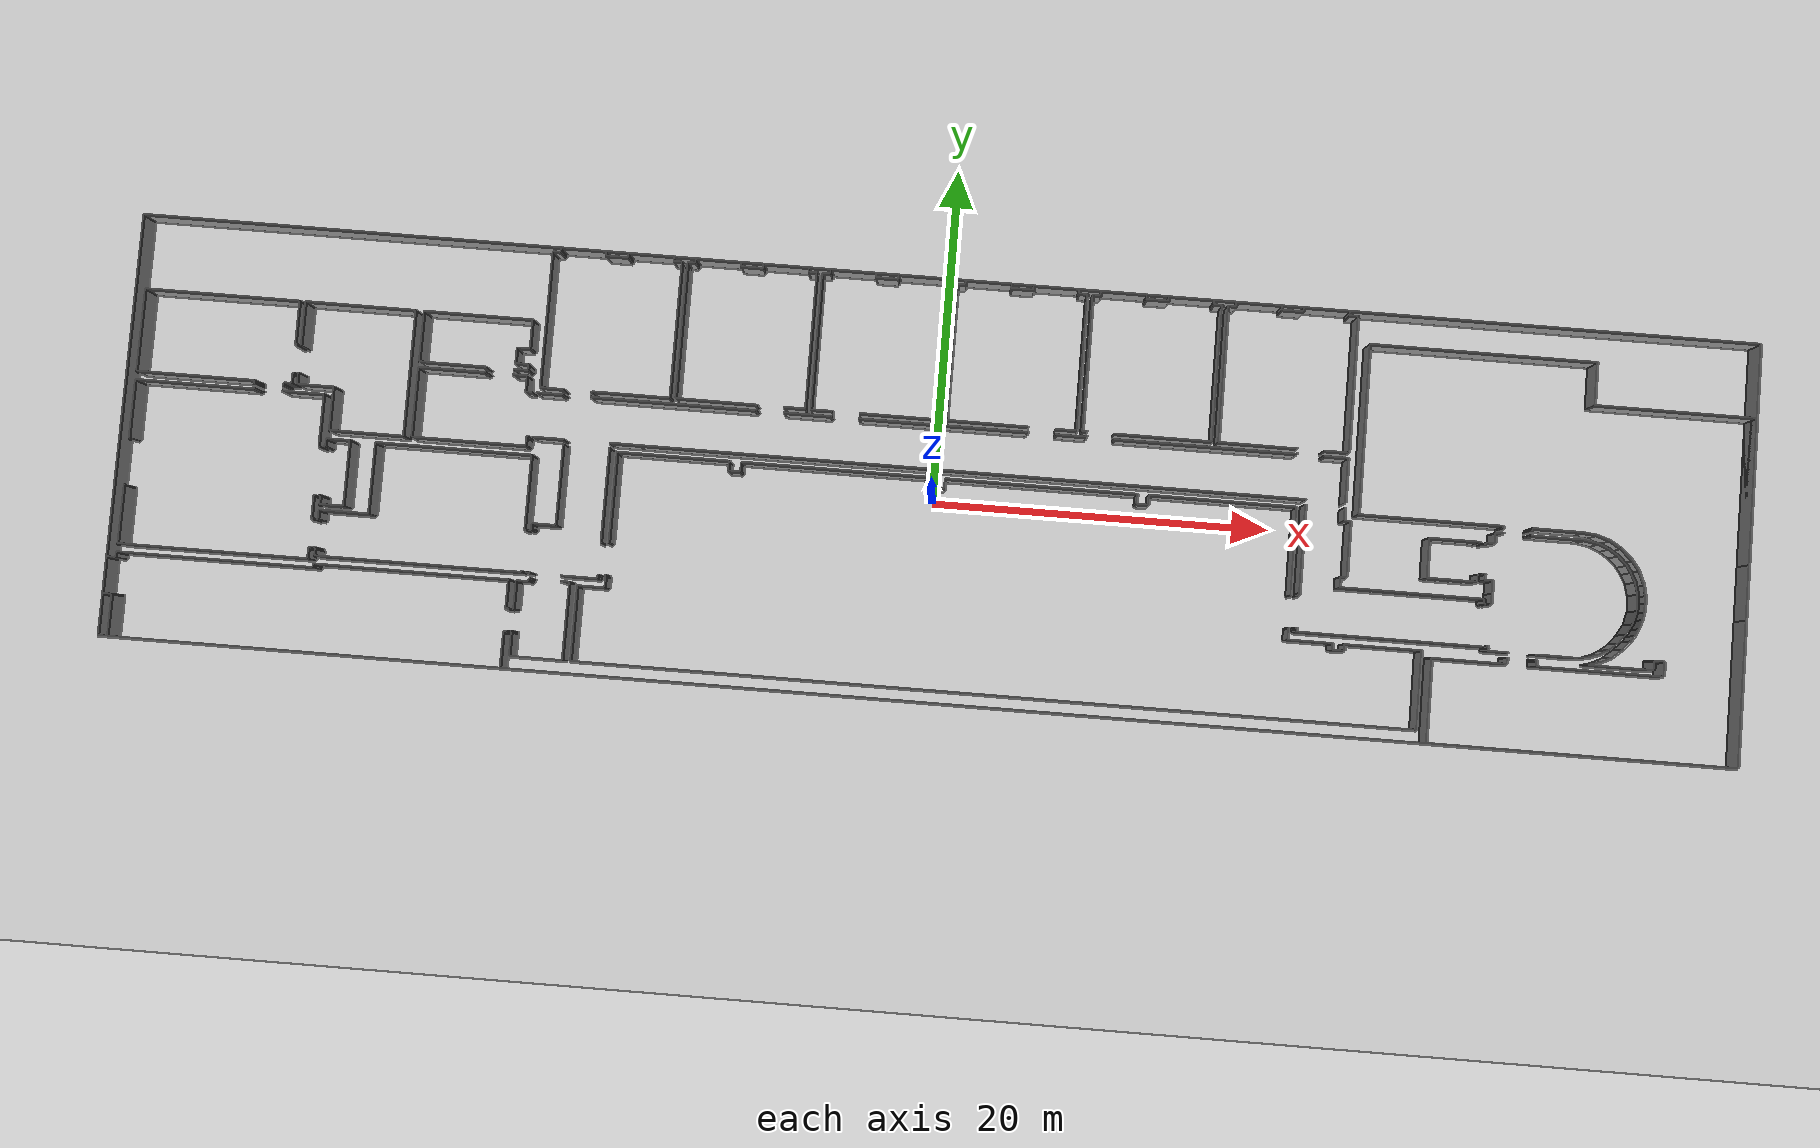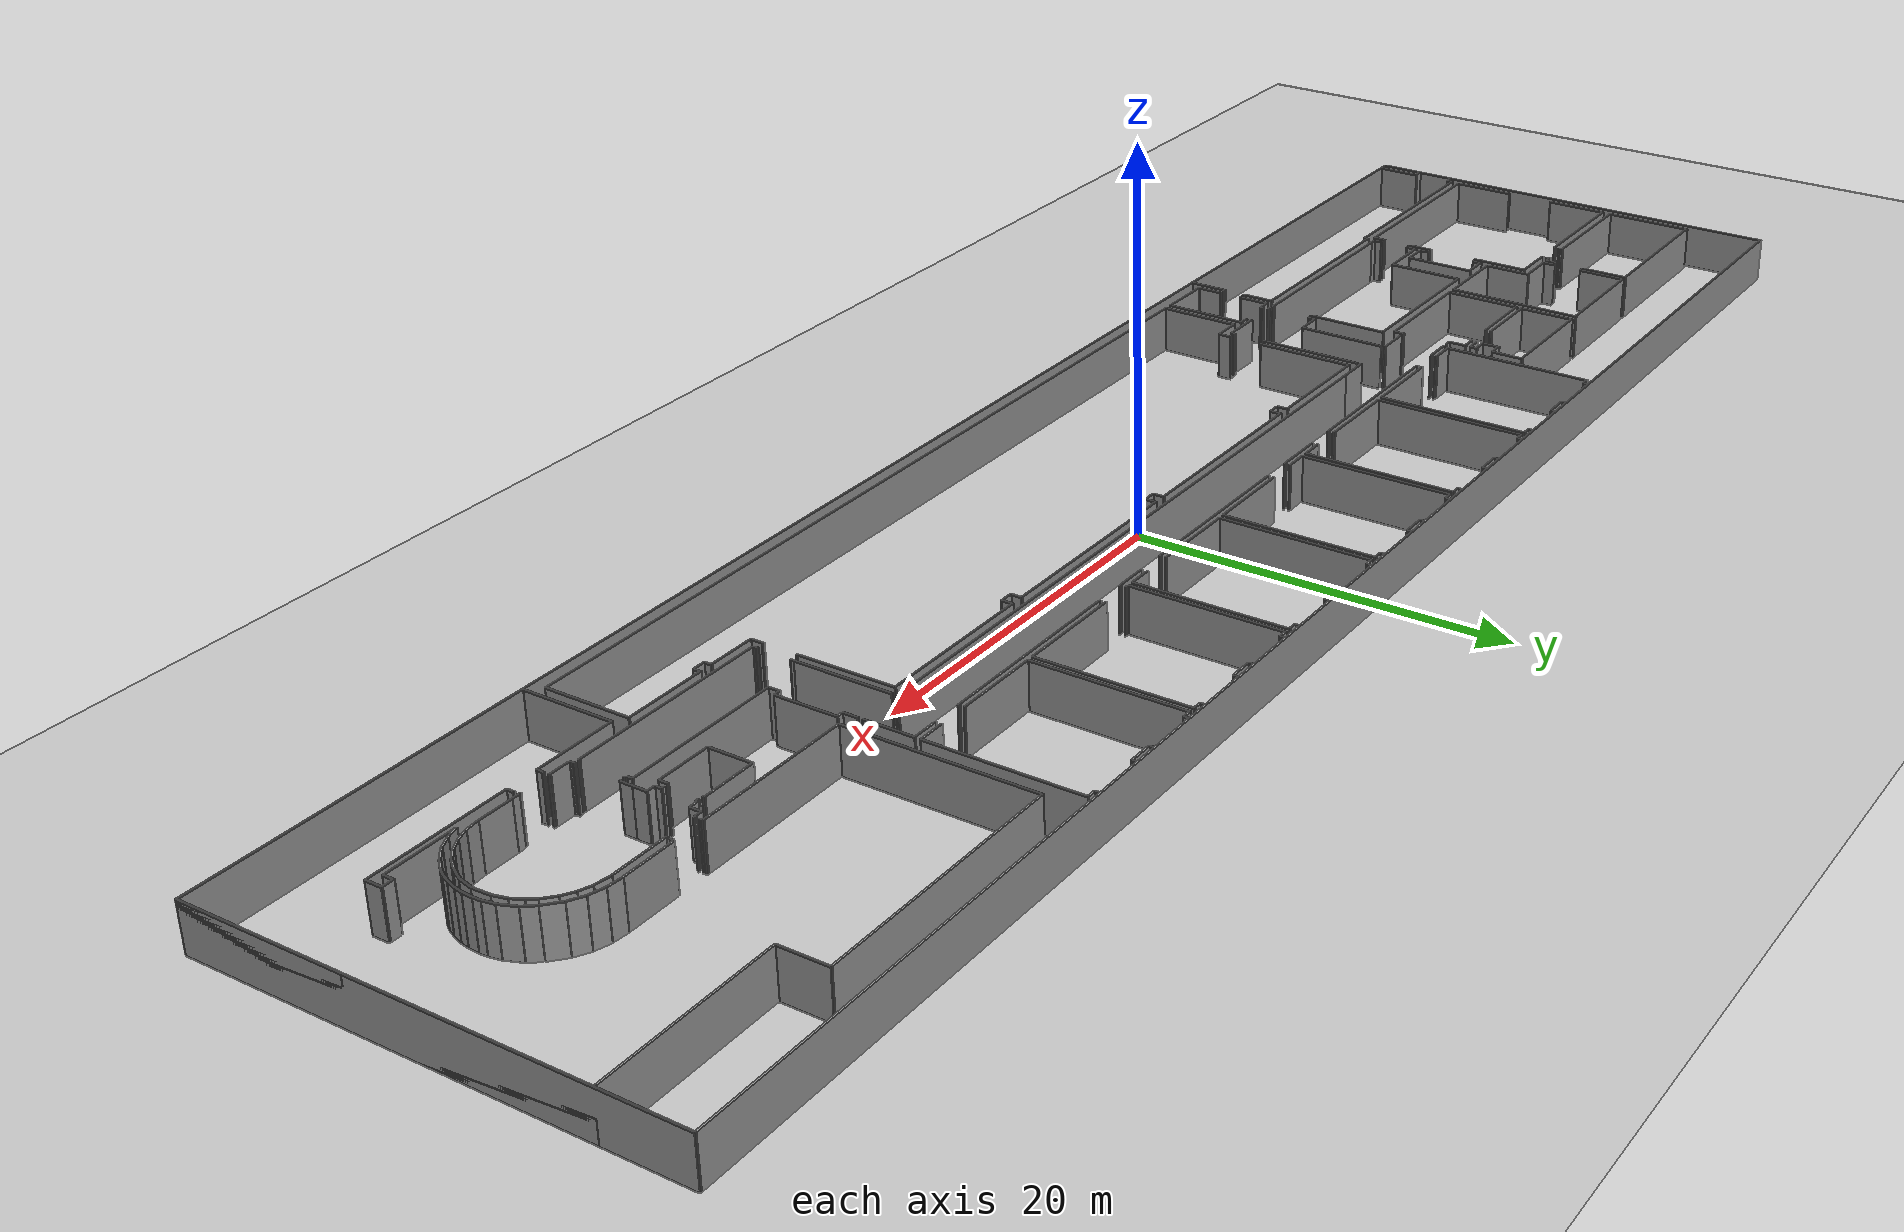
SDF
<sdf version="1.6">
  <world name="default">
    <light name="sun" type="directional">
      <cast_shadows>1</cast_shadows>
      <pose frame="">0 0 10 0 -0 0</pose>
      <diffuse>0.8 0.8 0.8 1</diffuse>
      <specular>0.1 0.1 0.1 1</specular>
      <attenuation>
        <range>1000</range>
        <constant>0.9</constant>
        <linear>0.01</linear>
        <quadratic>0.001</quadratic>
      </attenuation>
      <direction>-0.5 0.5 -1</direction>
    </light>
    <model name="ground_plane">
      <static>1</static>
      <link name="link">
        <collision name="collision">
          <geometry>
            <plane>
              <normal>0 0 1</normal>
              <size>100 100</size>
            </plane>
          </geometry>
          <surface>
            <friction>
              <ode>
                <mu>100</mu>
                <mu2>50</mu2>
              </ode>
              <torsional>
                <ode />
              </torsional>
            </friction>
            <contact>
              <ode />
            </contact>
            <bounce />
          </surface>
          <max_contacts>10</max_contacts>
        </collision>
        <visual name="visual">
          <cast_shadows>0</cast_shadows>
          <geometry>
            <plane>
              <normal>0 0 1</normal>
              <size>100 100</size>
            </plane>
          </geometry>
          <material>
            <script>
              <uri>file://media/materials/scripts/gazebo.material</uri>
              <name>Gazebo/Grey</name>
            </script>
          </material>
        </visual>
        <self_collide>0</self_collide>
        <kinematic>0</kinematic>
        <gravity>1</gravity>
      </link>
    </model>
    <gravity>0 0 -9.8</gravity>
    <magnetic_field>6e-06 2.3e-05 -4.2e-05</magnetic_field>
    <atmosphere type="adiabatic" />
    <physics default="0" name="default_physics" type="ode">
      <max_step_size>0.001</max_step_size>
      <real_time_factor>1</real_time_factor>
      <real_time_update_rate>1000</real_time_update_rate>
    </physics>
    <scene>
      <ambient>0.4 0.4 0.4 1</ambient>
      <background>0.7 0.7 0.7 1</background>
      <shadows>1</shadows>
    </scene>
    <spherical_coordinates>
      <surface_model>EARTH_WGS84</surface_model>
      <latitude_deg>0</latitude_deg>
      <longitude_deg>0</longitude_deg>
      <elevation>0</elevation>
      <heading_deg>0</heading_deg>
    </spherical_coordinates>
  <model name="0510032258_A_40_1_105">
		<static>1</static>
		<link name="Wall_0">
			<collision name="Wall_0_Collision">
				<geometry>
					<box>
						<size>4.90840024393 0.1 2.5</size>
					</box>
				</geometry>
				<pose frame="">2.45420012196 0 1.25 0 0 0</pose>
			</collision>
			<visual name="Wall_0_Visual">
				<pose frame="">2.45420012196 0 1.25 0 0 0</pose>
				<geometry>
					<box>
						<size>4.90840024393 0.1 2.5</size>
					</box>
				</geometry>
				<material>
					<script>
						<uri>file://media/materials/scripts/gazebo.material</uri>
						<name>Gazebo/Grey</name>
					</script>
					<ambient>1 1 1 1</ambient>
				</material>
			</visual>
			<pose frame="">0.576405122472 -9.3176389877 0 0 0 1.57079632679</pose>
		</link>
		<link name="Wall_1">
			<collision name="Wall_1_Collision">
				<geometry>
					<box>
						<size>9.15895924383 0.1 2.5</size>
					</box>
				</geometry>
				<pose frame="">4.57947962191 0 1.25 0 0 0</pose>
			</collision>
			<visual name="Wall_1_Visual">
				<pose frame="">4.57947962191 0 1.25 0 0 0</pose>
				<geometry>
					<box>
						<size>9.15895924383 0.1 2.5</size>
					</box>
				</geometry>
				<material>
					<script>
						<uri>file://media/materials/scripts/gazebo.material</uri>
						<name>Gazebo/Grey</name>
					</script>
					<ambient>1 1 1 1</ambient>
				</material>
			</visual>
			<pose frame="">0.576405122472 -4.40923874377 0 0 0 0.0</pose>
		</link>
		<link name="Wall_2">
			<collision name="Wall_2_Collision">
				<geometry>
					<box>
						<size>2.59388657384 0.1 2.5</size>
					</box>
				</geometry>
				<pose frame="">1.29694328692 0 1.25 0 0 0</pose>
			</collision>
			<visual name="Wall_2_Visual">
				<pose frame="">1.29694328692 0 1.25 0 0 0</pose>
				<geometry>
					<box>
						<size>2.59388657384 0.1 2.5</size>
					</box>
				</geometry>
				<material>
					<script>
						<uri>file://media/materials/scripts/gazebo.material</uri>
						<name>Gazebo/Grey</name>
					</script>
					<ambient>1 1 1 1</ambient>
				</material>
			</visual>
			<pose frame="">9.7353643663 -4.40923874377 0 0 0 -1.57079632679</pose>
		</link>
		<link name="Wall_3">
			<collision name="Wall_3_Collision">
				<geometry>
					<box>
						<size>0.0988413456652 0.1 2.5</size>
					</box>
				</geometry>
				<pose frame="">0.0494206728326 0 1.25 0 0 0</pose>
			</collision>
			<visual name="Wall_3_Visual">
				<pose frame="">0.0494206728326 0 1.25 0 0 0</pose>
				<geometry>
					<box>
						<size>0.0988413456652 0.1 2.5</size>
					</box>
				</geometry>
				<material>
					<script>
						<uri>file://media/materials/scripts/gazebo.material</uri>
						<name>Gazebo/Grey</name>
					</script>
					<ambient>1 1 1 1</ambient>
				</material>
			</visual>
			<pose frame="">9.7353643663 -7.00312531761 0 0 0 0.0</pose>
		</link>
		<link name="Wall_4">
			<collision name="Wall_4_Collision">
				<geometry>
					<box>
						<size>0.0973168004879 0.1 2.5</size>
					</box>
				</geometry>
				<pose frame="">0.0486584002439 0 1.25 0 0 0</pose>
			</collision>
			<visual name="Wall_4_Visual">
				<pose frame="">0.0486584002439 0 1.25 0 0 0</pose>
				<geometry>
					<box>
						<size>0.0973168004879 0.1 2.5</size>
					</box>
				</geometry>
				<material>
					<script>
						<uri>file://media/materials/scripts/gazebo.material</uri>
						<name>Gazebo/Grey</name>
					</script>
					<ambient>1 1 1 1</ambient>
				</material>
			</visual>
			<pose frame="">9.83420571196 -7.00312531761 0 0 0 -1.57079632679</pose>
		</link>
		<link name="Wall_5">
			<collision name="Wall_5_Collision">
				<geometry>
					<box>
						<size>0.0628874885659 0.1 2.5</size>
					</box>
				</geometry>
				<pose frame="">0.031443744283 0 1.25 0 0 0</pose>
			</collision>
			<visual name="Wall_5_Visual">
				<pose frame="">0.031443744283 0 1.25 0 0 0</pose>
				<geometry>
					<box>
						<size>0.0628874885659 0.1 2.5</size>
					</box>
				</geometry>
				<material>
					<script>
						<uri>file://media/materials/scripts/gazebo.material</uri>
						<name>Gazebo/Grey</name>
					</script>
					<ambient>1 1 1 1</ambient>
				</material>
			</visual>
			<pose frame="">9.83420571196 -8.65179388149 0 0 0 -1.57079632679</pose>
		</link>
		<link name="Wall_6">
			<collision name="Wall_6_Collision">
				<geometry>
					<box>
						<size>0.0802927126741 0.1 2.5</size>
					</box>
				</geometry>
				<pose frame="">0.040146356337 0 1.25 0 0 0</pose>
			</collision>
			<visual name="Wall_6_Visual">
				<pose frame="">0.040146356337 0 1.25 0 0 0</pose>
				<geometry>
					<box>
						<size>0.0802927126741 0.1 2.5</size>
					</box>
				</geometry>
				<material>
					<script>
						<uri>file://media/materials/scripts/gazebo.material</uri>
						<name>Gazebo/Grey</name>
					</script>
					<ambient>1 1 1 1</ambient>
				</material>
			</visual>
			<pose frame="">9.83420571196 -8.71468137006 0 0 0 3.14159265359</pose>
		</link>
		<link name="Wall_7">
			<collision name="Wall_7_Collision">
				<geometry>
					<box>
						<size>0.596859436935 0.1 2.5</size>
					</box>
				</geometry>
				<pose frame="">0.298429718467 0 1.25 0 0 0</pose>
			</collision>
			<visual name="Wall_7_Visual">
				<pose frame="">0.298429718467 0 1.25 0 0 0</pose>
				<geometry>
					<box>
						<size>0.596859436935 0.1 2.5</size>
					</box>
				</geometry>
				<material>
					<script>
						<uri>file://media/materials/scripts/gazebo.material</uri>
						<name>Gazebo/Grey</name>
					</script>
					<ambient>1 1 1 1</ambient>
				</material>
			</visual>
			<pose frame="">9.75391299929 -8.71468137006 0 0 0 -1.57079632679</pose>
		</link>
		<link name="Wall_8">
			<collision name="Wall_8_Collision">
				<geometry>
					<box>
						<size>0.457998780364 0.1 2.5</size>
					</box>
				</geometry>
				<pose frame="">0.228999390182 0 1.25 0 0 0</pose>
			</collision>
			<visual name="Wall_8_Visual">
				<pose frame="">0.228999390182 0 1.25 0 0 0</pose>
				<geometry>
					<box>
						<size>0.457998780364 0.1 2.5</size>
					</box>
				</geometry>
				<material>
					<script>
						<uri>file://media/materials/scripts/gazebo.material</uri>
						<name>Gazebo/Grey</name>
					</script>
					<ambient>1 1 1 1</ambient>
				</material>
			</visual>
			<pose frame="">9.75391299929 -9.31154080699 0 0 0 3.14159265359</pose>
		</link>
		<link name="Wall_9">
			<collision name="Wall_9_Collision">
				<geometry>
					<box>
						<size>0.192092692347 0.1 2.5</size>
					</box>
				</geometry>
				<pose frame="">0.0960463461734 0 1.25 0 0 0</pose>
			</collision>
			<visual name="Wall_9_Visual">
				<pose frame="">0.0960463461734 0 1.25 0 0 0</pose>
				<geometry>
					<box>
						<size>0.192092692347 0.1 2.5</size>
					</box>
				</geometry>
				<material>
					<script>
						<uri>file://media/materials/scripts/gazebo.material</uri>
						<name>Gazebo/Grey</name>
					</script>
					<ambient>1 1 1 1</ambient>
				</material>
			</visual>
			<pose frame="">9.29591421892 -9.31154080699 0 0 0 -1.57079632679</pose>
		</link>
		<link name="Wall_10">
			<collision name="Wall_10_Collision">
				<geometry>
					<box>
						<size>0.0879154385608 0.1 2.5</size>
					</box>
				</geometry>
				<pose frame="">0.0439577192804 0 1.25 0 0 0</pose>
			</collision>
			<visual name="Wall_10_Visual">
				<pose frame="">0.0439577192804 0 1.25 0 0 0</pose>
				<geometry>
					<box>
						<size>0.0879154385608 0.1 2.5</size>
					</box>
				</geometry>
				<material>
					<script>
						<uri>file://media/materials/scripts/gazebo.material</uri>
						<name>Gazebo/Grey</name>
					</script>
					<ambient>1 1 1 1</ambient>
				</material>
			</visual>
			<pose frame="">9.29591421892 -9.50363349934 0 0 0 3.14159265359</pose>
		</link>
		<link name="Wall_11">
			<collision name="Wall_11_Collision">
				<geometry>
					<box>
						<size>0.0600924890741 0.1 2.5</size>
					</box>
				</geometry>
				<pose frame="">0.030046244537 0 1.25 0 0 0</pose>
			</collision>
			<visual name="Wall_11_Visual">
				<pose frame="">0.030046244537 0 1.25 0 0 0</pose>
				<geometry>
					<box>
						<size>0.0600924890741 0.1 2.5</size>
					</box>
				</geometry>
				<material>
					<script>
						<uri>file://media/materials/scripts/gazebo.material</uri>
						<name>Gazebo/Grey</name>
					</script>
					<ambient>1 1 1 1</ambient>
				</material>
			</visual>
			<pose frame="">7.63314361216 -9.50363349934 0 0 0 3.14159265359</pose>
		</link>
		<link name="Wall_12">
			<collision name="Wall_12_Collision">
				<geometry>
					<box>
						<size>0.186375647932 0.1 2.5</size>
					</box>
				</geometry>
				<pose frame="">0.0931878239658 0 1.25 0 0 0</pose>
			</collision>
			<visual name="Wall_12_Visual">
				<pose frame="">0.0931878239658 0 1.25 0 0 0</pose>
				<geometry>
					<box>
						<size>0.186375647932 0.1 2.5</size>
					</box>
				</geometry>
				<material>
					<script>
						<uri>file://media/materials/scripts/gazebo.material</uri>
						<name>Gazebo/Grey</name>
					</script>
					<ambient>1 1 1 1</ambient>
				</material>
			</visual>
			<pose frame="">7.57305112308 -9.50363349934 0 0 0 1.57079632679</pose>
		</link>
		<link name="Wall_13">
			<collision name="Wall_13_Collision">
				<geometry>
					<box>
						<size>6.99664601099 0.1 2.5</size>
					</box>
				</geometry>
				<pose frame="">3.4983230055 0 1.25 0 0 0</pose>
			</collision>
			<visual name="Wall_13_Visual">
				<pose frame="">3.4983230055 0 1.25 0 0 0</pose>
				<geometry>
					<box>
						<size>6.99664601099 0.1 2.5</size>
					</box>
				</geometry>
				<material>
					<script>
						<uri>file://media/materials/scripts/gazebo.material</uri>
						<name>Gazebo/Grey</name>
					</script>
					<ambient>1 1 1 1</ambient>
				</material>
			</visual>
			<pose frame="">7.57305112308 -9.31725785141 0 0 0 -3.14153817945</pose>
		</link>
		<link name="Wall_14">
			<collision name="Wall_14_Collision">
				<geometry>
					<box>
						<size>3.4490293729 0.1 2.5</size>
					</box>
				</geometry>
				<pose frame="">1.72451468645 0 1.25 0 0 0</pose>
			</collision>
			<visual name="Wall_14_Visual">
				<pose frame="">1.72451468645 0 1.25 0 0 0</pose>
				<geometry>
					<box>
						<size>3.4490293729 0.1 2.5</size>
					</box>
				</geometry>
				<material>
					<script>
						<uri>file://media/materials/scripts/gazebo.material</uri>
						<name>Gazebo/Grey</name>
					</script>
					<ambient>1 1 1 1</ambient>
				</material>
			</visual>
			<pose frame="">0.575007622726 -19.5164650879 0 0 0 1.57079632679</pose>
		</link>
		<link name="Wall_15">
			<collision name="Wall_15_Collision">
				<geometry>
					<box>
						<size>0.0303638581157 0.1 2.5</size>
					</box>
				</geometry>
				<pose frame="">0.0151819290578 0 1.25 0 0 0</pose>
			</collision>
			<visual name="Wall_15_Visual">
				<pose frame="">0.0151819290578 0 1.25 0 0 0</pose>
				<geometry>
					<box>
						<size>0.0303638581157 0.1 2.5</size>
					</box>
				</geometry>
				<material>
					<script>
						<uri>file://media/materials/scripts/gazebo.material</uri>
						<name>Gazebo/Grey</name>
					</script>
					<ambient>1 1 1 1</ambient>
				</material>
			</visual>
			<pose frame="">0.575007622726 -16.067435715 0 0 0 3.14159265359</pose>
		</link>
		<link name="Wall_16">
			<collision name="Wall_16_Collision">
				<geometry>
					<box>
						<size>0.0204543144629 0.1 2.5</size>
					</box>
				</geometry>
				<pose frame="">0.0102271572314 0 1.25 0 0 0</pose>
			</collision>
			<visual name="Wall_16_Visual">
				<pose frame="">0.0102271572314 0 1.25 0 0 0</pose>
				<geometry>
					<box>
						<size>0.0204543144629 0.1 2.5</size>
					</box>
				</geometry>
				<material>
					<script>
						<uri>file://media/materials/scripts/gazebo.material</uri>
						<name>Gazebo/Grey</name>
					</script>
					<ambient>1 1 1 1</ambient>
				</material>
			</visual>
			<pose frame="">0.54464376461 -13.2870464478 0 0 0 0.0</pose>
		</link>
		<link name="Wall_17">
			<collision name="Wall_17_Collision">
				<geometry>
					<box>
						<size>3.47177050513 0.1 2.5</size>
					</box>
				</geometry>
				<pose frame="">1.73588525257 0 1.25 0 0 0</pose>
			</collision>
			<visual name="Wall_17_Visual">
				<pose frame="">1.73588525257 0 1.25 0 0 0</pose>
				<geometry>
					<box>
						<size>3.47177050513 0.1 2.5</size>
					</box>
				</geometry>
				<material>
					<script>
						<uri>file://media/materials/scripts/gazebo.material</uri>
						<name>Gazebo/Grey</name>
					</script>
					<ambient>1 1 1 1</ambient>
				</material>
			</visual>
			<pose frame="">0.565098079073 -13.2870464478 0 0 0 1.57079632679</pose>
		</link>
		<link name="Wall_18">
			<collision name="Wall_18_Collision">
				<geometry>
					<box>
						<size>6.9816546397 0.1 2.5</size>
					</box>
				</geometry>
				<pose frame="">3.49082731985 0 1.25 0 0 0</pose>
			</collision>
			<visual name="Wall_18_Visual">
				<pose frame="">3.49082731985 0 1.25 0 0 0</pose>
				<geometry>
					<box>
						<size>6.9816546397 0.1 2.5</size>
					</box>
				</geometry>
				<material>
					<script>
						<uri>file://media/materials/scripts/gazebo.material</uri>
						<name>Gazebo/Grey</name>
					</script>
					<ambient>1 1 1 1</ambient>
				</material>
			</visual>
			<pose frame="">0.565098079073 -9.81527594268 0 0 0 0.0</pose>
		</link>
		<link name="Wall_19">
			<collision name="Wall_19_Collision">
				<geometry>
					<box>
						<size>0.0364620388251 0.1 2.5</size>
					</box>
				</geometry>
				<pose frame="">0.0182310194125 0 1.25 0 0 0</pose>
			</collision>
			<visual name="Wall_19_Visual">
				<pose frame="">0.0182310194125 0 1.25 0 0 0</pose>
				<geometry>
					<box>
						<size>0.0364620388251 0.1 2.5</size>
					</box>
				</geometry>
				<material>
					<script>
						<uri>file://media/materials/scripts/gazebo.material</uri>
						<name>Gazebo/Grey</name>
					</script>
					<ambient>1 1 1 1</ambient>
				</material>
			</visual>
			<pose frame="">7.54675271877 -9.81527594268 0 0 0 1.57079632679</pose>
		</link>
		<link name="Wall_20">
			<collision name="Wall_20_Collision">
				<geometry>
					<box>
						<size>0.0999847545482 0.1 2.5</size>
					</box>
				</geometry>
				<pose frame="">0.0499923772741 0 1.25 0 0 0</pose>
			</collision>
			<visual name="Wall_20_Visual">
				<pose frame="">0.0499923772741 0 1.25 0 0 0</pose>
				<geometry>
					<box>
						<size>0.0999847545482 0.1 2.5</size>
					</box>
				</geometry>
				<material>
					<script>
						<uri>file://media/materials/scripts/gazebo.material</uri>
						<name>Gazebo/Grey</name>
					</script>
					<ambient>1 1 1 1</ambient>
				</material>
			</visual>
			<pose frame="">7.54675271877 -9.77881390385 0 0 0 0.0</pose>
		</link>
		<link name="Wall_21">
			<collision name="Wall_21_Collision">
				<geometry>
					<box>
						<size>0.0406545380628 0.1 2.5</size>
					</box>
				</geometry>
				<pose frame="">0.0203272690314 0 1.25 0 0 0</pose>
			</collision>
			<visual name="Wall_21_Visual">
				<pose frame="">0.0203272690314 0 1.25 0 0 0</pose>
				<geometry>
					<box>
						<size>0.0406545380628 0.1 2.5</size>
					</box>
				</geometry>
				<material>
					<script>
						<uri>file://media/materials/scripts/gazebo.material</uri>
						<name>Gazebo/Grey</name>
					</script>
					<ambient>1 1 1 1</ambient>
				</material>
			</visual>
			<pose frame="">9.22985059457 -9.77881390385 0 0 0 0.0</pose>
		</link>
		<link name="Wall_22">
			<collision name="Wall_22_Collision">
				<geometry>
					<box>
						<size>0.0249009045635 0.1 2.5</size>
					</box>
				</geometry>
				<pose frame="">0.0124504522817 0 1.25 0 0 0</pose>
			</collision>
			<visual name="Wall_22_Visual">
				<pose frame="">0.0124504522817 0 1.25 0 0 0</pose>
				<geometry>
					<box>
						<size>0.0249009045635 0.1 2.5</size>
					</box>
				</geometry>
				<material>
					<script>
						<uri>file://media/materials/scripts/gazebo.material</uri>
						<name>Gazebo/Grey</name>
					</script>
					<ambient>1 1 1 1</ambient>
				</material>
			</visual>
			<pose frame="">9.27050513264 -9.77881390385 0 0 0 -1.57079632679</pose>
		</link>
		<link name="Wall_23">
			<collision name="Wall_23_Collision">
				<geometry>
					<box>
						<size>2.44956296372 0.1 2.5</size>
					</box>
				</geometry>
				<pose frame="">1.22478148186 0 1.25 0 0 0</pose>
			</collision>
			<visual name="Wall_23_Visual">
				<pose frame="">1.22478148186 0 1.25 0 0 0</pose>
				<geometry>
					<box>
						<size>2.44956296372 0.1 2.5</size>
					</box>
				</geometry>
				<material>
					<script>
						<uri>file://media/materials/scripts/gazebo.material</uri>
						<name>Gazebo/Grey</name>
					</script>
					<ambient>1 1 1 1</ambient>
				</material>
			</visual>
			<pose frame="">9.27050513264 -9.80371480842 0 0 0 0.0</pose>
		</link>
		<link name="Wall_24">
			<collision name="Wall_24_Collision">
				<geometry>
					<box>
						<size>3.06154080699 0.1 2.5</size>
					</box>
				</geometry>
				<pose frame="">1.5307704035 0 1.25 0 0 0</pose>
			</collision>
			<visual name="Wall_24_Visual">
				<pose frame="">1.5307704035 0 1.25 0 0 0</pose>
				<geometry>
					<box>
						<size>3.06154080699 0.1 2.5</size>
					</box>
				</geometry>
				<material>
					<script>
						<uri>file://media/materials/scripts/gazebo.material</uri>
						<name>Gazebo/Grey</name>
					</script>
					<ambient>1 1 1 1</ambient>
				</material>
			</visual>
			<pose frame="">11.7200680964 -9.80371480842 0 0 0 -1.57079632679</pose>
		</link>
		<link name="Wall_25">
			<collision name="Wall_25_Collision">
				<geometry>
					<box>
						<size>0.029601585527 0.1 2.5</size>
					</box>
				</geometry>
				<pose frame="">0.0148007927635 0 1.25 0 0 0</pose>
			</collision>
			<visual name="Wall_25_Visual">
				<pose frame="">0.0148007927635 0 1.25 0 0 0</pose>
				<geometry>
					<box>
						<size>0.029601585527 0.1 2.5</size>
					</box>
				</geometry>
				<material>
					<script>
						<uri>file://media/materials/scripts/gazebo.material</uri>
						<name>Gazebo/Grey</name>
					</script>
					<ambient>1 1 1 1</ambient>
				</material>
			</visual>
			<pose frame="">11.7200680964 -12.8652556154 0 0 0 0.0</pose>
		</link>
		<link name="Wall_26">
			<collision name="Wall_26_Collision">
				<geometry>
					<box>
						<size>0.102144526883 0.1 2.5</size>
					</box>
				</geometry>
				<pose frame="">0.0510722634414 0 1.25 0 0 0</pose>
			</collision>
			<visual name="Wall_26_Visual">
				<pose frame="">0.0510722634414 0 1.25 0 0 0</pose>
				<geometry>
					<box>
						<size>0.102144526883 0.1 2.5</size>
					</box>
				</geometry>
				<material>
					<script>
						<uri>file://media/materials/scripts/gazebo.material</uri>
						<name>Gazebo/Grey</name>
					</script>
					<ambient>1 1 1 1</ambient>
				</material>
			</visual>
			<pose frame="">11.7496696819 -12.8652556154 0 0 0 -1.57079632679</pose>
		</link>
		<link name="Wall_27">
			<collision name="Wall_27_Collision">
				<geometry>
					<box>
						<size>0.0767354405936 0.1 2.5</size>
					</box>
				</geometry>
				<pose frame="">0.0383677202968 0 1.25 0 0 0</pose>
			</collision>
			<visual name="Wall_27_Visual">
				<pose frame="">0.0383677202968 0 1.25 0 0 0</pose>
				<geometry>
					<box>
						<size>0.0767354405936 0.1 2.5</size>
					</box>
				</geometry>
				<material>
					<script>
						<uri>file://media/materials/scripts/gazebo.material</uri>
						<name>Gazebo/Grey</name>
					</script>
					<ambient>1 1 1 1</ambient>
				</material>
			</visual>
			<pose frame="">11.7496696819 -15.7446132737 0 0 0 -1.57079632679</pose>
		</link>
		<link name="Wall_28">
			<collision name="Wall_28_Collision">
				<geometry>
					<box>
						<size>0.022487041366 0.1 2.5</size>
					</box>
				</geometry>
				<pose frame="">0.011243520683 0 1.25 0 0 0</pose>
			</collision>
			<visual name="Wall_28_Visual">
				<pose frame="">0.011243520683 0 1.25 0 0 0</pose>
				<geometry>
					<box>
						<size>0.022487041366 0.1 2.5</size>
					</box>
				</geometry>
				<material>
					<script>
						<uri>file://media/materials/scripts/gazebo.material</uri>
						<name>Gazebo/Grey</name>
					</script>
					<ambient>1 1 1 1</ambient>
				</material>
			</visual>
			<pose frame="">11.7496696819 -15.8213487143 0 0 0 3.14159265359</pose>
		</link>
		<link name="Wall_29">
			<collision name="Wall_29_Collision">
				<geometry>
					<box>
						<size>1.3352474845 0.1 2.5</size>
					</box>
				</geometry>
				<pose frame="">0.66762374225 0 1.25 0 0 0</pose>
			</collision>
			<visual name="Wall_29_Visual">
				<pose frame="">0.66762374225 0 1.25 0 0 0</pose>
				<geometry>
					<box>
						<size>1.3352474845 0.1 2.5</size>
					</box>
				</geometry>
				<material>
					<script>
						<uri>file://media/materials/scripts/gazebo.material</uri>
						<name>Gazebo/Grey</name>
					</script>
					<ambient>1 1 1 1</ambient>
				</material>
			</visual>
			<pose frame="">11.7271826405 -15.8213487143 0 0 0 -1.57079632679</pose>
		</link>
		<link name="Wall_30">
			<collision name="Wall_30_Collision">
				<geometry>
					<box>
						<size>0.0898211200325 0.1 2.5</size>
					</box>
				</geometry>
				<pose frame="">0.0449105600163 0 1.25 0 0 0</pose>
			</collision>
			<visual name="Wall_30_Visual">
				<pose frame="">0.0449105600163 0 1.25 0 0 0</pose>
				<geometry>
					<box>
						<size>0.0898211200325 0.1 2.5</size>
					</box>
				</geometry>
				<material>
					<script>
						<uri>file://media/materials/scripts/gazebo.material</uri>
						<name>Gazebo/Grey</name>
					</script>
					<ambient>1 1 1 1</ambient>
				</material>
			</visual>
			<pose frame="">11.7271826405 -17.1565961988 0 0 0 0.0</pose>
		</link>
		<link name="Wall_31">
			<collision name="Wall_31_Collision">
				<geometry>
					<box>
						<size>0.103923162923 0.1 2.5</size>
					</box>
				</geometry>
				<pose frame="">0.0519615814615 0 1.25 0 0 0</pose>
			</collision>
			<visual name="Wall_31_Visual">
				<pose frame="">0.0519615814615 0 1.25 0 0 0</pose>
				<geometry>
					<box>
						<size>0.103923162923 0.1 2.5</size>
					</box>
				</geometry>
				<material>
					<script>
						<uri>file://media/materials/scripts/gazebo.material</uri>
						<name>Gazebo/Grey</name>
					</script>
					<ambient>1 1 1 1</ambient>
				</material>
			</visual>
			<pose frame="">11.8170037605 -17.1565961988 0 0 0 -1.57079632679</pose>
		</link>
		<link name="Wall_32">
			<collision name="Wall_32_Collision">
				<geometry>
					<box>
						<size>0.0327777213131 0.1 2.5</size>
					</box>
				</geometry>
				<pose frame="">0.0163888606566 0 1.25 0 0 0</pose>
			</collision>
			<visual name="Wall_32_Visual">
				<pose frame="">0.0163888606566 0 1.25 0 0 0</pose>
				<geometry>
					<box>
						<size>0.0327777213131 0.1 2.5</size>
					</box>
				</geometry>
				<material>
					<script>
						<uri>file://media/materials/scripts/gazebo.material</uri>
						<name>Gazebo/Grey</name>
					</script>
					<ambient>1 1 1 1</ambient>
				</material>
			</visual>
			<pose frame="">11.8170037605 -18.8094572619 0 0 0 -1.57079632679</pose>
		</link>
		<link name="Wall_33">
			<collision name="Wall_33_Collision">
				<geometry>
					<box>
						<size>0.0233763593861 0.1 2.5</size>
					</box>
				</geometry>
				<pose frame="">0.0116881796931 0 1.25 0 0 0</pose>
			</collision>
			<visual name="Wall_33_Visual">
				<pose frame="">0.0116881796931 0 1.25 0 0 0</pose>
				<geometry>
					<box>
						<size>0.0233763593861 0.1 2.5</size>
					</box>
				</geometry>
				<material>
					<script>
						<uri>file://media/materials/scripts/gazebo.material</uri>
						<name>Gazebo/Grey</name>
					</script>
					<ambient>1 1 1 1</ambient>
				</material>
			</visual>
			<pose frame="">11.8170037605 -18.8422349832 0 0 0 -1.57079632679</pose>
		</link>
		<link name="Wall_34">
			<collision name="Wall_34_Collision">
				<geometry>
					<box>
						<size>0.087407256835 0.1 2.5</size>
					</box>
				</geometry>
				<pose frame="">0.0437036284175 0 1.25 0 0 0</pose>
			</collision>
			<visual name="Wall_34_Visual">
				<pose frame="">0.0437036284175 0 1.25 0 0 0</pose>
				<geometry>
					<box>
						<size>0.087407256835 0.1 2.5</size>
					</box>
				</geometry>
				<material>
					<script>
						<uri>file://media/materials/scripts/gazebo.material</uri>
						<name>Gazebo/Grey</name>
					</script>
					<ambient>1 1 1 1</ambient>
				</material>
			</visual>
			<pose frame="">11.8170037605 -18.8656113426 0 0 0 3.14159265359</pose>
		</link>
		<link name="Wall_35">
			<collision name="Wall_35_Collision">
				<geometry>
					<box>
						<size>0.642468746824 0.1 2.5</size>
					</box>
				</geometry>
				<pose frame="">0.321234373412 0 1.25 0 0 0</pose>
			</collision>
			<visual name="Wall_35_Visual">
				<pose frame="">0.321234373412 0 1.25 0 0 0</pose>
				<geometry>
					<box>
						<size>0.642468746824 0.1 2.5</size>
					</box>
				</geometry>
				<material>
					<script>
						<uri>file://media/materials/scripts/gazebo.material</uri>
						<name>Gazebo/Grey</name>
					</script>
					<ambient>1 1 1 1</ambient>
				</material>
			</visual>
			<pose frame="">11.7295965037 -18.8656113426 0 0 0 -1.57079632679</pose>
		</link>
		<link name="Wall_36">
			<collision name="Wall_36_Collision">
				<geometry>
					<box>
						<size>11.1545920325 0.1 2.5</size>
					</box>
				</geometry>
				<pose frame="">5.57729601626 0 1.25 0 0 0</pose>
			</collision>
			<visual name="Wall_36_Visual">
				<pose frame="">5.57729601626 0 1.25 0 0 0</pose>
				<geometry>
					<box>
						<size>11.1545920325 0.1 2.5</size>
					</box>
				</geometry>
				<material>
					<script>
						<uri>file://media/materials/scripts/gazebo.material</uri>
						<name>Gazebo/Grey</name>
					</script>
					<ambient>1 1 1 1</ambient>
				</material>
			</visual>
			<pose frame="">11.7295965037 -19.5080800894 0 0 0 -3.1408409453</pose>
		</link>
		<link name="Wall_37">
			<collision name="Wall_37_Collision">
				<geometry>
					<box>
						<size>0.700528508995 0.1 2.5</size>
					</box>
				</geometry>
				<pose frame="">0.350264254497 0 1.25 0 0 0</pose>
			</collision>
			<visual name="Wall_37_Visual">
				<pose frame="">0.350264254497 0 1.25 0 0 0</pose>
				<geometry>
					<box>
						<size>0.700528508995 0.1 2.5</size>
					</box>
				</geometry>
				<material>
					<script>
						<uri>file://media/materials/scripts/gazebo.material</uri>
						<name>Gazebo/Grey</name>
					</script>
					<ambient>1 1 1 1</ambient>
				</material>
			</visual>
			<pose frame="">10.0820713487 -9.33008943998 0 0 0 1.57079632679</pose>
		</link>
		<link name="Wall_38">
			<collision name="Wall_38_Collision">
				<geometry>
					<box>
						<size>2.65664701697 0.1 2.5</size>
					</box>
				</geometry>
				<pose frame="">1.32832350849 0 1.25 0 0 0</pose>
			</collision>
			<visual name="Wall_38_Visual">
				<pose frame="">1.32832350849 0 1.25 0 0 0</pose>
				<geometry>
					<box>
						<size>2.65664701697 0.1 2.5</size>
					</box>
				</geometry>
				<material>
					<script>
						<uri>file://media/materials/scripts/gazebo.material</uri>
						<name>Gazebo/Grey</name>
					</script>
					<ambient>1 1 1 1</ambient>
				</material>
			</visual>
			<pose frame="">10.0820713487 -7.064488261 0 0 0 1.57079632679</pose>
		</link>
		<link name="Wall_39">
			<collision name="Wall_39_Collision">
				<geometry>
					<box>
						<size>6.52695904055 0.1 2.5</size>
					</box>
				</geometry>
				<pose frame="">3.26347952028 0 1.25 0 0 0</pose>
			</collision>
			<visual name="Wall_39_Visual">
				<pose frame="">3.26347952028 0 1.25 0 0 0</pose>
				<geometry>
					<box>
						<size>6.52695904055 0.1 2.5</size>
					</box>
				</geometry>
				<material>
					<script>
						<uri>file://media/materials/scripts/gazebo.material</uri>
						<name>Gazebo/Grey</name>
					</script>
					<ambient>1 1 1 1</ambient>
				</material>
			</visual>
			<pose frame="">10.0820713487 -4.40784124403 0 0 0 0.0</pose>
		</link>
		<link name="Wall_40">
			<collision name="Wall_40_Collision">
				<geometry>
					<box>
						<size>7.47852932209 0.1 2.5</size>
					</box>
				</geometry>
				<pose frame="">3.73926466104 0 1.25 0 0 0</pose>
			</collision>
			<visual name="Wall_40_Visual">
				<pose frame="">3.73926466104 0 1.25 0 0 0</pose>
				<geometry>
					<box>
						<size>7.47852932209 0.1 2.5</size>
					</box>
				</geometry>
				<material>
					<script>
						<uri>file://media/materials/scripts/gazebo.material</uri>
						<name>Gazebo/Grey</name>
					</script>
					<ambient>1 1 1 1</ambient>
				</material>
			</visual>
			<pose frame="">16.6090303893 -4.40784124403 0 0 0 -1.57079632679</pose>
		</link>
		<link name="Wall_41">
			<collision name="Wall_41_Collision">
				<geometry>
					<box>
						<size>4.37264965952 0.1 2.5</size>
					</box>
				</geometry>
				<pose frame="">2.18632482976 0 1.25 0 0 0</pose>
			</collision>
			<visual name="Wall_41_Visual">
				<pose frame="">2.18632482976 0 1.25 0 0 0</pose>
				<geometry>
					<box>
						<size>4.37264965952 0.1 2.5</size>
					</box>
				</geometry>
				<material>
					<script>
						<uri>file://media/materials/scripts/gazebo.material</uri>
						<name>Gazebo/Grey</name>
					</script>
					<ambient>1 1 1 1</ambient>
				</material>
			</visual>
			<pose frame="">16.6090303893 -11.8863705661 0 0 0 3.14159265359</pose>
		</link>
		<link name="Wall_42">
			<collision name="Wall_42_Collision">
				<geometry>
					<box>
						<size>2.56250635227 0.1 2.5</size>
					</box>
				</geometry>
				<pose frame="">1.28125317614 0 1.25 0 0 0</pose>
			</collision>
			<visual name="Wall_42_Visual">
				<pose frame="">1.28125317614 0 1.25 0 0 0</pose>
				<geometry>
					<box>
						<size>2.56250635227 0.1 2.5</size>
					</box>
				</geometry>
				<material>
					<script>
						<uri>file://media/materials/scripts/gazebo.material</uri>
						<name>Gazebo/Grey</name>
					</script>
					<ambient>1 1 1 1</ambient>
				</material>
			</visual>
			<pose frame="">12.2363807297 -11.8863705661 0 0 0 1.57079632679</pose>
		</link>
		<link name="Wall_43">
			<collision name="Wall_43_Collision">
				<geometry>
					<box>
						<size>2.15431837542 0.1 2.5</size>
					</box>
				</geometry>
				<pose frame="">1.07715918771 0 1.25 0 0 0</pose>
			</collision>
			<visual name="Wall_43_Visual">
				<pose frame="">1.07715918771 0 1.25 0 0 0</pose>
				<geometry>
					<box>
						<size>2.15431837542 0.1 2.5</size>
					</box>
				</geometry>
				<material>
					<script>
						<uri>file://media/materials/scripts/gazebo.material</uri>
						<name>Gazebo/Grey</name>
					</script>
					<ambient>1 1 1 1</ambient>
				</material>
			</visual>
			<pose frame="">12.2363807297 -9.32386421384 0 0 0 -3.13870299955</pose>
		</link>
		<link name="Wall_44">
			<collision name="Wall_44_Collision">
				<geometry>
					<box>
						<size>0.490395365383 0.1 2.5</size>
					</box>
				</geometry>
				<pose frame="">0.245197682691 0 1.25 0 0 0</pose>
			</collision>
			<visual name="Wall_44_Visual">
				<pose frame="">0.245197682691 0 1.25 0 0 0</pose>
				<geometry>
					<box>
						<size>0.490395365383 0.1 2.5</size>
					</box>
				</geometry>
				<material>
					<script>
						<uri>file://media/materials/scripts/gazebo.material</uri>
						<name>Gazebo/Grey</name>
					</script>
					<ambient>1 1 1 1</ambient>
				</material>
			</visual>
			<pose frame="">12.1258512044 -16.2771877223 0 0 0 1.57079632679</pose>
		</link>
		<link name="Wall_45">
			<collision name="Wall_45_Collision">
				<geometry>
					<box>
						<size>0.109004980181 0.1 2.5</size>
					</box>
				</geometry>
				<pose frame="">0.0545024900905 0 1.25 0 0 0</pose>
			</collision>
			<visual name="Wall_45_Visual">
				<pose frame="">0.0545024900905 0 1.25 0 0 0</pose>
				<geometry>
					<box>
						<size>0.109004980181 0.1 2.5</size>
					</box>
				</geometry>
				<material>
					<script>
						<uri>file://media/materials/scripts/gazebo.material</uri>
						<name>Gazebo/Grey</name>
					</script>
					<ambient>1 1 1 1</ambient>
				</material>
			</visual>
			<pose frame="">12.1258512044 -15.7867923569 0 0 0 3.14159265359</pose>
		</link>
		<link name="Wall_46">
			<collision name="Wall_46_Collision">
				<geometry>
					<box>
						<size>0.08169021242 0.1 2.5</size>
					</box>
				</geometry>
				<pose frame="">0.04084510621 0 1.25 0 0 0</pose>
			</collision>
			<visual name="Wall_46_Visual">
				<pose frame="">0.04084510621 0 1.25 0 0 0</pose>
				<geometry>
					<box>
						<size>0.08169021242 0.1 2.5</size>
					</box>
				</geometry>
				<material>
					<script>
						<uri>file://media/materials/scripts/gazebo.material</uri>
						<name>Gazebo/Grey</name>
					</script>
					<ambient>1 1 1 1</ambient>
				</material>
			</visual>
			<pose frame="">12.0168462242 -15.7867923569 0 0 0 1.57079632679</pose>
		</link>
		<link name="Wall_47">
			<collision name="Wall_47_Collision">
				<geometry>
					<box>
						<size>0.0664447606464 0.1 2.5</size>
					</box>
				</geometry>
				<pose frame="">0.0332223803232 0 1.25 0 0 0</pose>
			</collision>
			<visual name="Wall_47_Visual">
				<pose frame="">0.0332223803232 0 1.25 0 0 0</pose>
				<geometry>
					<box>
						<size>0.0664447606464 0.1 2.5</size>
					</box>
				</geometry>
				<material>
					<script>
						<uri>file://media/materials/scripts/gazebo.material</uri>
						<name>Gazebo/Grey</name>
					</script>
					<ambient>1 1 1 1</ambient>
				</material>
			</visual>
			<pose frame="">12.0168462242 -12.9365281024 0 0 0 1.57079632679</pose>
		</link>
		<link name="Wall_48">
			<collision name="Wall_48_Collision">
				<geometry>
					<box>
						<size>0.0985872548023 0.1 2.5</size>
					</box>
				</geometry>
				<pose frame="">0.0492936274012 0 1.25 0 0 0</pose>
			</collision>
			<visual name="Wall_48_Visual">
				<pose frame="">0.0492936274012 0 1.25 0 0 0</pose>
				<geometry>
					<box>
						<size>0.0985872548023 0.1 2.5</size>
					</box>
				</geometry>
				<material>
					<script>
						<uri>file://media/materials/scripts/gazebo.material</uri>
						<name>Gazebo/Grey</name>
					</script>
					<ambient>1 1 1 1</ambient>
				</material>
			</visual>
			<pose frame="">12.0168462242 -12.8700833418 0 0 0 0.0</pose>
		</link>
		<link name="Wall_49">
			<collision name="Wall_49_Collision">
				<geometry>
					<box>
						<size>0.478071958532 0.1 2.5</size>
					</box>
				</geometry>
				<pose frame="">0.239035979266 0 1.25 0 0 0</pose>
			</collision>
			<visual name="Wall_49_Visual">
				<pose frame="">0.239035979266 0 1.25 0 0 0</pose>
				<geometry>
					<box>
						<size>0.478071958532 0.1 2.5</size>
					</box>
				</geometry>
				<material>
					<script>
						<uri>file://media/materials/scripts/gazebo.material</uri>
						<name>Gazebo/Grey</name>
					</script>
					<ambient>1 1 1 1</ambient>
				</material>
			</visual>
			<pose frame="">12.115433479 -12.8700833418 0 0 0 1.57079632679</pose>
		</link>
		<link name="Wall_50">
			<collision name="Wall_50_Collision">
				<geometry>
					<box>
						<size>1.39597520073 0.1 2.5</size>
					</box>
				</geometry>
				<pose frame="">0.697987600366 0 1.25 0 0 0</pose>
			</collision>
			<visual name="Wall_50_Visual">
				<pose frame="">0.697987600366 0 1.25 0 0 0</pose>
				<geometry>
					<box>
						<size>1.39597520073 0.1 2.5</size>
					</box>
				</geometry>
				<material>
					<script>
						<uri>file://media/materials/scripts/gazebo.material</uri>
						<name>Gazebo/Grey</name>
					</script>
					<ambient>1 1 1 1</ambient>
				</material>
			</visual>
			<pose frame="">12.115433479 -12.3920113833 0 0 0 0.0</pose>
		</link>
		<link name="Wall_51">
			<collision name="Wall_51_Collision">
				<geometry>
					<box>
						<size>3.87831588576 0.1 2.5</size>
					</box>
				</geometry>
				<pose frame="">1.93915794288 0 1.25 0 0 0</pose>
			</collision>
			<visual name="Wall_51_Visual">
				<pose frame="">1.93915794288 0 1.25 0 0 0</pose>
				<geometry>
					<box>
						<size>3.87831588576 0.1 2.5</size>
					</box>
				</geometry>
				<material>
					<script>
						<uri>file://media/materials/scripts/gazebo.material</uri>
						<name>Gazebo/Grey</name>
					</script>
					<ambient>1 1 1 1</ambient>
				</material>
			</visual>
			<pose frame="">13.5114086797 -12.3920113833 0 0 0 -1.57079632679</pose>
		</link>
		<link name="Wall_52">
			<collision name="Wall_52_Collision">
				<geometry>
					<box>
						<size>1.38557445968 0.1 2.5</size>
					</box>
				</geometry>
				<pose frame="">0.692787229842 0 1.25 0 0 0</pose>
			</collision>
			<visual name="Wall_52_Visual">
				<pose frame="">0.692787229842 0 1.25 0 0 0</pose>
				<geometry>
					<box>
						<size>1.38557445968 0.1 2.5</size>
					</box>
				</geometry>
				<material>
					<script>
						<uri>file://media/materials/scripts/gazebo.material</uri>
						<name>Gazebo/Grey</name>
					</script>
					<ambient>1 1 1 1</ambient>
				</material>
			</visual>
			<pose frame="">13.5114086797 -16.270327269 0 0 0 -3.13664129116</pose>
		</link>
		<link name="Wall_53">
			<collision name="Wall_53_Collision">
				<geometry>
					<box>
						<size>0.511103770708 0.1 2.5</size>
					</box>
				</geometry>
				<pose frame="">0.255551885354 0 1.25 0 0 0</pose>
			</collision>
			<visual name="Wall_53_Visual">
				<pose frame="">0.255551885354 0 1.25 0 0 0</pose>
				<geometry>
					<box>
						<size>0.511103770708 0.1 2.5</size>
					</box>
				</geometry>
				<material>
					<script>
						<uri>file://media/materials/scripts/gazebo.material</uri>
						<name>Gazebo/Grey</name>
					</script>
					<ambient>1 1 1 1</ambient>
				</material>
			</visual>
			<pose frame="">12.6401311109 -19.3011230816 0 0 0 3.14159265359</pose>
		</link>
		<link name="Wall_54">
			<collision name="Wall_54_Collision">
				<geometry>
					<box>
						<size>0.409213334688 0.1 2.5</size>
					</box>
				</geometry>
				<pose frame="">0.204606667344 0 1.25 0 0 0</pose>
			</collision>
			<visual name="Wall_54_Visual">
				<pose frame="">0.204606667344 0 1.25 0 0 0</pose>
				<geometry>
					<box>
						<size>0.409213334688 0.1 2.5</size>
					</box>
				</geometry>
				<material>
					<script>
						<uri>file://media/materials/scripts/gazebo.material</uri>
						<name>Gazebo/Grey</name>
					</script>
					<ambient>1 1 1 1</ambient>
				</material>
			</visual>
			<pose frame="">12.1290273402 -19.3011230816 0 0 0 1.57079632679</pose>
		</link>
		<link name="Wall_55">
			<collision name="Wall_55_Collision">
				<geometry>
					<box>
						<size>0.0421790832402 0.1 2.5</size>
					</box>
				</geometry>
				<pose frame="">0.0210895416201 0 1.25 0 0 0</pose>
			</collision>
			<visual name="Wall_55_Visual">
				<pose frame="">0.0210895416201 0 1.25 0 0 0</pose>
				<geometry>
					<box>
						<size>0.0421790832402 0.1 2.5</size>
					</box>
				</geometry>
				<material>
					<script>
						<uri>file://media/materials/scripts/gazebo.material</uri>
						<name>Gazebo/Grey</name>
					</script>
					<ambient>1 1 1 1</ambient>
				</material>
			</visual>
			<pose frame="">12.1290273402 -18.8919097469 0 0 0 3.14159265359</pose>
		</link>
		<link name="Wall_56">
			<collision name="Wall_56_Collision">
				<geometry>
					<box>
						<size>0.104431344649 0.1 2.5</size>
					</box>
				</geometry>
				<pose frame="">0.0522156723244 0 1.25 0 0 0</pose>
			</collision>
			<visual name="Wall_56_Visual">
				<pose frame="">0.0522156723244 0 1.25 0 0 0</pose>
				<geometry>
					<box>
						<size>0.104431344649 0.1 2.5</size>
					</box>
				</geometry>
				<material>
					<script>
						<uri>file://media/materials/scripts/gazebo.material</uri>
						<name>Gazebo/Grey</name>
					</script>
					<ambient>1 1 1 1</ambient>
				</material>
			</visual>
			<pose frame="">12.0868482569 -18.8919097469 0 0 0 1.57079632679</pose>
		</link>
		<link name="Wall_57">
			<collision name="Wall_57_Collision">
				<geometry>
					<box>
						<size>0.0764813497307 0.1 2.5</size>
					</box>
				</geometry>
				<pose frame="">0.0382406748653 0 1.25 0 0 0</pose>
			</collision>
			<visual name="Wall_57_Visual">
				<pose frame="">0.0382406748653 0 1.25 0 0 0</pose>
				<geometry>
					<box>
						<size>0.0764813497307 0.1 2.5</size>
					</box>
				</geometry>
				<material>
					<script>
						<uri>file://media/materials/scripts/gazebo.material</uri>
						<name>Gazebo/Grey</name>
					</script>
					<ambient>1 1 1 1</ambient>
				</material>
			</visual>
			<pose frame="">12.0868482569 -17.222913914 0 0 0 1.57079632679</pose>
		</link>
		<link name="Wall_58">
			<collision name="Wall_58_Collision">
				<geometry>
					<box>
						<size>0.0274418131924 0.1 2.5</size>
					</box>
				</geometry>
				<pose frame="">0.0137209065962 0 1.25 0 0 0</pose>
			</collision>
			<visual name="Wall_58_Visual">
				<pose frame="">0.0137209065962 0 1.25 0 0 0</pose>
				<geometry>
					<box>
						<size>0.0274418131924 0.1 2.5</size>
					</box>
				</geometry>
				<material>
					<script>
						<uri>file://media/materials/scripts/gazebo.material</uri>
						<name>Gazebo/Grey</name>
					</script>
					<ambient>1 1 1 1</ambient>
				</material>
			</visual>
			<pose frame="">12.0868482569 -17.1464325643 0 0 0 0.0</pose>
		</link>
		<link name="Wall_59">
			<collision name="Wall_59_Collision">
				<geometry>
					<box>
						<size>0.54286512857 0.1 2.5</size>
					</box>
				</geometry>
				<pose frame="">0.271432564285 0 1.25 0 0 0</pose>
			</collision>
			<visual name="Wall_59_Visual">
				<pose frame="">0.271432564285 0 1.25 0 0 0</pose>
				<geometry>
					<box>
						<size>0.54286512857 0.1 2.5</size>
					</box>
				</geometry>
				<material>
					<script>
						<uri>file://media/materials/scripts/gazebo.material</uri>
						<name>Gazebo/Grey</name>
					</script>
					<ambient>1 1 1 1</ambient>
				</material>
			</visual>
			<pose frame="">12.1142900701 -17.1464325643 0 0 0 1.57079632679</pose>
		</link>
		<link name="Wall_60">
			<collision name="Wall_60_Collision">
				<geometry>
					<box>
						<size>2.90095538164 0.1 2.5</size>
					</box>
				</geometry>
				<pose frame="">1.45047769082 0 1.25 0 0 0</pose>
			</collision>
			<visual name="Wall_60_Visual">
				<pose frame="">1.45047769082 0 1.25 0 0 0</pose>
				<geometry>
					<box>
						<size>2.90095538164 0.1 2.5</size>
					</box>
				</geometry>
				<material>
					<script>
						<uri>file://media/materials/scripts/gazebo.material</uri>
						<name>Gazebo/Grey</name>
					</script>
					<ambient>1 1 1 1</ambient>
				</material>
			</visual>
			<pose frame="">12.1142900701 -16.6035674357 0 0 0 0.0</pose>
		</link>
		<link name="Wall_61">
			<collision name="Wall_61_Collision">
				<geometry>
					<box>
						<size>4.21828946031 0.1 2.5</size>
					</box>
				</geometry>
				<pose frame="">2.10914473016 0 1.25 0 0 0</pose>
			</collision>
			<visual name="Wall_61_Visual">
				<pose frame="">2.10914473016 0 1.25 0 0 0</pose>
				<geometry>
					<box>
						<size>4.21828946031 0.1 2.5</size>
					</box>
				</geometry>
				<material>
					<script>
						<uri>file://media/materials/scripts/gazebo.material</uri>
						<name>Gazebo/Grey</name>
					</script>
					<ambient>1 1 1 1</ambient>
				</material>
			</visual>
			<pose frame="">15.0152454518 -16.6035674357 0 0 0 1.57079632679</pose>
		</link>
		<link name="Wall_62">
			<collision name="Wall_62_Collision">
				<geometry>
					<box>
						<size>9.21536741539 0.1 2.5</size>
					</box>
				</geometry>
				<pose frame="">4.60768370769 0 1.25 0 0 0</pose>
			</collision>
			<visual name="Wall_62_Visual">
				<pose frame="">4.60768370769 0 1.25 0 0 0</pose>
				<geometry>
					<box>
						<size>9.21536741539 0.1 2.5</size>
					</box>
				</geometry>
				<material>
					<script>
						<uri>file://media/materials/scripts/gazebo.material</uri>
						<name>Gazebo/Grey</name>
					</script>
					<ambient>1 1 1 1</ambient>
				</material>
			</visual>
			<pose frame="">15.0152454518 -12.3852779754 0 0 0 0.0</pose>
		</link>
		<link name="Wall_63">
			<collision name="Wall_63_Collision">
				<geometry>
					<box>
						<size>4.38967374733 0.1 2.5</size>
					</box>
				</geometry>
				<pose frame="">2.19483687367 0 1.25 0 0 0</pose>
			</collision>
			<visual name="Wall_63_Visual">
				<pose frame="">2.19483687367 0 1.25 0 0 0</pose>
				<geometry>
					<box>
						<size>4.38967374733 0.1 2.5</size>
					</box>
				</geometry>
				<material>
					<script>
						<uri>file://media/materials/scripts/gazebo.material</uri>
						<name>Gazebo/Grey</name>
					</script>
					<ambient>1 1 1 1</ambient>
				</material>
			</visual>
			<pose frame="">24.2306128672 -12.3852779754 0 0 0 -1.57079632679</pose>
		</link>
		<link name="Wall_64">
			<collision name="Wall_64_Collision">
				<geometry>
					<box>
						<size>0.0437036284175 0.1 2.5</size>
					</box>
				</geometry>
				<pose frame="">0.0218518142088 0 1.25 0 0 0</pose>
			</collision>
			<visual name="Wall_64_Visual">
				<pose frame="">0.0218518142088 0 1.25 0 0 0</pose>
				<geometry>
					<box>
						<size>0.0437036284175 0.1 2.5</size>
					</box>
				</geometry>
				<material>
					<script>
						<uri>file://media/materials/scripts/gazebo.material</uri>
						<name>Gazebo/Grey</name>
					</script>
					<ambient>1 1 1 1</ambient>
				</material>
			</visual>
			<pose frame="">24.2306128672 -16.7749517227 0 0 0 0.0</pose>
		</link>
		<link name="Wall_65">
			<collision name="Wall_65_Collision">
				<geometry>
					<box>
						<size>0.0983331639394 0.1 2.5</size>
					</box>
				</geometry>
				<pose frame="">0.0491665819697 0 1.25 0 0 0</pose>
			</collision>
			<visual name="Wall_65_Visual">
				<pose frame="">0.0491665819697 0 1.25 0 0 0</pose>
				<geometry>
					<box>
						<size>0.0983331639394 0.1 2.5</size>
					</box>
				</geometry>
				<material>
					<script>
						<uri>file://media/materials/scripts/gazebo.material</uri>
						<name>Gazebo/Grey</name>
					</script>
					<ambient>1 1 1 1</ambient>
				</material>
			</visual>
			<pose frame="">24.2743164956 -16.7749517227 0 0 0 -1.57079632679</pose>
		</link>
		<link name="Wall_66">
			<collision name="Wall_66_Collision">
				<geometry>
					<box>
						<size>0.0880424839923 0.1 2.5</size>
					</box>
				</geometry>
				<pose frame="">0.0440212419961 0 1.25 0 0 0</pose>
			</collision>
			<visual name="Wall_66_Visual">
				<pose frame="">0.0440212419961 0 1.25 0 0 0</pose>
				<geometry>
					<box>
						<size>0.0880424839923 0.1 2.5</size>
					</box>
				</geometry>
				<material>
					<script>
						<uri>file://media/materials/scripts/gazebo.material</uri>
						<name>Gazebo/Grey</name>
					</script>
					<ambient>1 1 1 1</ambient>
				</material>
			</visual>
			<pose frame="">24.2743164956 -19.204060372 0 0 0 -1.57079632679</pose>
		</link>
		<link name="Wall_67">
			<collision name="Wall_67_Collision">
				<geometry>
					<box>
						<size>11.6341888815 0.1 2.5</size>
					</box>
				</geometry>
				<pose frame="">5.81709444074 0 1.25 0 0 0</pose>
			</collision>
			<visual name="Wall_67_Visual">
				<pose frame="">5.81709444074 0 1.25 0 0 0</pose>
				<geometry>
					<box>
						<size>11.6341888815 0.1 2.5</size>
					</box>
				</geometry>
				<material>
					<script>
						<uri>file://media/materials/scripts/gazebo.material</uri>
						<name>Gazebo/Grey</name>
					</script>
					<ambient>1 1 1 1</ambient>
				</material>
			</visual>
			<pose frame="">24.2743164956 -19.292102856 0 0 0 -3.14081733297</pose>
		</link>
		<link name="Wall_68">
			<collision name="Wall_68_Collision">
				<geometry>
					<box>
						<size>0.304654944608 0.1 2.5</size>
					</box>
				</geometry>
				<pose frame="">0.152327472304 0 1.25 0 0 0</pose>
			</collision>
			<visual name="Wall_68_Visual">
				<pose frame="">0.152327472304 0 1.25 0 0 0</pose>
				<geometry>
					<box>
						<size>0.304654944608 0.1 2.5</size>
					</box>
				</geometry>
				<material>
					<script>
						<uri>file://media/materials/scripts/gazebo.material</uri>
						<name>Gazebo/Grey</name>
					</script>
					<ambient>1 1 1 1</ambient>
				</material>
			</visual>
			<pose frame="">24.6253430227 -16.6974540096 0 0 0 1.57079632679</pose>
		</link>
		<link name="Wall_69">
			<collision name="Wall_69_Collision">
				<geometry>
					<box>
						<size>1.39673747332 0.1 2.5</size>
					</box>
				</geometry>
				<pose frame="">0.69836873666 0 1.25 0 0 0</pose>
			</collision>
			<visual name="Wall_69_Visual">
				<pose frame="">0.69836873666 0 1.25 0 0 0</pose>
				<geometry>
					<box>
						<size>1.39673747332 0.1 2.5</size>
					</box>
				</geometry>
				<material>
					<script>
						<uri>file://media/materials/scripts/gazebo.material</uri>
						<name>Gazebo/Grey</name>
					</script>
					<ambient>1 1 1 1</ambient>
				</material>
			</visual>
			<pose frame="">24.6253430227 -16.3927990649 0 0 0 0.0</pose>
		</link>
		<link name="Wall_70">
			<collision name="Wall_70_Collision">
				<geometry>
					<box>
						<size>4.83623843887 0.1 2.5</size>
					</box>
				</geometry>
				<pose frame="">2.41811921943 0 1.25 0 0 0</pose>
			</collision>
			<visual name="Wall_70_Visual">
				<pose frame="">2.41811921943 0 1.25 0 0 0</pose>
				<geometry>
					<box>
						<size>4.83623843887 0.1 2.5</size>
					</box>
				</geometry>
				<material>
					<script>
						<uri>file://media/materials/scripts/gazebo.material</uri>
						<name>Gazebo/Grey</name>
					</script>
					<ambient>1 1 1 1</ambient>
				</material>
			</visual>
			<pose frame="">26.022080496 -16.3927990649 0 0 0 1.57079632679</pose>
		</link>
		<link name="Wall_71">
			<collision name="Wall_71_Collision">
				<geometry>
					<box>
						<size>5.62811261307 0.1 2.5</size>
					</box>
				</geometry>
				<pose frame="">2.81405630654 0 1.25 0 0 0</pose>
			</collision>
			<visual name="Wall_71_Visual">
				<pose frame="">2.81405630654 0 1.25 0 0 0</pose>
				<geometry>
					<box>
						<size>5.62811261307 0.1 2.5</size>
					</box>
				</geometry>
				<material>
					<script>
						<uri>file://media/materials/scripts/gazebo.material</uri>
						<name>Gazebo/Grey</name>
					</script>
					<ambient>1 1 1 1</ambient>
				</material>
			</visual>
			<pose frame="">28.7493647728 -11.5565606261 0 0 0 -1.57079632679</pose>
		</link>
		<link name="Wall_72">
			<collision name="Wall_72_Collision">
				<geometry>
					<box>
						<size>0.0212165870515 0.1 2.5</size>
					</box>
				</geometry>
				<pose frame="">0.0106082935258 0 1.25 0 0 0</pose>
			</collision>
			<visual name="Wall_72_Visual">
				<pose frame="">0.0106082935258 0 1.25 0 0 0</pose>
				<geometry>
					<box>
						<size>0.0212165870515 0.1 2.5</size>
					</box>
				</geometry>
				<material>
					<script>
						<uri>file://media/materials/scripts/gazebo.material</uri>
						<name>Gazebo/Grey</name>
					</script>
					<ambient>1 1 1 1</ambient>
				</material>
			</visual>
			<pose frame="">28.7493647728 -17.1846732392 0 0 0 0.0</pose>
		</link>
		<link name="Wall_73">
			<collision name="Wall_73_Collision">
				<geometry>
					<box>
						<size>0.0806738489684 0.1 2.5</size>
					</box>
				</geometry>
				<pose frame="">0.0403369244842 0 1.25 0 0 0</pose>
			</collision>
			<visual name="Wall_73_Visual">
				<pose frame="">0.0403369244842 0 1.25 0 0 0</pose>
				<geometry>
					<box>
						<size>0.0806738489684 0.1 2.5</size>
					</box>
				</geometry>
				<material>
					<script>
						<uri>file://media/materials/scripts/gazebo.material</uri>
						<name>Gazebo/Grey</name>
					</script>
					<ambient>1 1 1 1</ambient>
				</material>
			</visual>
			<pose frame="">28.7705813599 -17.1846732392 0 0 0 -1.57079632679</pose>
		</link>
		<link name="Wall_74">
			<collision name="Wall_74_Collision">
				<geometry>
					<box>
						<size>0.0815631669885 0.1 2.5</size>
					</box>
				</geometry>
				<pose frame="">0.0407815834943 0 1.25 0 0 0</pose>
			</collision>
			<visual name="Wall_74_Visual">
				<pose frame="">0.0407815834943 0 1.25 0 0 0</pose>
				<geometry>
					<box>
						<size>0.0815631669885 0.1 2.5</size>
					</box>
				</geometry>
				<material>
					<script>
						<uri>file://media/materials/scripts/gazebo.material</uri>
						<name>Gazebo/Grey</name>
					</script>
					<ambient>1 1 1 1</ambient>
				</material>
			</visual>
			<pose frame="">28.7705813599 -19.0433479012 0 0 0 -1.57079632679</pose>
		</link>
		<link name="Wall_75">
			<collision name="Wall_75_Collision">
				<geometry>
					<box>
						<size>0.0282040857811 0.1 2.5</size>
					</box>
				</geometry>
				<pose frame="">0.0141020428905 0 1.25 0 0 0</pose>
			</collision>
			<visual name="Wall_75_Visual">
				<pose frame="">0.0141020428905 0 1.25 0 0 0</pose>
				<geometry>
					<box>
						<size>0.0282040857811 0.1 2.5</size>
					</box>
				</geometry>
				<material>
					<script>
						<uri>file://media/materials/scripts/gazebo.material</uri>
						<name>Gazebo/Grey</name>
					</script>
					<ambient>1 1 1 1</ambient>
				</material>
			</visual>
			<pose frame="">28.7705813599 -19.1249110682 0 0 0 3.14159265359</pose>
		</link>
		<link name="Wall_76">
			<collision name="Wall_76_Collision">
				<geometry>
					<box>
						<size>0.179007012908 0.1 2.5</size>
					</box>
				</geometry>
				<pose frame="">0.0895035064539 0 1.25 0 0 0</pose>
			</collision>
			<visual name="Wall_76_Visual">
				<pose frame="">0.0895035064539 0 1.25 0 0 0</pose>
				<geometry>
					<box>
						<size>0.179007012908 0.1 2.5</size>
					</box>
				</geometry>
				<material>
					<script>
						<uri>file://media/materials/scripts/gazebo.material</uri>
						<name>Gazebo/Grey</name>
					</script>
					<ambient>1 1 1 1</ambient>
				</material>
			</visual>
			<pose frame="">28.7423772741 -19.1249110682 0 0 0 -1.57079632679</pose>
		</link>
		<link name="Wall_77">
			<collision name="Wall_77_Collision">
				<geometry>
					<box>
						<size>2.16320256124 0.1 2.5</size>
					</box>
				</geometry>
				<pose frame="">1.08160128062 0 1.25 0 0 0</pose>
			</collision>
			<visual name="Wall_77_Visual">
				<pose frame="">1.08160128062 0 1.25 0 0 0</pose>
				<geometry>
					<box>
						<size>2.16320256124 0.1 2.5</size>
					</box>
				</geometry>
				<material>
					<script>
						<uri>file://media/materials/scripts/gazebo.material</uri>
						<name>Gazebo/Grey</name>
					</script>
					<ambient>1 1 1 1</ambient>
				</material>
			</visual>
			<pose frame="">28.7423772741 -19.3039180811 0 0 0 3.14159265359</pose>
		</link>
		<link name="Wall_78">
			<collision name="Wall_78_Collision">
				<geometry>
					<box>
						<size>0.258156316699 0.1 2.5</size>
					</box>
				</geometry>
				<pose frame="">0.129078158349 0 1.25 0 0 0</pose>
			</collision>
			<visual name="Wall_78_Visual">
				<pose frame="">0.129078158349 0 1.25 0 0 0</pose>
				<geometry>
					<box>
						<size>0.258156316699 0.1 2.5</size>
					</box>
				</geometry>
				<material>
					<script>
						<uri>file://media/materials/scripts/gazebo.material</uri>
						<name>Gazebo/Grey</name>
					</script>
					<ambient>1 1 1 1</ambient>
				</material>
			</visual>
			<pose frame="">24.7960920825 -19.3039180811 0 0 0 3.14159265359</pose>
		</link>
		<link name="Wall_79">
			<collision name="Wall_79_Collision">
				<geometry>
					<box>
						<size>0.110275434495 0.1 2.5</size>
					</box>
				</geometry>
				<pose frame="">0.0551377172477 0 1.25 0 0 0</pose>
			</collision>
			<visual name="Wall_79_Visual">
				<pose frame="">0.0551377172477 0 1.25 0 0 0</pose>
				<geometry>
					<box>
						<size>0.110275434495 0.1 2.5</size>
					</box>
				</geometry>
				<material>
					<script>
						<uri>file://media/materials/scripts/gazebo.material</uri>
						<name>Gazebo/Grey</name>
					</script>
					<ambient>1 1 1 1</ambient>
				</material>
			</visual>
			<pose frame="">24.5379357658 -19.3039180811 0 0 0 1.57079632679</pose>
		</link>
		<link name="Wall_80">
			<collision name="Wall_80_Collision">
				<geometry>
					<box>
						<size>0.0640308974489 0.1 2.5</size>
					</box>
				</geometry>
				<pose frame="">0.0320154487245 0 1.25 0 0 0</pose>
			</collision>
			<visual name="Wall_80_Visual">
				<pose frame="">0.0320154487245 0 1.25 0 0 0</pose>
				<geometry>
					<box>
						<size>0.0640308974489 0.1 2.5</size>
					</box>
				</geometry>
				<material>
					<script>
						<uri>file://media/materials/scripts/gazebo.material</uri>
						<name>Gazebo/Grey</name>
					</script>
					<ambient>1 1 1 1</ambient>
				</material>
			</visual>
			<pose frame="">24.5379357658 -16.8497814819 0 0 0 1.57079632679</pose>
		</link>
		<link name="Wall_81">
			<collision name="Wall_81_Collision">
				<geometry>
					<box>
						<size>0.0843581664803 0.1 2.5</size>
					</box>
				</geometry>
				<pose frame="">0.0421790832402 0 1.25 0 0 0</pose>
			</collision>
			<visual name="Wall_81_Visual">
				<pose frame="">0.0421790832402 0 1.25 0 0 0</pose>
				<geometry>
					<box>
						<size>0.0843581664803 0.1 2.5</size>
					</box>
				</geometry>
				<material>
					<script>
						<uri>file://media/materials/scripts/gazebo.material</uri>
						<name>Gazebo/Grey</name>
					</script>
					<ambient>1 1 1 1</ambient>
				</material>
			</visual>
			<pose frame="">24.5379357658 -16.7857505844 0 0 0 0.0</pose>
		</link>
		<link name="Wall_82">
			<collision name="Wall_82_Collision">
				<geometry>
					<box>
						<size>0.088349205334 0.1 2.5</size>
					</box>
				</geometry>
				<pose frame="">0.044174602667 0 1.25 0 0 0</pose>
			</collision>
			<visual name="Wall_82_Visual">
				<pose frame="">0.044174602667 0 1.25 0 0 0</pose>
				<geometry>
					<box>
						<size>0.088349205334 0.1 2.5</size>
					</box>
				</geometry>
				<material>
					<script>
						<uri>file://media/materials/scripts/gazebo.material</uri>
						<name>Gazebo/Grey</name>
					</script>
					<ambient>1 1 1 1</ambient>
				</material>
			</visual>
			<pose frame="">24.6222939323 -16.7857505844 0 0 0 1.53627766933</pose>
		</link>
		<link name="Wall_83">
			<collision name="Wall_83_Collision">
				<geometry>
					<box>
						<size>0.126410204289 0.1 2.5</size>
					</box>
				</geometry>
				<pose frame="">0.0632051021445 0 1.25 0 0 0</pose>
			</collision>
			<visual name="Wall_83_Visual">
				<pose frame="">0.0632051021445 0 1.25 0 0 0</pose>
				<geometry>
					<box>
						<size>0.126410204289 0.1 2.5</size>
					</box>
				</geometry>
				<material>
					<script>
						<uri>file://media/materials/scripts/gazebo.material</uri>
						<name>Gazebo/Grey</name>
					</script>
					<ambient>1 1 1 1</ambient>
				</material>
			</visual>
			<pose frame="">24.1589592438 -24.2138428702 0 0 0 3.14159265359</pose>
		</link>
		<link name="Wall_84">
			<collision name="Wall_84_Collision">
				<geometry>
					<box>
						<size>1.3849222482 0.1 2.5</size>
					</box>
				</geometry>
				<pose frame="">0.692461124098 0 1.25 0 0 0</pose>
			</collision>
			<visual name="Wall_84_Visual">
				<pose frame="">0.692461124098 0 1.25 0 0 0</pose>
				<geometry>
					<box>
						<size>1.3849222482 0.1 2.5</size>
					</box>
				</geometry>
				<material>
					<script>
						<uri>file://media/materials/scripts/gazebo.material</uri>
						<name>Gazebo/Grey</name>
					</script>
					<ambient>1 1 1 1</ambient>
				</material>
			</visual>
			<pose frame="">24.0325490395 -24.2138428702 0 0 0 1.57079632679</pose>
		</link>
		<link name="Wall_85">
			<collision name="Wall_85_Collision">
				<geometry>
					<box>
						<size>0.0301097672528 0.1 2.5</size>
					</box>
				</geometry>
				<pose frame="">0.0150548836264 0 1.25 0 0 0</pose>
			</collision>
			<visual name="Wall_85_Visual">
				<pose frame="">0.0150548836264 0 1.25 0 0 0</pose>
				<geometry>
					<box>
						<size>0.0301097672528 0.1 2.5</size>
					</box>
				</geometry>
				<material>
					<script>
						<uri>file://media/materials/scripts/gazebo.material</uri>
						<name>Gazebo/Grey</name>
					</script>
					<ambient>1 1 1 1</ambient>
				</material>
			</visual>
			<pose frame="">24.0325490395 -22.828920622 0 0 0 3.14159265359</pose>
		</link>
		<link name="Wall_86">
			<collision name="Wall_86_Collision">
				<geometry>
					<box>
						<size>0.113959752007 0.1 2.5</size>
					</box>
				</geometry>
				<pose frame="">0.0569798760037 0 1.25 0 0 0</pose>
			</collision>
			<visual name="Wall_86_Visual">
				<pose frame="">0.0569798760037 0 1.25 0 0 0</pose>
				<geometry>
					<box>
						<size>0.113959752007 0.1 2.5</size>
					</box>
				</geometry>
				<material>
					<script>
						<uri>file://media/materials/scripts/gazebo.material</uri>
						<name>Gazebo/Grey</name>
					</script>
					<ambient>1 1 1 1</ambient>
				</material>
			</visual>
			<pose frame="">24.0024392723 -22.828920622 0 0 0 1.57079632679</pose>
		</link>
		<link name="Wall_87">
			<collision name="Wall_87_Collision">
				<geometry>
					<box>
						<size>0.0928702103872 0.1 2.5</size>
					</box>
				</geometry>
				<pose frame="">0.0464351051936 0 1.25 0 0 0</pose>
			</collision>
			<visual name="Wall_87_Visual">
				<pose frame="">0.0464351051936 0 1.25 0 0 0</pose>
				<geometry>
					<box>
						<size>0.0928702103872 0.1 2.5</size>
					</box>
				</geometry>
				<material>
					<script>
						<uri>file://media/materials/scripts/gazebo.material</uri>
						<name>Gazebo/Grey</name>
					</script>
					<ambient>1 1 1 1</ambient>
				</material>
			</visual>
			<pose frame="">24.0024392723 -21.5510976725 0 0 0 1.57079632679</pose>
		</link>
		<link name="Wall_88">
			<collision name="Wall_88_Collision">
				<geometry>
					<box>
						<size>0.0233763593861 0.1 2.5</size>
					</box>
				</geometry>
				<pose frame="">0.0116881796931 0 1.25 0 0 0</pose>
			</collision>
			<visual name="Wall_88_Visual">
				<pose frame="">0.0116881796931 0 1.25 0 0 0</pose>
				<geometry>
					<box>
						<size>0.0233763593861 0.1 2.5</size>
					</box>
				</geometry>
				<material>
					<script>
						<uri>file://media/materials/scripts/gazebo.material</uri>
						<name>Gazebo/Grey</name>
					</script>
					<ambient>1 1 1 1</ambient>
				</material>
			</visual>
			<pose frame="">24.0024392723 -21.4582274621 0 0 0 0.0</pose>
		</link>
		<link name="Wall_89">
			<collision name="Wall_89_Collision">
				<geometry>
					<box>
						<size>1.66429515195 0.1 2.5</size>
					</box>
				</geometry>
				<pose frame="">0.832147575973 0 1.25 0 0 0</pose>
			</collision>
			<visual name="Wall_89_Visual">
				<pose frame="">0.832147575973 0 1.25 0 0 0</pose>
				<geometry>
					<box>
						<size>1.66429515195 0.1 2.5</size>
					</box>
				</geometry>
				<material>
					<script>
						<uri>file://media/materials/scripts/gazebo.material</uri>
						<name>Gazebo/Grey</name>
					</script>
					<ambient>1 1 1 1</ambient>
				</material>
			</visual>
			<pose frame="">24.0258156317 -21.4582274621 0 0 0 1.57079632679</pose>
		</link>
		<link name="Wall_90">
			<collision name="Wall_90_Collision">
				<geometry>
					<box>
						<size>0.72822441305 0.1 2.5</size>
					</box>
				</geometry>
				<pose frame="">0.364112206525 0 1.25 0 0 0</pose>
			</collision>
			<visual name="Wall_90_Visual">
				<pose frame="">0.364112206525 0 1.25 0 0 0</pose>
				<geometry>
					<box>
						<size>0.72822441305 0.1 2.5</size>
					</box>
				</geometry>
				<material>
					<script>
						<uri>file://media/materials/scripts/gazebo.material</uri>
						<name>Gazebo/Grey</name>
					</script>
					<ambient>1 1 1 1</ambient>
				</material>
			</visual>
			<pose frame="">24.0258156317 -19.7939323102 0 0 0 0.0</pose>
		</link>
		<link name="Wall_91">
			<collision name="Wall_91_Collision">
				<geometry>
					<box>
						<size>0.182818375851 0.1 2.5</size>
					</box>
				</geometry>
				<pose frame="">0.0914091879256 0 1.25 0 0 0</pose>
			</collision>
			<visual name="Wall_91_Visual">
				<pose frame="">0.0914091879256 0 1.25 0 0 0</pose>
				<geometry>
					<box>
						<size>0.182818375851 0.1 2.5</size>
					</box>
				</geometry>
				<material>
					<script>
						<uri>file://media/materials/scripts/gazebo.material</uri>
						<name>Gazebo/Grey</name>
					</script>
					<ambient>1 1 1 1</ambient>
				</material>
			</visual>
			<pose frame="">24.7540400447 -19.7939323102 0 0 0 1.57079632679</pose>
		</link>
		<link name="Wall_92">
			<collision name="Wall_92_Collision">
				<geometry>
					<box>
						<size>0.0788952129281 0.1 2.5</size>
					</box>
				</geometry>
				<pose frame="">0.0394476064641 0 1.25 0 0 0</pose>
			</collision>
			<visual name="Wall_92_Visual">
				<pose frame="">0.0394476064641 0 1.25 0 0 0</pose>
				<geometry>
					<box>
						<size>0.0788952129281 0.1 2.5</size>
					</box>
				</geometry>
				<material>
					<script>
						<uri>file://media/materials/scripts/gazebo.material</uri>
						<name>Gazebo/Grey</name>
					</script>
					<ambient>1 1 1 1</ambient>
				</material>
			</visual>
			<pose frame="">24.7540400447 -19.6111139343 0 0 0 0.0</pose>
		</link>
		<link name="Wall_93">
			<collision name="Wall_93_Collision">
				<geometry>
					<box>
						<size>0.0722888504929 0.1 2.5</size>
					</box>
				</geometry>
				<pose frame="">0.0361444252465 0 1.25 0 0 0</pose>
			</collision>
			<visual name="Wall_93_Visual">
				<pose frame="">0.0361444252465 0 1.25 0 0 0</pose>
				<geometry>
					<box>
						<size>0.0722888504929 0.1 2.5</size>
					</box>
				</geometry>
				<material>
					<script>
						<uri>file://media/materials/scripts/gazebo.material</uri>
						<name>Gazebo/Grey</name>
					</script>
					<ambient>1 1 1 1</ambient>
				</material>
			</visual>
			<pose frame="">26.6078869804 -19.6111139343 0 0 0 0.0</pose>
		</link>
		<link name="Wall_94">
			<collision name="Wall_94_Collision">
				<geometry>
					<box>
						<size>0.0188027238541 0.1 2.5</size>
					</box>
				</geometry>
				<pose frame="">0.00940136192703 0 1.25 0 0 0</pose>
			</collision>
			<visual name="Wall_94_Visual">
				<pose frame="">0.00940136192703 0 1.25 0 0 0</pose>
				<geometry>
					<box>
						<size>0.0188027238541 0.1 2.5</size>
					</box>
				</geometry>
				<material>
					<script>
						<uri>file://media/materials/scripts/gazebo.material</uri>
						<name>Gazebo/Grey</name>
					</script>
					<ambient>1 1 1 1</ambient>
				</material>
			</visual>
			<pose frame="">26.6801758309 -19.6111139343 0 0 0 -1.57079632679</pose>
		</link>
		<link name="Wall_95">
			<collision name="Wall_95_Collision">
				<geometry>
					<box>
						<size>0.451392417929 0.1 2.5</size>
					</box>
				</geometry>
				<pose frame="">0.225696208964 0 1.25 0 0 0</pose>
			</collision>
			<visual name="Wall_95_Visual">
				<pose frame="">0.225696208964 0 1.25 0 0 0</pose>
				<geometry>
					<box>
						<size>0.451392417929 0.1 2.5</size>
					</box>
				</geometry>
				<material>
					<script>
						<uri>file://media/materials/scripts/gazebo.material</uri>
						<name>Gazebo/Grey</name>
					</script>
					<ambient>1 1 1 1</ambient>
				</material>
			</visual>
			<pose frame="">26.6801758309 -19.6299166582 0 0 0 0.0</pose>
		</link>
		<link name="Wall_96">
			<collision name="Wall_96_Collision">
				<geometry>
					<box>
						<size>4.58646712064 0.1 2.5</size>
					</box>
				</geometry>
				<pose frame="">2.29323356032 0 1.25 0 0 0</pose>
			</collision>
			<visual name="Wall_96_Visual">
				<pose frame="">2.29323356032 0 1.25 0 0 0</pose>
				<geometry>
					<box>
						<size>4.58646712064 0.1 2.5</size>
					</box>
				</geometry>
				<material>
					<script>
						<uri>file://media/materials/scripts/gazebo.material</uri>
						<name>Gazebo/Grey</name>
					</script>
					<ambient>1 1 1 1</ambient>
				</material>
			</visual>
			<pose frame="">27.1315682488 -19.6299166582 0 0 0 -1.57079632679</pose>
		</link>
		<link name="Wall_97">
			<collision name="Wall_97_Collision">
				<geometry>
					<box>
						<size>2.97261009093 0.1 2.5</size>
					</box>
				</geometry>
				<pose frame="">1.48630504547 0 1.25 0 0 0</pose>
			</collision>
			<visual name="Wall_97_Visual">
				<pose frame="">1.48630504547 0 1.25 0 0 0</pose>
				<geometry>
					<box>
						<size>2.97261009093 0.1 2.5</size>
					</box>
				</geometry>
				<material>
					<script>
						<uri>file://media/materials/scripts/gazebo.material</uri>
						<name>Gazebo/Grey</name>
					</script>
					<ambient>1 1 1 1</ambient>
				</material>
			</visual>
			<pose frame="">27.1315682488 -24.2163837788 0 0 0 3.14073787989</pose>
		</link>
		<link name="Wall_98">
			<collision name="Wall_98_Collision">
				<geometry>
					<box>
						<size>2.45566114443 0.1 2.5</size>
					</box>
				</geometry>
				<pose frame="">1.22783057221 0 1.25 0 0 0</pose>
			</collision>
			<visual name="Wall_98_Visual">
				<pose frame="">1.22783057221 0 1.25 0 0 0</pose>
				<geometry>
					<box>
						<size>2.45566114443 0.1 2.5</size>
					</box>
				</geometry>
				<material>
					<script>
						<uri>file://media/materials/scripts/gazebo.material</uri>
						<name>Gazebo/Grey</name>
					</script>
					<ambient>1 1 1 1</ambient>
				</material>
			</visual>
			<pose frame="">0.551758308771 -24.9512145543 0 0 0 1.57079632679</pose>
		</link>
		<link name="Wall_99">
			<collision name="Wall_99_Collision">
				<geometry>
					<box>
						<size>0.551758308771 0.1 2.5</size>
					</box>
				</geometry>
				<pose frame="">0.275879154386 0 1.25 0 0 0</pose>
			</collision>
			<visual name="Wall_99_Visual">
				<pose frame="">0.275879154386 0 1.25 0 0 0</pose>
				<geometry>
					<box>
						<size>0.551758308771 0.1 2.5</size>
					</box>
				</geometry>
				<material>
					<script>
						<uri>file://media/materials/scripts/gazebo.material</uri>
						<name>Gazebo/Grey</name>
					</script>
					<ambient>1 1 1 1</ambient>
				</material>
			</visual>
			<pose frame="">0.551758308771 -22.4955534099 0 0 0 3.14159265359</pose>
		</link>
		<link name="Wall_100">
			<collision name="Wall_100_Collision">
				<geometry>
					<box>
						<size>0.540959447098 0.1 2.5</size>
					</box>
				</geometry>
				<pose frame="">0.270479723549 0 1.25 0 0 0</pose>
			</collision>
			<visual name="Wall_100_Visual">
				<pose frame="">0.270479723549 0 1.25 0 0 0</pose>
				<geometry>
					<box>
						<size>0.540959447098 0.1 2.5</size>
					</box>
				</geometry>
				<material>
					<script>
						<uri>file://media/materials/scripts/gazebo.material</uri>
						<name>Gazebo/Grey</name>
					</script>
					<ambient>1 1 1 1</ambient>
				</material>
			</visual>
			<pose frame="">0.0 -20.3357810753 0 0 0 0.0</pose>
		</link>
		<link name="Wall_101">
			<collision name="Wall_101_Collision">
				<geometry>
					<box>
						<size>0.340735847139 0.1 2.5</size>
					</box>
				</geometry>
				<pose frame="">0.170367923569 0 1.25 0 0 0</pose>
			</collision>
			<visual name="Wall_101_Visual">
				<pose frame="">0.170367923569 0 1.25 0 0 0</pose>
				<geometry>
					<box>
						<size>0.340735847139 0.1 2.5</size>
					</box>
				</geometry>
				<material>
					<script>
						<uri>file://media/materials/scripts/gazebo.material</uri>
						<name>Gazebo/Grey</name>
					</script>
					<ambient>1 1 1 1</ambient>
				</material>
			</visual>
			<pose frame="">0.540959447098 -20.3357810753 0 0 0 1.57079632679</pose>
		</link>
		<link name="Wall_102">
			<collision name="Wall_102_Collision">
				<geometry>
					<box>
						<size>11.5597367619 0.1 2.5</size>
					</box>
				</geometry>
				<pose frame="">5.77986838093 0 1.25 0 0 0</pose>
			</collision>
			<visual name="Wall_102_Visual">
				<pose frame="">5.77986838093 0 1.25 0 0 0</pose>
				<geometry>
					<box>
						<size>11.5597367619 0.1 2.5</size>
					</box>
				</geometry>
				<material>
					<script>
						<uri>file://media/materials/scripts/gazebo.material</uri>
						<name>Gazebo/Grey</name>
					</script>
					<ambient>1 1 1 1</ambient>
				</material>
			</visual>
			<pose frame="">0.540959447098 -19.9950452282 0 0 0 0.0</pose>
		</link>
		<link name="Wall_103">
			<collision name="Wall_103_Collision">
				<geometry>
					<box>
						<size>0.216231324322 0.1 2.5</size>
					</box>
				</geometry>
				<pose frame="">0.108115662161 0 1.25 0 0 0</pose>
			</collision>
			<visual name="Wall_103_Visual">
				<pose frame="">0.108115662161 0 1.25 0 0 0</pose>
				<geometry>
					<box>
						<size>0.216231324322 0.1 2.5</size>
					</box>
				</geometry>
				<material>
					<script>
						<uri>file://media/materials/scripts/gazebo.material</uri>
						<name>Gazebo/Grey</name>
					</script>
					<ambient>1 1 1 1</ambient>
				</material>
			</visual>
			<pose frame="">12.100696209 -19.9950452282 0 0 0 1.57079632679</pose>
		</link>
		<link name="Wall_104">
			<collision name="Wall_104_Collision">
				<geometry>
					<box>
						<size>11.4569570078 0.1 2.5</size>
					</box>
				</geometry>
				<pose frame="">5.72847850391 0 1.25 0 0 0</pose>
			</collision>
			<visual name="Wall_104_Visual">
				<pose frame="">5.72847850391 0 1.25 0 0 0</pose>
				<geometry>
					<box>
						<size>11.4569570078 0.1 2.5</size>
					</box>
				</geometry>
				<material>
					<script>
						<uri>file://media/materials/scripts/gazebo.material</uri>
						<name>Gazebo/Grey</name>
					</script>
					<ambient>1 1 1 1</ambient>
				</material>
			</visual>
			<pose frame="">12.100696209 -19.7788139039 0 0 0 0.0</pose>
		</link>
		<link name="Wall_105">
			<collision name="Wall_105_Collision">
				<geometry>
					<box>
						<size>1.69033946539 0.1 2.5</size>
					</box>
				</geometry>
				<pose frame="">0.845169732696 0 1.25 0 0 0</pose>
			</collision>
			<visual name="Wall_105_Visual">
				<pose frame="">0.845169732696 0 1.25 0 0 0</pose>
				<geometry>
					<box>
						<size>1.69033946539 0.1 2.5</size>
					</box>
				</geometry>
				<material>
					<script>
						<uri>file://media/materials/scripts/gazebo.material</uri>
						<name>Gazebo/Grey</name>
					</script>
					<ambient>1 1 1 1</ambient>
				</material>
			</visual>
			<pose frame="">23.5576532168 -19.7788139039 0 0 0 -1.57079632679</pose>
		</link>
		<link name="Wall_106">
			<collision name="Wall_106_Collision">
				<geometry>
					<box>
						<size>0.159696107328 0.1 2.5</size>
					</box>
				</geometry>
				<pose frame="">0.079848053664 0 1.25 0 0 0</pose>
			</collision>
			<visual name="Wall_106_Visual">
				<pose frame="">0.079848053664 0 1.25 0 0 0</pose>
				<geometry>
					<box>
						<size>0.159696107328 0.1 2.5</size>
					</box>
				</geometry>
				<material>
					<script>
						<uri>file://media/materials/scripts/gazebo.material</uri>
						<name>Gazebo/Grey</name>
					</script>
					<ambient>1 1 1 1</ambient>
				</material>
			</visual>
			<pose frame="">23.5576532168 -21.4691533692 0 0 0 0.0</pose>
		</link>
		<link name="Wall_107">
			<collision name="Wall_107_Collision">
				<geometry>
					<box>
						<size>0.109259071044 0.1 2.5</size>
					</box>
				</geometry>
				<pose frame="">0.0546295355219 0 1.25 0 0 0</pose>
			</collision>
			<visual name="Wall_107_Visual">
				<pose frame="">0.0546295355219 0 1.25 0 0 0</pose>
				<geometry>
					<box>
						<size>0.109259071044 0.1 2.5</size>
					</box>
				</geometry>
				<material>
					<script>
						<uri>file://media/materials/scripts/gazebo.material</uri>
						<name>Gazebo/Grey</name>
					</script>
					<ambient>1 1 1 1</ambient>
				</material>
			</visual>
			<pose frame="">23.7173493241 -21.4691533692 0 0 0 -1.57079632679</pose>
		</link>
		<link name="Wall_108">
			<collision name="Wall_108_Collision">
				<geometry>
					<box>
						<size>0.0830877121659 0.1 2.5</size>
					</box>
				</geometry>
				<pose frame="">0.0415438560829 0 1.25 0 0 0</pose>
			</collision>
			<visual name="Wall_108_Visual">
				<pose frame="">0.0415438560829 0 1.25 0 0 0</pose>
				<geometry>
					<box>
						<size>0.0830877121659 0.1 2.5</size>
					</box>
				</geometry>
				<material>
					<script>
						<uri>file://media/materials/scripts/gazebo.material</uri>
						<name>Gazebo/Grey</name>
					</script>
					<ambient>1 1 1 1</ambient>
				</material>
			</visual>
			<pose frame="">23.7173493241 -22.7357963208 0 0 0 -1.57079632679</pose>
		</link>
		<link name="Wall_109">
			<collision name="Wall_109_Collision">
				<geometry>
					<box>
						<size>0.153852017481 0.1 2.5</size>
					</box>
				</geometry>
				<pose frame="">0.0769260087407 0 1.25 0 0 0</pose>
			</collision>
			<visual name="Wall_109_Visual">
				<pose frame="">0.0769260087407 0 1.25 0 0 0</pose>
				<geometry>
					<box>
						<size>0.153852017481 0.1 2.5</size>
					</box>
				</geometry>
				<material>
					<script>
						<uri>file://media/materials/scripts/gazebo.material</uri>
						<name>Gazebo/Grey</name>
					</script>
					<ambient>1 1 1 1</ambient>
				</material>
			</visual>
			<pose frame="">23.7173493241 -22.8188840329 0 0 0 3.14159265359</pose>
		</link>
		<link name="Wall_110">
			<collision name="Wall_110_Collision">
				<geometry>
					<box>
						<size>2.13093302165 0.1 2.5</size>
					</box>
				</geometry>
				<pose frame="">1.06546651082 0 1.25 0 0 0</pose>
			</collision>
			<visual name="Wall_110_Visual">
				<pose frame="">1.06546651082 0 1.25 0 0 0</pose>
				<geometry>
					<box>
						<size>2.13093302165 0.1 2.5</size>
					</box>
				</geometry>
				<material>
					<script>
						<uri>file://media/materials/scripts/gazebo.material</uri>
						<name>Gazebo/Grey</name>
					</script>
					<ambient>1 1 1 1</ambient>
				</material>
			</visual>
			<pose frame="">23.5634973066 -22.8188840329 0 0 0 -1.57079632679</pose>
		</link>
		<link name="Wall_111">
			<collision name="Wall_111_Collision">
				<geometry>
					<box>
						<size>23.0117390403 0.1 2.5</size>
					</box>
				</geometry>
				<pose frame="">11.5058695202 0 1.25 0 0 0</pose>
			</collision>
			<visual name="Wall_111_Visual">
				<pose frame="">11.5058695202 0 1.25 0 0 0</pose>
				<geometry>
					<box>
						<size>23.0117390403 0.1 2.5</size>
					</box>
				</geometry>
				<material>
					<script>
						<uri>file://media/materials/scripts/gazebo.material</uri>
						<name>Gazebo/Grey</name>
					</script>
					<ambient>1 1 1 1</ambient>
				</material>
			</visual>
			<pose frame="">23.5634973066 -24.9498170546 0 0 0 -3.14153192373</pose>
		</link>
		<link name="Wall_112">
			<collision name="Wall_112_Collision">
				<geometry>
					<box>
						<size>4.14002947454 0.1 2.5</size>
					</box>
				</geometry>
				<pose frame="">2.07001473727 0 1.25 0 0 0</pose>
			</collision>
			<visual name="Wall_112_Visual">
				<pose frame="">2.07001473727 0 1.25 0 0 0</pose>
				<geometry>
					<box>
						<size>4.14002947454 0.1 2.5</size>
					</box>
				</geometry>
				<material>
					<script>
						<uri>file://media/materials/scripts/gazebo.material</uri>
						<name>Gazebo/Grey</name>
					</script>
					<ambient>1 1 1 1</ambient>
				</material>
			</visual>
			<pose frame="">17.1010773453 -11.8927228377 0 0 0 1.57079632679</pose>
		</link>
		<link name="Wall_113">
			<collision name="Wall_113_Collision">
				<geometry>
					<box>
						<size>3.91185587966 0.1 2.5</size>
					</box>
				</geometry>
				<pose frame="">1.95592793983 0 1.25 0 0 0</pose>
			</collision>
			<visual name="Wall_113_Visual">
				<pose frame="">1.95592793983 0 1.25 0 0 0</pose>
				<geometry>
					<box>
						<size>3.91185587966 0.1 2.5</size>
					</box>
				</geometry>
				<material>
					<script>
						<uri>file://media/materials/scripts/gazebo.material</uri>
						<name>Gazebo/Grey</name>
					</script>
					<ambient>1 1 1 1</ambient>
				</material>
			</visual>
			<pose frame="">17.1010773453 -7.75269336315 0 0 0 0.0</pose>
		</link>
		<link name="Wall_114">
			<collision name="Wall_114_Collision">
				<geometry>
					<box>
						<size>0.0260443134465 0.1 2.5</size>
					</box>
				</geometry>
				<pose frame="">0.0130221567232 0 1.25 0 0 0</pose>
			</collision>
			<visual name="Wall_114_Visual">
				<pose frame="">0.0130221567232 0 1.25 0 0 0</pose>
				<geometry>
					<box>
						<size>0.0260443134465 0.1 2.5</size>
					</box>
				</geometry>
				<material>
					<script>
						<uri>file://media/materials/scripts/gazebo.material</uri>
						<name>Gazebo/Grey</name>
					</script>
					<ambient>1 1 1 1</ambient>
				</material>
			</visual>
			<pose frame="">21.0129332249 -7.75269336315 0 0 0 1.57079632679</pose>
		</link>
		<link name="Wall_115">
			<collision name="Wall_115_Collision">
				<geometry>
					<box>
						<size>0.102017481451 0.1 2.5</size>
					</box>
				</geometry>
				<pose frame="">0.0510087407257 0 1.25 0 0 0</pose>
			</collision>
			<visual name="Wall_115_Visual">
				<pose frame="">0.0510087407257 0 1.25 0 0 0</pose>
				<geometry>
					<box>
						<size>0.102017481451 0.1 2.5</size>
					</box>
				</geometry>
				<material>
					<script>
						<uri>file://media/materials/scripts/gazebo.material</uri>
						<name>Gazebo/Grey</name>
					</script>
					<ambient>1 1 1 1</ambient>
				</material>
			</visual>
			<pose frame="">21.0129332249 -7.7266490497 0 0 0 0.0</pose>
		</link>
		<link name="Wall_116">
			<collision name="Wall_116_Collision">
				<geometry>
					<box>
						<size>0.0861368025206 0.1 2.5</size>
					</box>
				</geometry>
				<pose frame="">0.0430684012603 0 1.25 0 0 0</pose>
			</collision>
			<visual name="Wall_116_Visual">
				<pose frame="">0.0430684012603 0 1.25 0 0 0</pose>
				<geometry>
					<box>
						<size>0.0861368025206 0.1 2.5</size>
					</box>
				</geometry>
				<material>
					<script>
						<uri>file://media/materials/scripts/gazebo.material</uri>
						<name>Gazebo/Grey</name>
					</script>
					<ambient>1 1 1 1</ambient>
				</material>
			</visual>
			<pose frame="">22.6708761053 -7.7266490497 0 0 0 0.0</pose>
		</link>
		<link name="Wall_117">
			<collision name="Wall_117_Collision">
				<geometry>
					<box>
						<size>0.0184215875597 0.1 2.5</size>
					</box>
				</geometry>
				<pose frame="">0.00921079377985 0 1.25 0 0 0</pose>
			</collision>
			<visual name="Wall_117_Visual">
				<pose frame="">0.00921079377985 0 1.25 0 0 0</pose>
				<geometry>
					<box>
						<size>0.0184215875597 0.1 2.5</size>
					</box>
				</geometry>
				<material>
					<script>
						<uri>file://media/materials/scripts/gazebo.material</uri>
						<name>Gazebo/Grey</name>
					</script>
					<ambient>1 1 1 1</ambient>
				</material>
			</visual>
			<pose frame="">22.7570129078 -7.7266490497 0 0 0 -1.57079632679</pose>
		</link>
		<link name="Wall_118">
			<collision name="Wall_118_Collision">
				<geometry>
					<box>
						<size>0.766338042484 0.1 2.5</size>
					</box>
				</geometry>
				<pose frame="">0.383169021242 0 1.25 0 0 0</pose>
			</collision>
			<visual name="Wall_118_Visual">
				<pose frame="">0.383169021242 0 1.25 0 0 0</pose>
				<geometry>
					<box>
						<size>0.766338042484 0.1 2.5</size>
					</box>
				</geometry>
				<material>
					<script>
						<uri>file://media/materials/scripts/gazebo.material</uri>
						<name>Gazebo/Grey</name>
					</script>
					<ambient>1 1 1 1</ambient>
				</material>
			</visual>
			<pose frame="">22.7570129078 -7.74507063726 0 0 0 0.0</pose>
		</link>
		<link name="Wall_119">
			<collision name="Wall_119_Collision">
				<geometry>
					<box>
						<size>0.95309482671 0.1 2.5</size>
					</box>
				</geometry>
				<pose frame="">0.476547413355 0 1.25 0 0 0</pose>
			</collision>
			<visual name="Wall_119_Visual">
				<pose frame="">0.476547413355 0 1.25 0 0 0</pose>
				<geometry>
					<box>
						<size>0.95309482671 0.1 2.5</size>
					</box>
				</geometry>
				<material>
					<script>
						<uri>file://media/materials/scripts/gazebo.material</uri>
						<name>Gazebo/Grey</name>
					</script>
					<ambient>1 1 1 1</ambient>
				</material>
			</visual>
			<pose frame="">23.5233509503 -7.74507063726 0 0 0 -1.57079632679</pose>
		</link>
		<link name="Wall_120">
			<collision name="Wall_120_Collision">
				<geometry>
					<box>
						<size>0.414168106515 0.1 2.5</size>
					</box>
				</geometry>
				<pose frame="">0.207084053257 0 1.25 0 0 0</pose>
			</collision>
			<visual name="Wall_120_Visual">
				<pose frame="">0.207084053257 0 1.25 0 0 0</pose>
				<geometry>
					<box>
						<size>0.414168106515 0.1 2.5</size>
					</box>
				</geometry>
				<material>
					<script>
						<uri>file://media/materials/scripts/gazebo.material</uri>
						<name>Gazebo/Grey</name>
					</script>
					<ambient>1 1 1 1</ambient>
				</material>
			</visual>
			<pose frame="">23.5233509503 -8.69816546397 0 0 0 0.0</pose>
		</link>
		<link name="Wall_121">
			<collision name="Wall_121_Collision">
				<geometry>
					<box>
						<size>0.102144526883 0.1 2.5</size>
					</box>
				</geometry>
				<pose frame="">0.0510722634414 0 1.25 0 0 0</pose>
			</collision>
			<visual name="Wall_121_Visual">
				<pose frame="">0.0510722634414 0 1.25 0 0 0</pose>
				<geometry>
					<box>
						<size>0.102144526883 0.1 2.5</size>
					</box>
				</geometry>
				<material>
					<script>
						<uri>file://media/materials/scripts/gazebo.material</uri>
						<name>Gazebo/Grey</name>
					</script>
					<ambient>1 1 1 1</ambient>
				</material>
			</visual>
			<pose frame="">23.9375190568 -11.3346122573 0 0 0 3.14159265359</pose>
		</link>
		<link name="Wall_122">
			<collision name="Wall_122_Collision">
				<geometry>
					<box>
						<size>0.544389673747 0.1 2.5</size>
					</box>
				</geometry>
				<pose frame="">0.272194836874 0 1.25 0 0 0</pose>
			</collision>
			<visual name="Wall_122_Visual">
				<pose frame="">0.272194836874 0 1.25 0 0 0</pose>
				<geometry>
					<box>
						<size>0.544389673747 0.1 2.5</size>
					</box>
				</geometry>
				<material>
					<script>
						<uri>file://media/materials/scripts/gazebo.material</uri>
						<name>Gazebo/Grey</name>
					</script>
					<ambient>1 1 1 1</ambient>
				</material>
			</visual>
			<pose frame="">23.8353745299 -11.3346122573 0 0 0 -1.57079632679</pose>
		</link>
		<link name="Wall_123">
			<collision name="Wall_123_Collision">
				<geometry>
					<box>
						<size>6.7343111626 0.1 2.5</size>
					</box>
				</geometry>
				<pose frame="">3.3671555813 0 1.25 0 0 0</pose>
			</collision>
			<visual name="Wall_123_Visual">
				<pose frame="">3.3671555813 0 1.25 0 0 0</pose>
				<geometry>
					<box>
						<size>6.7343111626 0.1 2.5</size>
					</box>
				</geometry>
				<material>
					<script>
						<uri>file://media/materials/scripts/gazebo.material</uri>
						<name>Gazebo/Grey</name>
					</script>
					<ambient>1 1 1 1</ambient>
				</material>
			</visual>
			<pose frame="">23.8353745299 -11.8790019311 0 0 0 -3.13955518966</pose>
		</link>
		<link name="Wall_124">
			<collision name="Wall_124_Collision">
				<geometry>
					<box>
						<size>3.01364467934 0.1 2.5</size>
					</box>
				</geometry>
				<pose frame="">1.50682233967 0 1.25 0 0 0</pose>
			</collision>
			<visual name="Wall_124_Visual">
				<pose frame="">1.50682233967 0 1.25 0 0 0</pose>
				<geometry>
					<box>
						<size>3.01364467934 0.1 2.5</size>
					</box>
				</geometry>
				<material>
					<script>
						<uri>file://media/materials/scripts/gazebo.material</uri>
						<name>Gazebo/Grey</name>
					</script>
					<ambient>1 1 1 1</ambient>
				</material>
			</visual>
			<pose frame="">17.1106057526 -7.42288342311 0 0 0 1.57079632679</pose>
		</link>
		<link name="Wall_125">
			<collision name="Wall_125_Collision">
				<geometry>
					<box>
						<size>6.42862587661 0.1 2.5</size>
					</box>
				</geometry>
				<pose frame="">3.21431293831 0 1.25 0 0 0</pose>
			</collision>
			<visual name="Wall_125_Visual">
				<pose frame="">3.21431293831 0 1.25 0 0 0</pose>
				<geometry>
					<box>
						<size>6.42862587661 0.1 2.5</size>
					</box>
				</geometry>
				<material>
					<script>
						<uri>file://media/materials/scripts/gazebo.material</uri>
						<name>Gazebo/Grey</name>
					</script>
					<ambient>1 1 1 1</ambient>
				</material>
			</visual>
			<pose frame="">17.1106057526 -4.40923874377 0 0 0 0.0</pose>
		</link>
		<link name="Wall_126">
			<collision name="Wall_126_Collision">
				<geometry>
					<box>
						<size>1.73201036691 0.1 2.5</size>
					</box>
				</geometry>
				<pose frame="">0.866005183454 0 1.25 0 0 0</pose>
			</collision>
			<visual name="Wall_126_Visual">
				<pose frame="">0.866005183454 0 1.25 0 0 0</pose>
				<geometry>
					<box>
						<size>1.73201036691 0.1 2.5</size>
					</box>
				</geometry>
				<material>
					<script>
						<uri>file://media/materials/scripts/gazebo.material</uri>
						<name>Gazebo/Grey</name>
					</script>
					<ambient>1 1 1 1</ambient>
				</material>
			</visual>
			<pose frame="">23.5392316292 -4.40923874377 0 0 0 -1.57079632679</pose>
		</link>
		<link name="Wall_127">
			<collision name="Wall_127_Collision">
				<geometry>
					<box>
						<size>0.766592133347 0.1 2.5</size>
					</box>
				</geometry>
				<pose frame="">0.383296066673 0 1.25 0 0 0</pose>
			</collision>
			<visual name="Wall_127_Visual">
				<pose frame="">0.383296066673 0 1.25 0 0 0</pose>
				<geometry>
					<box>
						<size>0.766592133347 0.1 2.5</size>
					</box>
				</geometry>
				<material>
					<script>
						<uri>file://media/materials/scripts/gazebo.material</uri>
						<name>Gazebo/Grey</name>
					</script>
					<ambient>1 1 1 1</ambient>
				</material>
			</visual>
			<pose frame="">23.5392316292 -6.14124911068 0 0 0 3.14159265359</pose>
		</link>
		<link name="Wall_128">
			<collision name="Wall_128_Collision">
				<geometry>
					<box>
						<size>0.934165057425 0.1 2.5</size>
					</box>
				</geometry>
				<pose frame="">0.467082528712 0 1.25 0 0 0</pose>
			</collision>
			<visual name="Wall_128_Visual">
				<pose frame="">0.467082528712 0 1.25 0 0 0</pose>
				<geometry>
					<box>
						<size>0.934165057425 0.1 2.5</size>
					</box>
				</geometry>
				<material>
					<script>
						<uri>file://media/materials/scripts/gazebo.material</uri>
						<name>Gazebo/Grey</name>
					</script>
					<ambient>1 1 1 1</ambient>
				</material>
			</visual>
			<pose frame="">22.7726394959 -6.14124911068 0 0 0 -1.57079632679</pose>
		</link>
		<link name="Wall_129">
			<collision name="Wall_129_Collision">
				<geometry>
					<box>
						<size>0.772436223193 0.1 2.5</size>
					</box>
				</geometry>
				<pose frame="">0.386218111597 0 1.25 0 0 0</pose>
			</collision>
			<visual name="Wall_129_Visual">
				<pose frame="">0.386218111597 0 1.25 0 0 0</pose>
				<geometry>
					<box>
						<size>0.772436223193 0.1 2.5</size>
					</box>
				</geometry>
				<material>
					<script>
						<uri>file://media/materials/scripts/gazebo.material</uri>
						<name>Gazebo/Grey</name>
					</script>
					<ambient>1 1 1 1</ambient>
				</material>
			</visual>
			<pose frame="">22.7726394959 -7.07541416811 0 0 0 0.0</pose>
		</link>
		<link name="Wall_130">
			<collision name="Wall_130_Collision">
				<geometry>
					<box>
						<size>0.351661754243 0.1 2.5</size>
					</box>
				</geometry>
				<pose frame="">0.175830877122 0 1.25 0 0 0</pose>
			</collision>
			<visual name="Wall_130_Visual">
				<pose frame="">0.175830877122 0 1.25 0 0 0</pose>
				<geometry>
					<box>
						<size>0.351661754243 0.1 2.5</size>
					</box>
				</geometry>
				<material>
					<script>
						<uri>file://media/materials/scripts/gazebo.material</uri>
						<name>Gazebo/Grey</name>
					</script>
					<ambient>1 1 1 1</ambient>
				</material>
			</visual>
			<pose frame="">23.5450757191 -7.07541416811 0 0 0 -1.57079632679</pose>
		</link>
		<link name="Wall_131">
			<collision name="Wall_131_Collision">
				<geometry>
					<box>
						<size>0.794415082834 0.1 2.5</size>
					</box>
				</geometry>
				<pose frame="">0.397207541417 0 1.25 0 0 0</pose>
			</collision>
			<visual name="Wall_131_Visual">
				<pose frame="">0.397207541417 0 1.25 0 0 0</pose>
				<geometry>
					<box>
						<size>0.794415082834 0.1 2.5</size>
					</box>
				</geometry>
				<material>
					<script>
						<uri>file://media/materials/scripts/gazebo.material</uri>
						<name>Gazebo/Grey</name>
					</script>
					<ambient>1 1 1 1</ambient>
				</material>
			</visual>
			<pose frame="">23.5450757191 -7.42707592235 0 0 0 3.14159265359</pose>
		</link>
		<link name="Wall_132">
			<collision name="Wall_132_Collision">
				<geometry>
					<box>
						<size>0.0278229494867 0.1 2.5</size>
					</box>
				</geometry>
				<pose frame="">0.0139114747434 0 1.25 0 0 0</pose>
			</collision>
			<visual name="Wall_132_Visual">
				<pose frame="">0.0139114747434 0 1.25 0 0 0</pose>
				<geometry>
					<box>
						<size>0.0278229494867 0.1 2.5</size>
					</box>
				</geometry>
				<material>
					<script>
						<uri>file://media/materials/scripts/gazebo.material</uri>
						<name>Gazebo/Grey</name>
					</script>
					<ambient>1 1 1 1</ambient>
				</material>
			</visual>
			<pose frame="">22.7506606362 -7.42707592235 0 0 0 -1.57079632679</pose>
		</link>
		<link name="Wall_133">
			<collision name="Wall_133_Collision">
				<geometry>
					<box>
						<size>0.0902022563269 0.1 2.5</size>
					</box>
				</geometry>
				<pose frame="">0.0451011281634 0 1.25 0 0 0</pose>
			</collision>
			<visual name="Wall_133_Visual">
				<pose frame="">0.0451011281634 0 1.25 0 0 0</pose>
				<geometry>
					<box>
						<size>0.0902022563269 0.1 2.5</size>
					</box>
				</geometry>
				<material>
					<script>
						<uri>file://media/materials/scripts/gazebo.material</uri>
						<name>Gazebo/Grey</name>
					</script>
					<ambient>1 1 1 1</ambient>
				</material>
			</visual>
			<pose frame="">22.7506606362 -7.45489887184 0 0 0 3.14159265359</pose>
		</link>
		<link name="Wall_134">
			<collision name="Wall_134_Collision">
				<geometry>
					<box>
						<size>0.0847393027747 0.1 2.5</size>
					</box>
				</geometry>
				<pose frame="">0.0423696513873 0 1.25 0 0 0</pose>
			</collision>
			<visual name="Wall_134_Visual">
				<pose frame="">0.0423696513873 0 1.25 0 0 0</pose>
				<geometry>
					<box>
						<size>0.0847393027747 0.1 2.5</size>
					</box>
				</geometry>
				<material>
					<script>
						<uri>file://media/materials/scripts/gazebo.material</uri>
						<name>Gazebo/Grey</name>
					</script>
					<ambient>1 1 1 1</ambient>
				</material>
			</visual>
			<pose frame="">21.0830623031 -7.45489887184 0 0 0 3.14159265359</pose>
		</link>
		<link name="Wall_135">
			<collision name="Wall_135_Collision">
				<geometry>
					<box>
						<size>0.0309990852729 0.1 2.5</size>
					</box>
				</geometry>
				<pose frame="">0.0154995426364 0 1.25 0 0 0</pose>
			</collision>
			<visual name="Wall_135_Visual">
				<pose frame="">0.0154995426364 0 1.25 0 0 0</pose>
				<geometry>
					<box>
						<size>0.0309990852729 0.1 2.5</size>
					</box>
				</geometry>
				<material>
					<script>
						<uri>file://media/materials/scripts/gazebo.material</uri>
						<name>Gazebo/Grey</name>
					</script>
					<ambient>1 1 1 1</ambient>
				</material>
			</visual>
			<pose frame="">20.9983230003 -7.45489887184 0 0 0 1.57079632679</pose>
		</link>
		<link name="Wall_136">
			<collision name="Wall_136_Collision">
				<geometry>
					<box>
						<size>3.88771738054 0.1 2.5</size>
					</box>
				</geometry>
				<pose frame="">1.94385869027 0 1.25 0 0 0</pose>
			</collision>
			<visual name="Wall_136_Visual">
				<pose frame="">1.94385869027 0 1.25 0 0 0</pose>
				<geometry>
					<box>
						<size>3.88771738054 0.1 2.5</size>
					</box>
				</geometry>
				<material>
					<script>
						<uri>file://media/materials/scripts/gazebo.material</uri>
						<name>Gazebo/Grey</name>
					</script>
					<ambient>1 1 1 1</ambient>
				</material>
			</visual>
			<pose frame="">20.9983230003 -7.42389978656 0 0 0 3.14133122423</pose>
		</link>
		<link name="Wall_137">
			<collision name="Wall_137_Collision">
				<geometry>
					<box>
						<size>4.41775078768 0.1 2.5</size>
					</box>
				</geometry>
				<pose frame="">2.20887539384 0 1.25 0 0 0</pose>
			</collision>
			<visual name="Wall_137_Visual">
				<pose frame="">2.20887539384 0 1.25 0 0 0</pose>
				<geometry>
					<box>
						<size>4.41775078768 0.1 2.5</size>
					</box>
				</geometry>
				<material>
					<script>
						<uri>file://media/materials/scripts/gazebo.material</uri>
						<name>Gazebo/Grey</name>
					</script>
					<ambient>1 1 1 1</ambient>
				</material>
			</visual>
			<pose frame="">27.6227258868 -24.2157485517 0 0 0 1.57079632679</pose>
		</link>
		<link name="Wall_138">
			<collision name="Wall_138_Collision">
				<geometry>
					<box>
						<size>1.59175221059 0.1 2.5</size>
					</box>
				</geometry>
				<pose frame="">0.795876105295 0 1.25 0 0 0</pose>
			</collision>
			<visual name="Wall_138_Visual">
				<pose frame="">0.795876105295 0 1.25 0 0 0</pose>
				<geometry>
					<box>
						<size>1.59175221059 0.1 2.5</size>
					</box>
				</geometry>
				<material>
					<script>
						<uri>file://media/materials/scripts/gazebo.material</uri>
						<name>Gazebo/Grey</name>
					</script>
					<ambient>1 1 1 1</ambient>
				</material>
			</visual>
			<pose frame="">27.6227258868 -19.797997764 0 0 0 0.0</pose>
		</link>
		<link name="Wall_139">
			<collision name="Wall_139_Collision">
				<geometry>
					<box>
						<size>0.687569874987 0.1 2.5</size>
					</box>
				</geometry>
				<pose frame="">0.343784937494 0 1.25 0 0 0</pose>
			</collision>
			<visual name="Wall_139_Visual">
				<pose frame="">0.343784937494 0 1.25 0 0 0</pose>
				<geometry>
					<box>
						<size>0.687569874987 0.1 2.5</size>
					</box>
				</geometry>
				<material>
					<script>
						<uri>file://media/materials/scripts/gazebo.material</uri>
						<name>Gazebo/Grey</name>
					</script>
					<ambient>1 1 1 1</ambient>
				</material>
			</visual>
			<pose frame="">29.2144780974 -19.797997764 0 0 0 1.57079632679</pose>
		</link>
		<link name="Wall_140">
			<collision name="Wall_140_Collision">
				<geometry>
					<box>
						<size>0.0354456753735 0.1 2.5</size>
					</box>
				</geometry>
				<pose frame="">0.0177228376868 0 1.25 0 0 0</pose>
			</collision>
			<visual name="Wall_140_Visual">
				<pose frame="">0.0177228376868 0 1.25 0 0 0</pose>
				<geometry>
					<box>
						<size>0.0354456753735 0.1 2.5</size>
					</box>
				</geometry>
				<material>
					<script>
						<uri>file://media/materials/scripts/gazebo.material</uri>
						<name>Gazebo/Grey</name>
					</script>
					<ambient>1 1 1 1</ambient>
				</material>
			</visual>
			<pose frame="">29.2144780974 -19.110427889 0 0 0 3.14159265359</pose>
		</link>
		<link name="Wall_141">
			<collision name="Wall_141_Collision">
				<geometry>
					<box>
						<size>0.102144526883 0.1 2.5</size>
					</box>
				</geometry>
				<pose frame="">0.0510722634414 0 1.25 0 0 0</pose>
			</collision>
			<visual name="Wall_141_Visual">
				<pose frame="">0.0510722634414 0 1.25 0 0 0</pose>
				<geometry>
					<box>
						<size>0.102144526883 0.1 2.5</size>
					</box>
				</geometry>
				<material>
					<script>
						<uri>file://media/materials/scripts/gazebo.material</uri>
						<name>Gazebo/Grey</name>
					</script>
					<ambient>1 1 1 1</ambient>
				</material>
			</visual>
			<pose frame="">29.179032422 -19.110427889 0 0 0 1.57079632679</pose>
		</link>
		<link name="Wall_142">
			<collision name="Wall_142_Collision">
				<geometry>
					<box>
						<size>0.0491665819697 0.1 2.5</size>
					</box>
				</geometry>
				<pose frame="">0.0245832909849 0 1.25 0 0 0</pose>
			</collision>
			<visual name="Wall_142_Visual">
				<pose frame="">0.0245832909849 0 1.25 0 0 0</pose>
				<geometry>
					<box>
						<size>0.0491665819697 0.1 2.5</size>
					</box>
				</geometry>
				<material>
					<script>
						<uri>file://media/materials/scripts/gazebo.material</uri>
						<name>Gazebo/Grey</name>
					</script>
					<ambient>1 1 1 1</ambient>
				</material>
			</visual>
			<pose frame="">29.179032422 -17.2310448216 0 0 0 1.57079632679</pose>
		</link>
		<link name="Wall_143">
			<collision name="Wall_143_Collision">
				<geometry>
					<box>
						<size>0.0434495375546 0.1 2.5</size>
					</box>
				</geometry>
				<pose frame="">0.0217247687773 0 1.25 0 0 0</pose>
			</collision>
			<visual name="Wall_143_Visual">
				<pose frame="">0.0217247687773 0 1.25 0 0 0</pose>
				<geometry>
					<box>
						<size>0.0434495375546 0.1 2.5</size>
					</box>
				</geometry>
				<material>
					<script>
						<uri>file://media/materials/scripts/gazebo.material</uri>
						<name>Gazebo/Grey</name>
					</script>
					<ambient>1 1 1 1</ambient>
				</material>
			</visual>
			<pose frame="">29.179032422 -17.1818782397 0 0 0 0.0</pose>
		</link>
		<link name="Wall_144">
			<collision name="Wall_144_Collision">
				<geometry>
					<box>
						<size>5.38024697632 0.1 2.5</size>
					</box>
				</geometry>
				<pose frame="">2.69012348816 0 1.25 0 0 0</pose>
			</collision>
			<visual name="Wall_144_Visual">
				<pose frame="">2.69012348816 0 1.25 0 0 0</pose>
				<geometry>
					<box>
						<size>5.38024697632 0.1 2.5</size>
					</box>
				</geometry>
				<material>
					<script>
						<uri>file://media/materials/scripts/gazebo.material</uri>
						<name>Gazebo/Grey</name>
					</script>
					<ambient>1 1 1 1</ambient>
				</material>
			</visual>
			<pose frame="">29.2224819595 -17.1818782397 0 0 0 1.57079632679</pose>
		</link>
		<link name="Wall_145">
			<collision name="Wall_145_Collision">
				<geometry>
					<box>
						<size>6.60458379917 0.1 2.5</size>
					</box>
				</geometry>
				<pose frame="">3.30229189958 0 1.25 0 0 0</pose>
			</collision>
			<visual name="Wall_145_Visual">
				<pose frame="">3.30229189958 0 1.25 0 0 0</pose>
				<geometry>
					<box>
						<size>6.60458379917 0.1 2.5</size>
					</box>
				</geometry>
				<material>
					<script>
						<uri>file://media/materials/scripts/gazebo.material</uri>
						<name>Gazebo/Grey</name>
					</script>
					<ambient>1 1 1 1</ambient>
				</material>
			</visual>
			<pose frame="">29.2224819595 -11.8016312633 0 0 0 0.0</pose>
		</link>
		<link name="Wall_146">
			<collision name="Wall_146_Collision">
				<geometry>
					<box>
						<size>0.58237625775 0.1 2.5</size>
					</box>
				</geometry>
				<pose frame="">0.291188128875 0 1.25 0 0 0</pose>
			</collision>
			<visual name="Wall_146_Visual">
				<pose frame="">0.291188128875 0 1.25 0 0 0</pose>
				<geometry>
					<box>
						<size>0.58237625775 0.1 2.5</size>
					</box>
				</geometry>
				<material>
					<script>
						<uri>file://media/materials/scripts/gazebo.material</uri>
						<name>Gazebo/Grey</name>
					</script>
					<ambient>1 1 1 1</ambient>
				</material>
			</visual>
			<pose frame="">35.8270657587 -11.8016312633 0 0 0 -1.57079632679</pose>
		</link>
		<link name="Wall_147">
			<collision name="Wall_147_Collision">
				<geometry>
					<box>
						<size>0.702942372192 0.1 2.5</size>
					</box>
				</geometry>
				<pose frame="">0.351471186096 0 1.25 0 0 0</pose>
			</collision>
			<visual name="Wall_147_Visual">
				<pose frame="">0.351471186096 0 1.25 0 0 0</pose>
				<geometry>
					<box>
						<size>0.702942372192 0.1 2.5</size>
					</box>
				</geometry>
				<material>
					<script>
						<uri>file://media/materials/scripts/gazebo.material</uri>
						<name>Gazebo/Grey</name>
					</script>
					<ambient>1 1 1 1</ambient>
				</material>
			</visual>
			<pose frame="">35.8270657587 -12.3840075211 0 0 0 0.0</pose>
		</link>
		<link name="Wall_148">
			<collision name="Wall_148_Collision">
				<geometry>
					<box>
						<size>0.581359894298 0.1 2.5</size>
					</box>
				</geometry>
				<pose frame="">0.290679947149 0 1.25 0 0 0</pose>
			</collision>
			<visual name="Wall_148_Visual">
				<pose frame="">0.290679947149 0 1.25 0 0 0</pose>
				<geometry>
					<box>
						<size>0.581359894298 0.1 2.5</size>
					</box>
				</geometry>
				<material>
					<script>
						<uri>file://media/materials/scripts/gazebo.material</uri>
						<name>Gazebo/Grey</name>
					</script>
					<ambient>1 1 1 1</ambient>
				</material>
			</visual>
			<pose frame="">36.5300081309 -12.3840075211 0 0 0 1.57079632679</pose>
		</link>
		<link name="Wall_149">
			<collision name="Wall_149_Collision">
				<geometry>
					<box>
						<size>11.3100924891 0.1 2.5</size>
					</box>
				</geometry>
				<pose frame="">5.65504624454 0 1.25 0 0 0</pose>
			</collision>
			<visual name="Wall_149_Visual">
				<pose frame="">5.65504624454 0 1.25 0 0 0</pose>
				<geometry>
					<box>
						<size>11.3100924891 0.1 2.5</size>
					</box>
				</geometry>
				<material>
					<script>
						<uri>file://media/materials/scripts/gazebo.material</uri>
						<name>Gazebo/Grey</name>
					</script>
					<ambient>1 1 1 1</ambient>
				</material>
			</visual>
			<pose frame="">36.5300081309 -11.8026476268 0 0 0 0.0</pose>
		</link>
		<link name="Wall_150">
			<collision name="Wall_150_Collision">
				<geometry>
					<box>
						<size>0.582630348613 0.1 2.5</size>
					</box>
				</geometry>
				<pose frame="">0.291315174306 0 1.25 0 0 0</pose>
			</collision>
			<visual name="Wall_150_Visual">
				<pose frame="">0.291315174306 0 1.25 0 0 0</pose>
				<geometry>
					<box>
						<size>0.582630348613 0.1 2.5</size>
					</box>
				</geometry>
				<material>
					<script>
						<uri>file://media/materials/scripts/gazebo.material</uri>
						<name>Gazebo/Grey</name>
					</script>
					<ambient>1 1 1 1</ambient>
				</material>
			</visual>
			<pose frame="">47.84010062 -11.8026476268 0 0 0 -1.57079632679</pose>
		</link>
		<link name="Wall_151">
			<collision name="Wall_151_Collision">
				<geometry>
					<box>
						<size>0.692524646814 0.1 2.5</size>
					</box>
				</geometry>
				<pose frame="">0.346262323407 0 1.25 0 0 0</pose>
			</collision>
			<visual name="Wall_151_Visual">
				<pose frame="">0.346262323407 0 1.25 0 0 0</pose>
				<geometry>
					<box>
						<size>0.692524646814 0.1 2.5</size>
					</box>
				</geometry>
				<material>
					<script>
						<uri>file://media/materials/scripts/gazebo.material</uri>
						<name>Gazebo/Grey</name>
					</script>
					<ambient>1 1 1 1</ambient>
				</material>
			</visual>
			<pose frame="">47.84010062 -12.3852779754 0 0 0 0.0</pose>
		</link>
		<link name="Wall_152">
			<collision name="Wall_152_Collision">
				<geometry>
					<box>
						<size>0.577929667649 0.1 2.5</size>
					</box>
				</geometry>
				<pose frame="">0.288964833825 0 1.25 0 0 0</pose>
			</collision>
			<visual name="Wall_152_Visual">
				<pose frame="">0.288964833825 0 1.25 0 0 0</pose>
				<geometry>
					<box>
						<size>0.577929667649 0.1 2.5</size>
					</box>
				</geometry>
				<material>
					<script>
						<uri>file://media/materials/scripts/gazebo.material</uri>
						<name>Gazebo/Grey</name>
					</script>
					<ambient>1 1 1 1</ambient>
				</material>
			</visual>
			<pose frame="">48.5326252668 -12.3852779754 0 0 0 1.57079632679</pose>
		</link>
		<link name="Wall_153">
			<collision name="Wall_153_Collision">
				<geometry>
					<box>
						<size>11.3070433987 0.1 2.5</size>
					</box>
				</geometry>
				<pose frame="">5.65352169936 0 1.25 0 0 0</pose>
			</collision>
			<visual name="Wall_153_Visual">
				<pose frame="">5.65352169936 0 1.25 0 0 0</pose>
				<geometry>
					<box>
						<size>11.3070433987 0.1 2.5</size>
					</box>
				</geometry>
				<material>
					<script>
						<uri>file://media/materials/scripts/gazebo.material</uri>
						<name>Gazebo/Grey</name>
					</script>
					<ambient>1 1 1 1</ambient>
				</material>
			</visual>
			<pose frame="">48.5326252668 -11.8073483078 0 0 0 0.0</pose>
		</link>
		<link name="Wall_154">
			<collision name="Wall_154_Collision">
				<geometry>
					<box>
						<size>0.58148693973 0.1 2.5</size>
					</box>
				</geometry>
				<pose frame="">0.290743469865 0 1.25 0 0 0</pose>
			</collision>
			<visual name="Wall_154_Visual">
				<pose frame="">0.290743469865 0 1.25 0 0 0</pose>
				<geometry>
					<box>
						<size>0.58148693973 0.1 2.5</size>
					</box>
				</geometry>
				<material>
					<script>
						<uri>file://media/materials/scripts/gazebo.material</uri>
						<name>Gazebo/Grey</name>
					</script>
					<ambient>1 1 1 1</ambient>
				</material>
			</visual>
			<pose frame="">59.8396686655 -11.8073483078 0 0 0 -1.57079632679</pose>
		</link>
		<link name="Wall_155">
			<collision name="Wall_155_Collision">
				<geometry>
					<box>
						<size>0.710183961785 0.1 2.5</size>
					</box>
				</geometry>
				<pose frame="">0.355091980892 0 1.25 0 0 0</pose>
			</collision>
			<visual name="Wall_155_Visual">
				<pose frame="">0.355091980892 0 1.25 0 0 0</pose>
				<geometry>
					<box>
						<size>0.710183961785 0.1 2.5</size>
					</box>
				</geometry>
				<material>
					<script>
						<uri>file://media/materials/scripts/gazebo.material</uri>
						<name>Gazebo/Grey</name>
					</script>
					<ambient>1 1 1 1</ambient>
				</material>
			</visual>
			<pose frame="">59.8396686655 -12.3888352475 0 0 0 0.0</pose>
		</link>
		<link name="Wall_156">
			<collision name="Wall_156_Collision">
				<geometry>
					<box>
						<size>0.58148693973 0.1 2.5</size>
					</box>
				</geometry>
				<pose frame="">0.290743469865 0 1.25 0 0 0</pose>
			</collision>
			<visual name="Wall_156_Visual">
				<pose frame="">0.290743469865 0 1.25 0 0 0</pose>
				<geometry>
					<box>
						<size>0.58148693973 0.1 2.5</size>
					</box>
				</geometry>
				<material>
					<script>
						<uri>file://media/materials/scripts/gazebo.material</uri>
						<name>Gazebo/Grey</name>
					</script>
					<ambient>1 1 1 1</ambient>
				</material>
			</visual>
			<pose frame="">60.5498526273 -12.3888352475 0 0 0 1.57079632679</pose>
		</link>
		<link name="Wall_157">
			<collision name="Wall_157_Collision">
				<geometry>
					<box>
						<size>8.66208456144 0.1 2.5</size>
					</box>
				</geometry>
				<pose frame="">4.33104228072 0 1.25 0 0 0</pose>
			</collision>
			<visual name="Wall_157_Visual">
				<pose frame="">4.33104228072 0 1.25 0 0 0</pose>
				<geometry>
					<box>
						<size>8.66208456144 0.1 2.5</size>
					</box>
				</geometry>
				<material>
					<script>
						<uri>file://media/materials/scripts/gazebo.material</uri>
						<name>Gazebo/Grey</name>
					</script>
					<ambient>1 1 1 1</ambient>
				</material>
			</visual>
			<pose frame="">60.5498526273 -11.8073483078 0 0 0 0.0</pose>
		</link>
		<link name="Wall_158">
			<collision name="Wall_158_Collision">
				<geometry>
					<box>
						<size>5.16960565098 0.1 2.5</size>
					</box>
				</geometry>
				<pose frame="">2.58480282549 0 1.25 0 0 0</pose>
			</collision>
			<visual name="Wall_158_Visual">
				<pose frame="">2.58480282549 0 1.25 0 0 0</pose>
				<geometry>
					<box>
						<size>5.16960565098 0.1 2.5</size>
					</box>
				</geometry>
				<material>
					<script>
						<uri>file://media/materials/scripts/gazebo.material</uri>
						<name>Gazebo/Grey</name>
					</script>
					<ambient>1 1 1 1</ambient>
				</material>
			</visual>
			<pose frame="">69.2119371887 -11.8073483078 0 0 0 -1.57079632679</pose>
		</link>
		<link name="Wall_159">
			<collision name="Wall_159_Collision">
				<geometry>
					<box>
						<size>0.031888403293 0.1 2.5</size>
					</box>
				</geometry>
				<pose frame="">0.0159442016465 0 1.25 0 0 0</pose>
			</collision>
			<visual name="Wall_159_Visual">
				<pose frame="">0.0159442016465 0 1.25 0 0 0</pose>
				<geometry>
					<box>
						<size>0.031888403293 0.1 2.5</size>
					</box>
				</geometry>
				<material>
					<script>
						<uri>file://media/materials/scripts/gazebo.material</uri>
						<name>Gazebo/Grey</name>
					</script>
					<ambient>1 1 1 1</ambient>
				</material>
			</visual>
			<pose frame="">69.2119371887 -16.9769539587 0 0 0 0.0</pose>
		</link>
		<link name="Wall_160">
			<collision name="Wall_160_Collision">
				<geometry>
					<box>
						<size>0.091091574347 0.1 2.5</size>
					</box>
				</geometry>
				<pose frame="">0.0455457871735 0 1.25 0 0 0</pose>
			</collision>
			<visual name="Wall_160_Visual">
				<pose frame="">0.0455457871735 0 1.25 0 0 0</pose>
				<geometry>
					<box>
						<size>0.091091574347 0.1 2.5</size>
					</box>
				</geometry>
				<material>
					<script>
						<uri>file://media/materials/scripts/gazebo.material</uri>
						<name>Gazebo/Grey</name>
					</script>
					<ambient>1 1 1 1</ambient>
				</material>
			</visual>
			<pose frame="">69.243825592 -16.9769539587 0 0 0 -1.57079632679</pose>
		</link>
		<link name="Wall_161">
			<collision name="Wall_161_Collision">
				<geometry>
					<box>
						<size>0.0855015753633 0.1 2.5</size>
					</box>
				</geometry>
				<pose frame="">0.0427507876817 0 1.25 0 0 0</pose>
			</collision>
			<visual name="Wall_161_Visual">
				<pose frame="">0.0427507876817 0 1.25 0 0 0</pose>
				<geometry>
					<box>
						<size>0.0855015753633 0.1 2.5</size>
					</box>
				</geometry>
				<material>
					<script>
						<uri>file://media/materials/scripts/gazebo.material</uri>
						<name>Gazebo/Grey</name>
					</script>
					<ambient>1 1 1 1</ambient>
				</material>
			</visual>
			<pose frame="">69.243825592 -18.8539231629 0 0 0 -1.57079632679</pose>
		</link>
		<link name="Wall_162">
			<collision name="Wall_162_Collision">
				<geometry>
					<box>
						<size>0.031888403293 0.1 2.5</size>
					</box>
				</geometry>
				<pose frame="">0.0159442016465 0 1.25 0 0 0</pose>
			</collision>
			<visual name="Wall_162_Visual">
				<pose frame="">0.0159442016465 0 1.25 0 0 0</pose>
				<geometry>
					<box>
						<size>0.031888403293 0.1 2.5</size>
					</box>
				</geometry>
				<material>
					<script>
						<uri>file://media/materials/scripts/gazebo.material</uri>
						<name>Gazebo/Grey</name>
					</script>
					<ambient>1 1 1 1</ambient>
				</material>
			</visual>
			<pose frame="">69.243825592 -18.9394247383 0 0 0 3.14159265359</pose>
		</link>
		<link name="Wall_163">
			<collision name="Wall_163_Collision">
				<geometry>
					<box>
						<size>0.655427380831 0.1 2.5</size>
					</box>
				</geometry>
				<pose frame="">0.327713690416 0 1.25 0 0 0</pose>
			</collision>
			<visual name="Wall_163_Visual">
				<pose frame="">0.327713690416 0 1.25 0 0 0</pose>
				<geometry>
					<box>
						<size>0.655427380831 0.1 2.5</size>
					</box>
				</geometry>
				<material>
					<script>
						<uri>file://media/materials/scripts/gazebo.material</uri>
						<name>Gazebo/Grey</name>
					</script>
					<ambient>1 1 1 1</ambient>
				</material>
			</visual>
			<pose frame="">69.2119371887 -18.9394247383 0 0 0 -1.57079632679</pose>
		</link>
		<link name="Wall_164">
			<collision name="Wall_164_Collision">
				<geometry>
					<box>
						<size>2.62945929464 0.1 2.5</size>
					</box>
				</geometry>
				<pose frame="">1.31472964732 0 1.25 0 0 0</pose>
			</collision>
			<visual name="Wall_164_Visual">
				<pose frame="">1.31472964732 0 1.25 0 0 0</pose>
				<geometry>
					<box>
						<size>2.62945929464 0.1 2.5</size>
					</box>
				</geometry>
				<material>
					<script>
						<uri>file://media/materials/scripts/gazebo.material</uri>
						<name>Gazebo/Grey</name>
					</script>
					<ambient>1 1 1 1</ambient>
				</material>
			</visual>
			<pose frame="">69.2119371887 -19.5948521191 0 0 0 0.0</pose>
		</link>
		<link name="Wall_165">
			<collision name="Wall_165_Collision">
				<geometry>
					<box>
						<size>0.386091066165 0.1 2.5</size>
					</box>
				</geometry>
				<pose frame="">0.193045533083 0 1.25 0 0 0</pose>
			</collision>
			<visual name="Wall_165_Visual">
				<pose frame="">0.193045533083 0 1.25 0 0 0</pose>
				<geometry>
					<box>
						<size>0.386091066165 0.1 2.5</size>
					</box>
				</geometry>
				<material>
					<script>
						<uri>file://media/materials/scripts/gazebo.material</uri>
						<name>Gazebo/Grey</name>
					</script>
					<ambient>1 1 1 1</ambient>
				</material>
			</visual>
			<pose frame="">71.8413964834 -19.5948521191 0 0 0 -1.57079632679</pose>
		</link>
		<link name="Wall_166">
			<collision name="Wall_166_Collision">
				<geometry>
					<box>
						<size>0.701798963309 0.1 2.5</size>
					</box>
				</geometry>
				<pose frame="">0.350899481655 0 1.25 0 0 0</pose>
			</collision>
			<visual name="Wall_166_Visual">
				<pose frame="">0.350899481655 0 1.25 0 0 0</pose>
				<geometry>
					<box>
						<size>0.701798963309 0.1 2.5</size>
					</box>
				</geometry>
				<material>
					<script>
						<uri>file://media/materials/scripts/gazebo.material</uri>
						<name>Gazebo/Grey</name>
					</script>
					<ambient>1 1 1 1</ambient>
				</material>
			</visual>
			<pose frame="">71.8413964834 -19.9809431853 0 0 0 0.0</pose>
		</link>
		<link name="Wall_167">
			<collision name="Wall_167_Collision">
				<geometry>
					<box>
						<size>0.385074702714 0.1 2.5</size>
					</box>
				</geometry>
				<pose frame="">0.192537351357 0 1.25 0 0 0</pose>
			</collision>
			<visual name="Wall_167_Visual">
				<pose frame="">0.192537351357 0 1.25 0 0 0</pose>
				<geometry>
					<box>
						<size>0.385074702714 0.1 2.5</size>
					</box>
				</geometry>
				<material>
					<script>
						<uri>file://media/materials/scripts/gazebo.material</uri>
						<name>Gazebo/Grey</name>
					</script>
					<ambient>1 1 1 1</ambient>
				</material>
			</visual>
			<pose frame="">72.5431954467 -19.9809431853 0 0 0 1.57079632679</pose>
		</link>
		<link name="Wall_168">
			<collision name="Wall_168_Collision">
				<geometry>
					<box>
						<size>4.49778940949 0.1 2.5</size>
					</box>
				</geometry>
				<pose frame="">2.24889470475 0 1.25 0 0 0</pose>
			</collision>
			<visual name="Wall_168_Visual">
				<pose frame="">2.24889470475 0 1.25 0 0 0</pose>
				<geometry>
					<box>
						<size>4.49778940949 0.1 2.5</size>
					</box>
				</geometry>
				<material>
					<script>
						<uri>file://media/materials/scripts/gazebo.material</uri>
						<name>Gazebo/Grey</name>
					</script>
					<ambient>1 1 1 1</ambient>
				</material>
			</visual>
			<pose frame="">72.5431954467 -19.5958684826 0 0 0 0.0</pose>
		</link>
		<link name="Wall_169">
			<collision name="Wall_169_Collision">
				<geometry>
					<box>
						<size>4.62394552292 0.1 2.5</size>
					</box>
				</geometry>
				<pose frame="">2.31197276146 0 1.25 0 0 0</pose>
			</collision>
			<visual name="Wall_169_Visual">
				<pose frame="">2.31197276146 0 1.25 0 0 0</pose>
				<geometry>
					<box>
						<size>4.62394552292 0.1 2.5</size>
					</box>
				</geometry>
				<material>
					<script>
						<uri>file://media/materials/scripts/gazebo.material</uri>
						<name>Gazebo/Grey</name>
					</script>
					<ambient>1 1 1 1</ambient>
				</material>
			</visual>
			<pose frame="">77.0409848562 -19.5958684826 0 0 0 -1.57079632679</pose>
		</link>
		<link name="Wall_170">
			<collision name="Wall_170_Collision">
				<geometry>
					<box>
						<size>49.4182591366 0.1 2.5</size>
					</box>
				</geometry>
				<pose frame="">24.7091295683 0 1.25 0 0 0</pose>
			</collision>
			<visual name="Wall_170_Visual">
				<pose frame="">24.7091295683 0 1.25 0 0 0</pose>
				<geometry>
					<box>
						<size>49.4182591366 0.1 2.5</size>
					</box>
				</geometry>
				<material>
					<script>
						<uri>file://media/materials/scripts/gazebo.material</uri>
						<name>Gazebo/Grey</name>
					</script>
					<ambient>1 1 1 1</ambient>
				</material>
			</visual>
			<pose frame="">77.0409848562 -24.2198140055 0 0 0 3.14151038736</pose>
		</link>
		<link name="Wall_171">
			<collision name="Wall_171_Collision">
				<geometry>
					<box>
						<size>5.18840837483 0.1 2.5</size>
					</box>
				</geometry>
				<pose frame="">2.59420418742 0 1.25 0 0 0</pose>
			</collision>
			<visual name="Wall_171_Visual">
				<pose frame="">2.59420418742 0 1.25 0 0 0</pose>
				<geometry>
					<box>
						<size>5.18840837483 0.1 2.5</size>
					</box>
				</geometry>
				<material>
					<script>
						<uri>file://media/materials/scripts/gazebo.material</uri>
						<name>Gazebo/Grey</name>
					</script>
					<ambient>1 1 1 1</ambient>
				</material>
			</visual>
			<pose frame="">69.7089389166 -16.7999796727 0 0 0 1.57079632679</pose>
		</link>
		<link name="Wall_172">
			<collision name="Wall_172_Collision">
				<geometry>
					<box>
						<size>0.780440085375 0.1 2.5</size>
					</box>
				</geometry>
				<pose frame="">0.390220042687 0 1.25 0 0 0</pose>
			</collision>
			<visual name="Wall_172_Visual">
				<pose frame="">0.390220042687 0 1.25 0 0 0</pose>
				<geometry>
					<box>
						<size>0.780440085375 0.1 2.5</size>
					</box>
				</geometry>
				<material>
					<script>
						<uri>file://media/materials/scripts/gazebo.material</uri>
						<name>Gazebo/Grey</name>
					</script>
					<ambient>1 1 1 1</ambient>
				</material>
			</visual>
			<pose frame="">72.0287884948 -11.6115712979 0 0 0 -1.57079632679</pose>
		</link>
		<link name="Wall_173">
			<collision name="Wall_173_Collision">
				<geometry>
					<box>
						<size>0.374148795609 0.1 2.5</size>
					</box>
				</geometry>
				<pose frame="">0.187074397805 0 1.25 0 0 0</pose>
			</collision>
			<visual name="Wall_173_Visual">
				<pose frame="">0.187074397805 0 1.25 0 0 0</pose>
				<geometry>
					<box>
						<size>0.374148795609 0.1 2.5</size>
					</box>
				</geometry>
				<material>
					<script>
						<uri>file://media/materials/scripts/gazebo.material</uri>
						<name>Gazebo/Grey</name>
					</script>
					<ambient>1 1 1 1</ambient>
				</material>
			</visual>
			<pose frame="">72.0287884948 -12.3920113833 0 0 0 0.0</pose>
		</link>
		<link name="Wall_174">
			<collision name="Wall_174_Collision">
				<geometry>
					<box>
						<size>3.30508689908 0.1 2.5</size>
					</box>
				</geometry>
				<pose frame="">1.65254344954 0 1.25 0 0 0</pose>
			</collision>
			<visual name="Wall_174_Visual">
				<pose frame="">1.65254344954 0 1.25 0 0 0</pose>
				<geometry>
					<box>
						<size>3.30508689908 0.1 2.5</size>
					</box>
				</geometry>
				<material>
					<script>
						<uri>file://media/materials/scripts/gazebo.material</uri>
						<name>Gazebo/Grey</name>
					</script>
					<ambient>1 1 1 1</ambient>
				</material>
			</visual>
			<pose frame="">72.4029372904 -12.3920113833 0 0 0 -1.57079632679</pose>
		</link>
		<link name="Wall_175">
			<collision name="Wall_175_Collision">
				<geometry>
					<box>
						<size>0.363349933936 0.1 2.5</size>
					</box>
				</geometry>
				<pose frame="">0.181674966968 0 1.25 0 0 0</pose>
			</collision>
			<visual name="Wall_175_Visual">
				<pose frame="">0.181674966968 0 1.25 0 0 0</pose>
				<geometry>
					<box>
						<size>0.363349933936 0.1 2.5</size>
					</box>
				</geometry>
				<material>
					<script>
						<uri>file://media/materials/scripts/gazebo.material</uri>
						<name>Gazebo/Grey</name>
					</script>
					<ambient>1 1 1 1</ambient>
				</material>
			</visual>
			<pose frame="">72.4029372904 -15.6970982823 0 0 0 3.14159265359</pose>
		</link>
		<link name="Wall_176">
			<collision name="Wall_176_Collision">
				<geometry>
					<box>
						<size>0.606768980587 0.1 2.5</size>
					</box>
				</geometry>
				<pose frame="">0.303384490294 0 1.25 0 0 0</pose>
			</collision>
			<visual name="Wall_176_Visual">
				<pose frame="">0.303384490294 0 1.25 0 0 0</pose>
				<geometry>
					<box>
						<size>0.606768980587 0.1 2.5</size>
					</box>
				</geometry>
				<material>
					<script>
						<uri>file://media/materials/scripts/gazebo.material</uri>
						<name>Gazebo/Grey</name>
					</script>
					<ambient>1 1 1 1</ambient>
				</material>
			</visual>
			<pose frame="">72.0395873564 -15.6970982823 0 0 0 -1.57079632679</pose>
		</link>
		<link name="Wall_177">
			<collision name="Wall_177_Collision">
				<geometry>
					<box>
						<size>8.48333163939 0.1 2.5</size>
					</box>
				</geometry>
				<pose frame="">4.2416658197 0 1.25 0 0 0</pose>
			</collision>
			<visual name="Wall_177_Visual">
				<pose frame="">4.2416658197 0 1.25 0 0 0</pose>
				<geometry>
					<box>
						<size>8.48333163939 0.1 2.5</size>
					</box>
				</geometry>
				<material>
					<script>
						<uri>file://media/materials/scripts/gazebo.material</uri>
						<name>Gazebo/Grey</name>
					</script>
					<ambient>1 1 1 1</ambient>
				</material>
			</visual>
			<pose frame="">72.0395873564 -16.3038672629 0 0 0 0.0</pose>
		</link>
		<link name="Wall_178">
			<collision name="Wall_178_Collision">
				<geometry>
					<box>
						<size>0.281659721516 0.1 2.5</size>
					</box>
				</geometry>
				<pose frame="">0.140829860758 0 1.25 0 0 0</pose>
			</collision>
			<visual name="Wall_178_Visual">
				<pose frame="">0.140829860758 0 1.25 0 0 0</pose>
				<geometry>
					<box>
						<size>0.281659721516 0.1 2.5</size>
					</box>
				</geometry>
				<material>
					<script>
						<uri>file://media/materials/scripts/gazebo.material</uri>
						<name>Gazebo/Grey</name>
					</script>
					<ambient>1 1 1 1</ambient>
				</material>
			</visual>
			<pose frame="">80.5229189958 -16.3038672629 0 0 0 -1.57079632679</pose>
		</link>
		<link name="Wall_179">
			<collision name="Wall_179_Collision">
				<geometry>
					<box>
						<size>0.0974438459193 0.1 2.5</size>
					</box>
				</geometry>
				<pose frame="">0.0487219229597 0 1.25 0 0 0</pose>
			</collision>
			<visual name="Wall_179_Visual">
				<pose frame="">0.0487219229597 0 1.25 0 0 0</pose>
				<geometry>
					<box>
						<size>0.0974438459193 0.1 2.5</size>
					</box>
				</geometry>
				<material>
					<script>
						<uri>file://media/materials/scripts/gazebo.material</uri>
						<name>Gazebo/Grey</name>
					</script>
					<ambient>1 1 1 1</ambient>
				</material>
			</visual>
			<pose frame="">80.5229189958 -16.5855269844 0 0 0 0.0</pose>
		</link>
		<link name="Wall_180">
			<collision name="Wall_180_Collision">
				<geometry>
					<box>
						<size>0.0974438459193 0.1 2.5</size>
					</box>
				</geometry>
				<pose frame="">0.0487219229597 0 1.25 0 0 0</pose>
			</collision>
			<visual name="Wall_180_Visual">
				<pose frame="">0.0487219229597 0 1.25 0 0 0</pose>
				<geometry>
					<box>
						<size>0.0974438459193 0.1 2.5</size>
					</box>
				</geometry>
				<material>
					<script>
						<uri>file://media/materials/scripts/gazebo.material</uri>
						<name>Gazebo/Grey</name>
					</script>
					<ambient>1 1 1 1</ambient>
				</material>
			</visual>
			<pose frame="">80.6203628418 -16.5855269844 0 0 0 -1.57079632679</pose>
		</link>
		<link name="Wall_181">
			<collision name="Wall_181_Collision">
				<geometry>
					<box>
						<size>0.0600924890741 0.1 2.5</size>
					</box>
				</geometry>
				<pose frame="">0.030046244537 0 1.25 0 0 0</pose>
			</collision>
			<visual name="Wall_181_Visual">
				<pose frame="">0.030046244537 0 1.25 0 0 0</pose>
				<geometry>
					<box>
						<size>0.0600924890741 0.1 2.5</size>
					</box>
				</geometry>
				<material>
					<script>
						<uri>file://media/materials/scripts/gazebo.material</uri>
						<name>Gazebo/Grey</name>
					</script>
					<ambient>1 1 1 1</ambient>
				</material>
			</visual>
			<pose frame="">80.6203628418 -19.0306433581 0 0 0 -1.57079632679</pose>
		</link>
		<link name="Wall_182">
			<collision name="Wall_182_Collision">
				<geometry>
					<box>
						<size>10.9105346072 0.1 2.5</size>
					</box>
				</geometry>
				<pose frame="">5.45526730359 0 1.25 0 0 0</pose>
			</collision>
			<visual name="Wall_182_Visual">
				<pose frame="">5.45526730359 0 1.25 0 0 0</pose>
				<geometry>
					<box>
						<size>10.9105346072 0.1 2.5</size>
					</box>
				</geometry>
				<material>
					<script>
						<uri>file://media/materials/scripts/gazebo.material</uri>
						<name>Gazebo/Grey</name>
					</script>
					<ambient>1 1 1 1</ambient>
				</material>
			</visual>
			<pose frame="">80.6203628418 -19.0907358471 0 0 0 3.14159265359</pose>
		</link>
		<link name="Wall_183">
			<collision name="Wall_183_Collision">
				<geometry>
					<box>
						<size>0.154233153776 0.1 2.5</size>
					</box>
				</geometry>
				<pose frame="">0.0771165768879 0 1.25 0 0 0</pose>
			</collision>
			<visual name="Wall_183_Visual">
				<pose frame="">0.0771165768879 0 1.25 0 0 0</pose>
				<geometry>
					<box>
						<size>0.154233153776 0.1 2.5</size>
					</box>
				</geometry>
				<material>
					<script>
						<uri>file://media/materials/scripts/gazebo.material</uri>
						<name>Gazebo/Grey</name>
					</script>
					<ambient>1 1 1 1</ambient>
				</material>
			</visual>
			<pose frame="">69.7098282346 -19.0907358471 0 0 0 1.57079632679</pose>
		</link>
		<link name="Wall_184">
			<collision name="Wall_184_Collision">
				<geometry>
					<box>
						<size>0.029601585527 0.1 2.5</size>
					</box>
				</geometry>
				<pose frame="">0.0148007927635 0 1.25 0 0 0</pose>
			</collision>
			<visual name="Wall_184_Visual">
				<pose frame="">0.0148007927635 0 1.25 0 0 0</pose>
				<geometry>
					<box>
						<size>0.029601585527 0.1 2.5</size>
					</box>
				</geometry>
				<material>
					<script>
						<uri>file://media/materials/scripts/gazebo.material</uri>
						<name>Gazebo/Grey</name>
					</script>
					<ambient>1 1 1 1</ambient>
				</material>
			</visual>
			<pose frame="">69.7098282346 -18.9365026934 0 0 0 3.14159265359</pose>
		</link>
		<link name="Wall_185">
			<collision name="Wall_185_Collision">
				<geometry>
					<box>
						<size>0.119295660128 0.1 2.5</size>
					</box>
				</geometry>
				<pose frame="">0.059647830064 0 1.25 0 0 0</pose>
			</collision>
			<visual name="Wall_185_Visual">
				<pose frame="">0.059647830064 0 1.25 0 0 0</pose>
				<geometry>
					<box>
						<size>0.119295660128 0.1 2.5</size>
					</box>
				</geometry>
				<material>
					<script>
						<uri>file://media/materials/scripts/gazebo.material</uri>
						<name>Gazebo/Grey</name>
					</script>
					<ambient>1 1 1 1</ambient>
				</material>
			</visual>
			<pose frame="">69.680226649 -18.9365026934 0 0 0 1.57079632679</pose>
		</link>
		<link name="Wall_186">
			<collision name="Wall_186_Collision">
				<geometry>
					<box>
						<size>0.0505640817156 0.1 2.5</size>
					</box>
				</geometry>
				<pose frame="">0.0252820408578 0 1.25 0 0 0</pose>
			</collision>
			<visual name="Wall_186_Visual">
				<pose frame="">0.0252820408578 0 1.25 0 0 0</pose>
				<geometry>
					<box>
						<size>0.0505640817156 0.1 2.5</size>
					</box>
				</geometry>
				<material>
					<script>
						<uri>file://media/materials/scripts/gazebo.material</uri>
						<name>Gazebo/Grey</name>
					</script>
					<ambient>1 1 1 1</ambient>
				</material>
			</visual>
			<pose frame="">69.680226649 -17.0333621303 0 0 0 1.57079632679</pose>
		</link>
		<link name="Wall_187">
			<collision name="Wall_187_Collision">
				<geometry>
					<box>
						<size>0.0228681776603 0.1 2.5</size>
					</box>
				</geometry>
				<pose frame="">0.0114340888302 0 1.25 0 0 0</pose>
			</collision>
			<visual name="Wall_187_Visual">
				<pose frame="">0.0114340888302 0 1.25 0 0 0</pose>
				<geometry>
					<box>
						<size>0.0228681776603 0.1 2.5</size>
					</box>
				</geometry>
				<material>
					<script>
						<uri>file://media/materials/scripts/gazebo.material</uri>
						<name>Gazebo/Grey</name>
					</script>
					<ambient>1 1 1 1</ambient>
				</material>
			</visual>
			<pose frame="">69.680226649 -16.9827980486 0 0 0 0.0</pose>
		</link>
		<link name="Wall_188">
			<collision name="Wall_188_Collision">
				<geometry>
					<box>
						<size>0.182911759969 0.1 2.5</size>
					</box>
				</geometry>
				<pose frame="">0.0914558799846 0 1.25 0 0 0</pose>
			</collision>
			<visual name="Wall_188_Visual">
				<pose frame="">0.0914558799846 0 1.25 0 0 0</pose>
				<geometry>
					<box>
						<size>0.182911759969 0.1 2.5</size>
					</box>
				</geometry>
				<material>
					<script>
						<uri>file://media/materials/scripts/gazebo.material</uri>
						<name>Gazebo/Grey</name>
					</script>
					<ambient>1 1 1 1</ambient>
				</material>
			</visual>
			<pose frame="">69.7030948267 -16.9827980486 0 0 0 1.53884056517</pose>
		</link>
		<link name="Wall_189">
			<collision name="Wall_189_Collision">
				<geometry>
					<box>
						<size>0.735084866348 0.1 2.5</size>
					</box>
				</geometry>
				<pose frame="">0.367542433174 0 1.25 0 0 0</pose>
			</collision>
			<visual name="Wall_189_Visual">
				<pose frame="">0.367542433174 0 1.25 0 0 0</pose>
				<geometry>
					<box>
						<size>0.735084866348 0.1 2.5</size>
					</box>
				</geometry>
				<material>
					<script>
						<uri>file://media/materials/scripts/gazebo.material</uri>
						<name>Gazebo/Grey</name>
					</script>
					<ambient>1 1 1 1</ambient>
				</material>
			</visual>
			<pose frame="">80.9251448318 -15.9231121049 0 0 0 1.57079632679</pose>
		</link>
		<link name="Wall_190">
			<collision name="Wall_190_Collision">
				<geometry>
					<box>
						<size>0.469305823763 0.1 2.5</size>
					</box>
				</geometry>
				<pose frame="">0.234652911881 0 1.25 0 0 0</pose>
			</collision>
			<visual name="Wall_190_Visual">
				<pose frame="">0.234652911881 0 1.25 0 0 0</pose>
				<geometry>
					<box>
						<size>0.469305823763 0.1 2.5</size>
					</box>
				</geometry>
				<material>
					<script>
						<uri>file://media/materials/scripts/gazebo.material</uri>
						<name>Gazebo/Grey</name>
					</script>
					<ambient>1 1 1 1</ambient>
				</material>
			</visual>
			<pose frame="">80.9251448318 -15.1880272385 0 0 0 3.14159265359</pose>
		</link>
		<link name="Wall_191">
			<collision name="Wall_191_Collision">
				<geometry>
					<box>
						<size>0.352551072263 0.1 2.5</size>
					</box>
				</geometry>
				<pose frame="">0.176275536132 0 1.25 0 0 0</pose>
			</collision>
			<visual name="Wall_191_Visual">
				<pose frame="">0.176275536132 0 1.25 0 0 0</pose>
				<geometry>
					<box>
						<size>0.352551072263 0.1 2.5</size>
					</box>
				</geometry>
				<material>
					<script>
						<uri>file://media/materials/scripts/gazebo.material</uri>
						<name>Gazebo/Grey</name>
					</script>
					<ambient>1 1 1 1</ambient>
				</material>
			</visual>
			<pose frame="">80.455839008 -15.1880272385 0 0 0 1.57079632679</pose>
		</link>
		<link name="Wall_192">
			<collision name="Wall_192_Collision">
				<geometry>
					<box>
						<size>0.16693769692 0.1 2.5</size>
					</box>
				</geometry>
				<pose frame="">0.0834688484602 0 1.25 0 0 0</pose>
			</collision>
			<visual name="Wall_192_Visual">
				<pose frame="">0.0834688484602 0 1.25 0 0 0</pose>
				<geometry>
					<box>
						<size>0.16693769692 0.1 2.5</size>
					</box>
				</geometry>
				<material>
					<script>
						<uri>file://media/materials/scripts/gazebo.material</uri>
						<name>Gazebo/Grey</name>
					</script>
					<ambient>1 1 1 1</ambient>
				</material>
			</visual>
			<pose frame="">80.455839008 -14.8354761663 0 0 0 3.14159265359</pose>
		</link>
		<link name="Wall_193">
			<collision name="Wall_193_Collision">
				<geometry>
					<box>
						<size>0.158171562151 0.1 2.5</size>
					</box>
				</geometry>
				<pose frame="">0.0790857810753 0 1.25 0 0 0</pose>
			</collision>
			<visual name="Wall_193_Visual">
				<pose frame="">0.0790857810753 0 1.25 0 0 0</pose>
				<geometry>
					<box>
						<size>0.158171562151 0.1 2.5</size>
					</box>
				</geometry>
				<material>
					<script>
						<uri>file://media/materials/scripts/gazebo.material</uri>
						<name>Gazebo/Grey</name>
					</script>
					<ambient>1 1 1 1</ambient>
				</material>
			</visual>
			<pose frame="">80.2889013111 -13.0860605753 0 0 0 0.0</pose>
		</link>
		<link name="Wall_194">
			<collision name="Wall_194_Collision">
				<geometry>
					<box>
						<size>0.0795304400854 0.1 2.5</size>
					</box>
				</geometry>
				<pose frame="">0.0397652200427 0 1.25 0 0 0</pose>
			</collision>
			<visual name="Wall_194_Visual">
				<pose frame="">0.0397652200427 0 1.25 0 0 0</pose>
				<geometry>
					<box>
						<size>0.0795304400854 0.1 2.5</size>
					</box>
				</geometry>
				<material>
					<script>
						<uri>file://media/materials/scripts/gazebo.material</uri>
						<name>Gazebo/Grey</name>
					</script>
					<ambient>1 1 1 1</ambient>
				</material>
			</visual>
			<pose frame="">80.4470728733 -13.0860605753 0 0 0 1.57079632679</pose>
		</link>
		<link name="Wall_195">
			<collision name="Wall_195_Collision">
				<geometry>
					<box>
						<size>0.480231730867 0.1 2.5</size>
					</box>
				</geometry>
				<pose frame="">0.240115865433 0 1.25 0 0 0</pose>
			</collision>
			<visual name="Wall_195_Visual">
				<pose frame="">0.240115865433 0 1.25 0 0 0</pose>
				<geometry>
					<box>
						<size>0.480231730867 0.1 2.5</size>
					</box>
				</geometry>
				<material>
					<script>
						<uri>file://media/materials/scripts/gazebo.material</uri>
						<name>Gazebo/Grey</name>
					</script>
					<ambient>1 1 1 1</ambient>
				</material>
			</visual>
			<pose frame="">80.4470728733 -13.0065301352 0 0 0 0.0</pose>
		</link>
		<link name="Wall_196">
			<collision name="Wall_196_Collision">
				<geometry>
					<box>
						<size>0.610326252668 0.1 2.5</size>
					</box>
				</geometry>
				<pose frame="">0.305163126334 0 1.25 0 0 0</pose>
			</collision>
			<visual name="Wall_196_Visual">
				<pose frame="">0.305163126334 0 1.25 0 0 0</pose>
				<geometry>
					<box>
						<size>0.610326252668 0.1 2.5</size>
					</box>
				</geometry>
				<material>
					<script>
						<uri>file://media/materials/scripts/gazebo.material</uri>
						<name>Gazebo/Grey</name>
					</script>
					<ambient>1 1 1 1</ambient>
				</material>
			</visual>
			<pose frame="">80.9273046041 -13.0065301352 0 0 0 1.57079632679</pose>
		</link>
		<link name="Wall_197">
			<collision name="Wall_197_Collision">
				<geometry>
					<box>
						<size>0.39002947454 0.1 2.5</size>
					</box>
				</geometry>
				<pose frame="">0.19501473727 0 1.25 0 0 0</pose>
			</collision>
			<visual name="Wall_197_Visual">
				<pose frame="">0.19501473727 0 1.25 0 0 0</pose>
				<geometry>
					<box>
						<size>0.39002947454 0.1 2.5</size>
					</box>
				</geometry>
				<material>
					<script>
						<uri>file://media/materials/scripts/gazebo.material</uri>
						<name>Gazebo/Grey</name>
					</script>
					<ambient>1 1 1 1</ambient>
				</material>
			</visual>
			<pose frame="">80.9273046041 -12.3962038825 0 0 0 0.0</pose>
		</link>
		<link name="Wall_198">
			<collision name="Wall_198_Collision">
				<geometry>
					<box>
						<size>0.0396381746112 0.1 2.5</size>
					</box>
				</geometry>
				<pose frame="">0.0198190873056 0 1.25 0 0 0</pose>
			</collision>
			<visual name="Wall_198_Visual">
				<pose frame="">0.0198190873056 0 1.25 0 0 0</pose>
				<geometry>
					<box>
						<size>0.0396381746112 0.1 2.5</size>
					</box>
				</geometry>
				<material>
					<script>
						<uri>file://media/materials/scripts/gazebo.material</uri>
						<name>Gazebo/Grey</name>
					</script>
					<ambient>1 1 1 1</ambient>
				</material>
			</visual>
			<pose frame="">81.3173340787 -12.3962038825 0 0 0 1.57079632679</pose>
		</link>
		<link name="Wall_199">
			<collision name="Wall_199_Collision">
				<geometry>
					<box>
						<size>0.122852932209 0.1 2.5</size>
					</box>
				</geometry>
				<pose frame="">0.0614264661043 0 1.25 0 0 0</pose>
			</collision>
			<visual name="Wall_199_Visual">
				<pose frame="">0.0614264661043 0 1.25 0 0 0</pose>
				<geometry>
					<box>
						<size>0.122852932209 0.1 2.5</size>
					</box>
				</geometry>
				<material>
					<script>
						<uri>file://media/materials/scripts/gazebo.material</uri>
						<name>Gazebo/Grey</name>
					</script>
					<ambient>1 1 1 1</ambient>
				</material>
			</visual>
			<pose frame="">81.3173340787 -12.3565657079 0 0 0 0.0</pose>
		</link>
		<link name="Wall_200">
			<collision name="Wall_200_Collision">
				<geometry>
					<box>
						<size>0.0659365789206 0.1 2.5</size>
					</box>
				</geometry>
				<pose frame="">0.0329682894603 0 1.25 0 0 0</pose>
			</collision>
			<visual name="Wall_200_Visual">
				<pose frame="">0.0329682894603 0 1.25 0 0 0</pose>
				<geometry>
					<box>
						<size>0.0659365789206 0.1 2.5</size>
					</box>
				</geometry>
				<material>
					<script>
						<uri>file://media/materials/scripts/gazebo.material</uri>
						<name>Gazebo/Grey</name>
					</script>
					<ambient>1 1 1 1</ambient>
				</material>
			</visual>
			<pose frame="">82.9954771826 -12.3565657079 0 0 0 0.0</pose>
		</link>
		<link name="Wall_201">
			<collision name="Wall_201_Collision">
				<geometry>
					<box>
						<size>0.0228681776603 0.1 2.5</size>
					</box>
				</geometry>
				<pose frame="">0.0114340888302 0 1.25 0 0 0</pose>
			</collision>
			<visual name="Wall_201_Visual">
				<pose frame="">0.0114340888302 0 1.25 0 0 0</pose>
				<geometry>
					<box>
						<size>0.0228681776603 0.1 2.5</size>
					</box>
				</geometry>
				<material>
					<script>
						<uri>file://media/materials/scripts/gazebo.material</uri>
						<name>Gazebo/Grey</name>
					</script>
					<ambient>1 1 1 1</ambient>
				</material>
			</visual>
			<pose frame="">83.0614137616 -12.3565657079 0 0 0 -1.57079632679</pose>
		</link>
		<link name="Wall_202">
			<collision name="Wall_202_Collision">
				<geometry>
					<box>
						<size>3.04464376461 0.1 2.5</size>
					</box>
				</geometry>
				<pose frame="">1.52232188231 0 1.25 0 0 0</pose>
			</collision>
			<visual name="Wall_202_Visual">
				<pose frame="">1.52232188231 0 1.25 0 0 0</pose>
				<geometry>
					<box>
						<size>3.04464376461 0.1 2.5</size>
					</box>
				</geometry>
				<material>
					<script>
						<uri>file://media/materials/scripts/gazebo.material</uri>
						<name>Gazebo/Grey</name>
					</script>
					<ambient>1 1 1 1</ambient>
				</material>
			</visual>
			<pose frame="">83.0614137616 -12.3794338856 0 0 0 0.0</pose>
		</link>
		<link name="Wall_203">
			<collision name="Wall_203_Collision">
				<geometry>
					<box>
						<size>0.848187051584 0.1 2.5</size>
					</box>
				</geometry>
				<pose frame="">0.424093525792 0 1.25 0 0 0</pose>
			</collision>
			<visual name="Wall_203_Visual">
				<pose frame="">0.424093525792 0 1.25 0 0 0</pose>
				<geometry>
					<box>
						<size>0.848187051584 0.1 2.5</size>
					</box>
				</geometry>
				<material>
					<script>
						<uri>file://media/materials/scripts/gazebo.material</uri>
						<name>Gazebo/Grey</name>
					</script>
					<ambient>1 1 1 1</ambient>
				</material>
			</visual>
			<pose frame="">86.1060575262 -12.3794338856 0 0 0 -0.16369583431</pose>
		</link>
		<link name="Wall_204">
			<collision name="Wall_204_Collision">
				<geometry>
					<box>
						<size>0.665314799726 0.1 2.5</size>
					</box>
				</geometry>
				<pose frame="">0.332657399863 0 1.25 0 0 0</pose>
			</collision>
			<visual name="Wall_204_Visual">
				<pose frame="">0.332657399863 0 1.25 0 0 0</pose>
				<geometry>
					<box>
						<size>0.665314799726 0.1 2.5</size>
					</box>
				</geometry>
				<material>
					<script>
						<uri>file://media/materials/scripts/gazebo.material</uri>
						<name>Gazebo/Grey</name>
					</script>
					<ambient>1 1 1 1</ambient>
				</material>
			</visual>
			<pose frame="">86.9429057831 -12.517659315 0 0 0 -0.377031337024</pose>
		</link>
		<link name="Wall_205">
			<collision name="Wall_205_Collision">
				<geometry>
					<box>
						<size>0.669924329354 0.1 2.5</size>
					</box>
				</geometry>
				<pose frame="">0.334962164677 0 1.25 0 0 0</pose>
			</collision>
			<visual name="Wall_205_Visual">
				<pose frame="">0.334962164677 0 1.25 0 0 0</pose>
				<geometry>
					<box>
						<size>0.669924329354 0.1 2.5</size>
					</box>
				</geometry>
				<material>
					<script>
						<uri>file://media/materials/scripts/gazebo.material</uri>
						<name>Gazebo/Grey</name>
					</script>
					<ambient>1 1 1 1</ambient>
				</material>
			</visual>
			<pose frame="">87.5614899888 -12.7626029068 0 0 0 -0.571907202431</pose>
		</link>
		<link name="Wall_206">
			<collision name="Wall_206_Collision">
				<geometry>
					<box>
						<size>0.737215126246 0.1 2.5</size>
					</box>
				</geometry>
				<pose frame="">0.368607563123 0 1.25 0 0 0</pose>
			</collision>
			<visual name="Wall_206_Visual">
				<pose frame="">0.368607563123 0 1.25 0 0 0</pose>
				<geometry>
					<box>
						<size>0.737215126246 0.1 2.5</size>
					</box>
				</geometry>
				<material>
					<script>
						<uri>file://media/materials/scripts/gazebo.material</uri>
						<name>Gazebo/Grey</name>
					</script>
					<ambient>1 1 1 1</ambient>
				</material>
			</visual>
			<pose frame="">88.1248094319 -13.1251905681 0 0 0 -0.767240500448</pose>
		</link>
		<link name="Wall_207">
			<collision name="Wall_207_Collision">
				<geometry>
					<box>
						<size>0.49043041682 0.1 2.5</size>
					</box>
				</geometry>
				<pose frame="">0.24521520841 0 1.25 0 0 0</pose>
			</collision>
			<visual name="Wall_207_Visual">
				<pose frame="">0.24521520841 0 1.25 0 0 0</pose>
				<geometry>
					<box>
						<size>0.49043041682 0.1 2.5</size>
					</box>
				</geometry>
				<material>
					<script>
						<uri>file://media/materials/scripts/gazebo.material</uri>
						<name>Gazebo/Grey</name>
					</script>
					<ambient>1 1 1 1</ambient>
				</material>
			</visual>
			<pose frame="">88.655478199 -13.636929566 0 0 0 -0.968495638966</pose>
		</link>
		<link name="Wall_208">
			<collision name="Wall_208_Collision">
				<geometry>
					<box>
						<size>0.621674786323 0.1 2.5</size>
					</box>
				</geometry>
				<pose frame="">0.310837393162 0 1.25 0 0 0</pose>
			</collision>
			<visual name="Wall_208_Visual">
				<pose frame="">0.310837393162 0 1.25 0 0 0</pose>
				<geometry>
					<box>
						<size>0.621674786323 0.1 2.5</size>
					</box>
				</geometry>
				<material>
					<script>
						<uri>file://media/materials/scripts/gazebo.material</uri>
						<name>Gazebo/Grey</name>
					</script>
					<ambient>1 1 1 1</ambient>
				</material>
			</visual>
			<pose frame="">88.9333265576 -14.0410610834 0 0 0 -1.08448142427</pose>
		</link>
		<link name="Wall_209">
			<collision name="Wall_209_Collision">
				<geometry>
					<box>
						<size>0.724701763586 0.1 2.5</size>
					</box>
				</geometry>
				<pose frame="">0.362350881793 0 1.25 0 0 0</pose>
			</collision>
			<visual name="Wall_209_Visual">
				<pose frame="">0.362350881793 0 1.25 0 0 0</pose>
				<geometry>
					<box>
						<size>0.724701763586 0.1 2.5</size>
					</box>
				</geometry>
				<material>
					<script>
						<uri>file://media/materials/scripts/gazebo.material</uri>
						<name>Gazebo/Grey</name>
					</script>
					<ambient>1 1 1 1</ambient>
				</material>
			</visual>
			<pose frame="">89.2238794593 -14.5906596199 0 0 0 -1.31523042426</pose>
		</link>
		<link name="Wall_210">
			<collision name="Wall_210_Collision">
				<geometry>
					<box>
						<size>0.967048927874 0.1 2.5</size>
					</box>
				</geometry>
				<pose frame="">0.483524463937 0 1.25 0 0 0</pose>
			</collision>
			<visual name="Wall_210_Visual">
				<pose frame="">0.483524463937 0 1.25 0 0 0</pose>
				<geometry>
					<box>
						<size>0.967048927874 0.1 2.5</size>
					</box>
				</geometry>
				<material>
					<script>
						<uri>file://media/materials/scripts/gazebo.material</uri>
						<name>Gazebo/Grey</name>
					</script>
					<ambient>1 1 1 1</ambient>
				</material>
			</visual>
			<pose frame="">89.4070789714 -15.291823356 0 0 0 -1.53163676072</pose>
		</link>
		<link name="Wall_211">
			<collision name="Wall_211_Collision">
				<geometry>
					<box>
						<size>0.818169678559 0.1 2.5</size>
					</box>
				</geometry>
				<pose frame="">0.409084839279 0 1.25 0 0 0</pose>
			</collision>
			<visual name="Wall_211_Visual">
				<pose frame="">0.409084839279 0 1.25 0 0 0</pose>
				<geometry>
					<box>
						<size>0.818169678559 0.1 2.5</size>
					</box>
				</geometry>
				<material>
					<script>
						<uri>file://media/materials/scripts/gazebo.material</uri>
						<name>Gazebo/Grey</name>
					</script>
					<ambient>1 1 1 1</ambient>
				</material>
			</visual>
			<pose frame="">89.44493851 -16.2581309076 0 0 0 -1.80443880273</pose>
		</link>
		<link name="Wall_212">
			<collision name="Wall_212_Collision">
				<geometry>
					<box>
						<size>0.746678080135 0.1 2.5</size>
					</box>
				</geometry>
				<pose frame="">0.373339040068 0 1.25 0 0 0</pose>
			</collision>
			<visual name="Wall_212_Visual">
				<pose frame="">0.373339040068 0 1.25 0 0 0</pose>
				<geometry>
					<box>
						<size>0.746678080135 0.1 2.5</size>
					</box>
				</geometry>
				<material>
					<script>
						<uri>file://media/materials/scripts/gazebo.material</uri>
						<name>Gazebo/Grey</name>
					</script>
					<ambient>1 1 1 1</ambient>
				</material>
			</visual>
			<pose frame="">89.2555137717 -17.0540705356 0 0 0 -2.08369555609</pose>
		</link>
		<link name="Wall_213">
			<collision name="Wall_213_Collision">
				<geometry>
					<box>
						<size>0.689689220463 0.1 2.5</size>
					</box>
				</geometry>
				<pose frame="">0.344844610232 0 1.25 0 0 0</pose>
			</collision>
			<visual name="Wall_213_Visual">
				<pose frame="">0.344844610232 0 1.25 0 0 0</pose>
				<geometry>
					<box>
						<size>0.689689220463 0.1 2.5</size>
					</box>
				</geometry>
				<material>
					<script>
						<uri>file://media/materials/scripts/gazebo.material</uri>
						<name>Gazebo/Grey</name>
					</script>
					<ambient>1 1 1 1</ambient>
				</material>
			</visual>
			<pose frame="">88.8891147474 -17.7046701901 0 0 0 -2.21978682524</pose>
		</link>
		<link name="Wall_214">
			<collision name="Wall_214_Collision">
				<geometry>
					<box>
						<size>0.668020897965 0.1 2.5</size>
					</box>
				</geometry>
				<pose frame="">0.334010448982 0 1.25 0 0 0</pose>
			</collision>
			<visual name="Wall_214_Visual">
				<pose frame="">0.334010448982 0 1.25 0 0 0</pose>
				<geometry>
					<box>
						<size>0.668020897965 0.1 2.5</size>
					</box>
				</geometry>
				<material>
					<script>
						<uri>file://media/materials/scripts/gazebo.material</uri>
						<name>Gazebo/Grey</name>
					</script>
					<ambient>1 1 1 1</ambient>
				</material>
			</visual>
			<pose frame="">88.4722786869 -18.2541416811 0 0 0 -2.44317747576</pose>
		</link>
		<link name="Wall_215">
			<collision name="Wall_215_Collision">
				<geometry>
					<box>
						<size>0.622096892251 0.1 2.5</size>
					</box>
				</geometry>
				<pose frame="">0.311048446125 0 1.25 0 0 0</pose>
			</collision>
			<visual name="Wall_215_Visual">
				<pose frame="">0.311048446125 0 1.25 0 0 0</pose>
				<geometry>
					<box>
						<size>0.622096892251 0.1 2.5</size>
					</box>
				</geometry>
				<material>
					<script>
						<uri>file://media/materials/scripts/gazebo.material</uri>
						<name>Gazebo/Grey</name>
					</script>
					<ambient>1 1 1 1</ambient>
				</material>
			</visual>
			<pose frame="">87.9606667344 -18.6836822848 0 0 0 -2.63262958993</pose>
		</link>
		<link name="Wall_216">
			<collision name="Wall_216_Collision">
				<geometry>
					<box>
						<size>0.697302840165 0.1 2.5</size>
					</box>
				</geometry>
				<pose frame="">0.348651420082 0 1.25 0 0 0</pose>
			</collision>
			<visual name="Wall_216_Visual">
				<pose frame="">0.348651420082 0 1.25 0 0 0</pose>
				<geometry>
					<box>
						<size>0.697302840165 0.1 2.5</size>
					</box>
				</geometry>
				<material>
					<script>
						<uri>file://media/materials/scripts/gazebo.material</uri>
						<name>Gazebo/Grey</name>
					</script>
					<ambient>1 1 1 1</ambient>
				</material>
			</visual>
			<pose frame="">87.4174204696 -18.9868126842 0 0 0 -2.79973301394</pose>
		</link>
		<link name="Wall_217">
			<collision name="Wall_217_Collision">
				<geometry>
					<box>
						<size>0.74975398253 0.1 2.5</size>
					</box>
				</geometry>
				<pose frame="">0.374876991265 0 1.25 0 0 0</pose>
			</collision>
			<visual name="Wall_217_Visual">
				<pose frame="">0.374876991265 0 1.25 0 0 0</pose>
				<geometry>
					<box>
						<size>0.74975398253 0.1 2.5</size>
					</box>
				</geometry>
				<material>
					<script>
						<uri>file://media/materials/scripts/gazebo.material</uri>
						<name>Gazebo/Grey</name>
					</script>
					<ambient>1 1 1 1</ambient>
				</material>
			</visual>
			<pose frame="">86.7604685436 -19.2205762781 0 0 0 -3.031908486</pose>
		</link>
		<link name="Wall_218">
			<collision name="Wall_218_Collision">
				<geometry>
					<box>
						<size>1.82555913236 0.1 2.5</size>
					</box>
				</geometry>
				<pose frame="">0.912779566181 0 1.25 0 0 0</pose>
			</collision>
			<visual name="Wall_218_Visual">
				<pose frame="">0.912779566181 0 1.25 0 0 0</pose>
				<geometry>
					<box>
						<size>1.82555913236 0.1 2.5</size>
					</box>
				</geometry>
				<material>
					<script>
						<uri>file://media/materials/scripts/gazebo.material</uri>
						<name>Gazebo/Grey</name>
					</script>
					<ambient>1 1 1 1</ambient>
				</material>
			</visual>
			<pose frame="">86.0152200427 -19.3026476268 0 0 0 3.13470293033</pose>
		</link>
		<link name="Wall_219">
			<collision name="Wall_219_Collision">
				<geometry>
					<box>
						<size>0.401209472507 0.1 2.5</size>
					</box>
				</geometry>
				<pose frame="">0.200604736254 0 1.25 0 0 0</pose>
			</collision>
			<visual name="Wall_219_Visual">
				<pose frame="">0.200604736254 0 1.25 0 0 0</pose>
				<geometry>
					<box>
						<size>0.401209472507 0.1 2.5</size>
					</box>
				</geometry>
				<material>
					<script>
						<uri>file://media/materials/scripts/gazebo.material</uri>
						<name>Gazebo/Grey</name>
					</script>
					<ambient>1 1 1 1</ambient>
				</material>
			</visual>
			<pose frame="">84.1897042382 -19.2900701291 0 0 0 3.14159265359</pose>
		</link>
		<link name="Wall_220">
			<collision name="Wall_220_Collision">
				<geometry>
					<box>
						<size>0.0382406748653 0.1 2.5</size>
					</box>
				</geometry>
				<pose frame="">0.0191203374327 0 1.25 0 0 0</pose>
			</collision>
			<visual name="Wall_220_Visual">
				<pose frame="">0.0191203374327 0 1.25 0 0 0</pose>
				<geometry>
					<box>
						<size>0.0382406748653 0.1 2.5</size>
					</box>
				</geometry>
				<material>
					<script>
						<uri>file://media/materials/scripts/gazebo.material</uri>
						<name>Gazebo/Grey</name>
					</script>
					<ambient>1 1 1 1</ambient>
				</material>
			</visual>
			<pose frame="">83.7884947657 -19.2900701291 0 0 0 -1.57079632679</pose>
		</link>
		<link name="Wall_221">
			<collision name="Wall_221_Collision">
				<geometry>
					<box>
						<size>0.128442931192 0.1 2.5</size>
					</box>
				</geometry>
				<pose frame="">0.0642214655961 0 1.25 0 0 0</pose>
			</collision>
			<visual name="Wall_221_Visual">
				<pose frame="">0.0642214655961 0 1.25 0 0 0</pose>
				<geometry>
					<box>
						<size>0.128442931192 0.1 2.5</size>
					</box>
				</geometry>
				<material>
					<script>
						<uri>file://media/materials/scripts/gazebo.material</uri>
						<name>Gazebo/Grey</name>
					</script>
					<ambient>1 1 1 1</ambient>
				</material>
			</visual>
			<pose frame="">83.7884947657 -19.3283108039 0 0 0 3.14159265359</pose>
		</link>
		<link name="Wall_222">
			<collision name="Wall_222_Collision">
				<geometry>
					<box>
						<size>0.0866449842464 0.1 2.5</size>
					</box>
				</geometry>
				<pose frame="">0.0433224921232 0 1.25 0 0 0</pose>
			</collision>
			<visual name="Wall_222_Visual">
				<pose frame="">0.0433224921232 0 1.25 0 0 0</pose>
				<geometry>
					<box>
						<size>0.0866449842464 0.1 2.5</size>
					</box>
				</geometry>
				<material>
					<script>
						<uri>file://media/materials/scripts/gazebo.material</uri>
						<name>Gazebo/Grey</name>
					</script>
					<ambient>1 1 1 1</ambient>
				</material>
			</visual>
			<pose frame="">82.0938357557 -19.3283108039 0 0 0 3.14159265359</pose>
		</link>
		<link name="Wall_223">
			<collision name="Wall_223_Collision">
				<geometry>
					<box>
						<size>0.0233763593861 0.1 2.5</size>
					</box>
				</geometry>
				<pose frame="">0.0116881796931 0 1.25 0 0 0</pose>
			</collision>
			<visual name="Wall_223_Visual">
				<pose frame="">0.0116881796931 0 1.25 0 0 0</pose>
				<geometry>
					<box>
						<size>0.0233763593861 0.1 2.5</size>
					</box>
				</geometry>
				<material>
					<script>
						<uri>file://media/materials/scripts/gazebo.material</uri>
						<name>Gazebo/Grey</name>
					</script>
					<ambient>1 1 1 1</ambient>
				</material>
			</visual>
			<pose frame="">82.0071907714 -19.3283108039 0 0 0 1.57079632679</pose>
		</link>
		<link name="Wall_224">
			<collision name="Wall_224_Collision">
				<geometry>
					<box>
						<size>1.10643866247 0.1 2.5</size>
					</box>
				</geometry>
				<pose frame="">0.553219331233 0 1.25 0 0 0</pose>
			</collision>
			<visual name="Wall_224_Visual">
				<pose frame="">0.553219331233 0 1.25 0 0 0</pose>
				<geometry>
					<box>
						<size>1.10643866247 0.1 2.5</size>
					</box>
				</geometry>
				<material>
					<script>
						<uri>file://media/materials/scripts/gazebo.material</uri>
						<name>Gazebo/Grey</name>
					</script>
					<ambient>1 1 1 1</ambient>
				</material>
			</visual>
			<pose frame="">82.0071907714 -19.3049344446 0 0 0 3.14159265359</pose>
		</link>
		<link name="Wall_225">
			<collision name="Wall_225_Collision">
				<geometry>
					<box>
						<size>0.180023376359 0.1 2.5</size>
					</box>
				</geometry>
				<pose frame="">0.0900116881797 0 1.25 0 0 0</pose>
			</collision>
			<visual name="Wall_225_Visual">
				<pose frame="">0.0900116881797 0 1.25 0 0 0</pose>
				<geometry>
					<box>
						<size>0.180023376359 0.1 2.5</size>
					</box>
				</geometry>
				<material>
					<script>
						<uri>file://media/materials/scripts/gazebo.material</uri>
						<name>Gazebo/Grey</name>
					</script>
					<ambient>1 1 1 1</ambient>
				</material>
			</visual>
			<pose frame="">80.900752109 -19.3049344446 0 0 0 1.57079632679</pose>
		</link>
		<link name="Wall_226">
			<collision name="Wall_226_Collision">
				<geometry>
					<box>
						<size>0.0376054477081 0.1 2.5</size>
					</box>
				</geometry>
				<pose frame="">0.0188027238541 0 1.25 0 0 0</pose>
			</collision>
			<visual name="Wall_226_Visual">
				<pose frame="">0.0188027238541 0 1.25 0 0 0</pose>
				<geometry>
					<box>
						<size>0.0376054477081 0.1 2.5</size>
					</box>
				</geometry>
				<material>
					<script>
						<uri>file://media/materials/scripts/gazebo.material</uri>
						<name>Gazebo/Grey</name>
					</script>
					<ambient>1 1 1 1</ambient>
				</material>
			</visual>
			<pose frame="">80.900752109 -19.1249110682 0 0 0 3.14159265359</pose>
		</link>
		<link name="Wall_227">
			<collision name="Wall_227_Collision">
				<geometry>
					<box>
						<size>0.125520886269 0.1 2.5</size>
					</box>
				</geometry>
				<pose frame="">0.0627604431345 0 1.25 0 0 0</pose>
			</collision>
			<visual name="Wall_227_Visual">
				<pose frame="">0.0627604431345 0 1.25 0 0 0</pose>
				<geometry>
					<box>
						<size>0.125520886269 0.1 2.5</size>
					</box>
				</geometry>
				<material>
					<script>
						<uri>file://media/materials/scripts/gazebo.material</uri>
						<name>Gazebo/Grey</name>
					</script>
					<ambient>1 1 1 1</ambient>
				</material>
			</visual>
			<pose frame="">80.8631466612 -19.1249110682 0 0 0 1.57079632679</pose>
		</link>
		<link name="Wall_228">
			<collision name="Wall_228_Collision">
				<geometry>
					<box>
						<size>0.0721618050615 0.1 2.5</size>
					</box>
				</geometry>
				<pose frame="">0.0360809025307 0 1.25 0 0 0</pose>
			</collision>
			<visual name="Wall_228_Visual">
				<pose frame="">0.0360809025307 0 1.25 0 0 0</pose>
				<geometry>
					<box>
						<size>0.0721618050615 0.1 2.5</size>
					</box>
				</geometry>
				<material>
					<script>
						<uri>file://media/materials/scripts/gazebo.material</uri>
						<name>Gazebo/Grey</name>
					</script>
					<ambient>1 1 1 1</ambient>
				</material>
			</visual>
			<pose frame="">80.8631466612 -16.6504471999 0 0 0 1.57079632679</pose>
		</link>
		<link name="Wall_229">
			<collision name="Wall_229_Collision">
				<geometry>
					<box>
						<size>0.0606006707999 0.1 2.5</size>
					</box>
				</geometry>
				<pose frame="">0.0303003353999 0 1.25 0 0 0</pose>
			</collision>
			<visual name="Wall_229_Visual">
				<pose frame="">0.0303003353999 0 1.25 0 0 0</pose>
				<geometry>
					<box>
						<size>0.0606006707999 0.1 2.5</size>
					</box>
				</geometry>
				<material>
					<script>
						<uri>file://media/materials/scripts/gazebo.material</uri>
						<name>Gazebo/Grey</name>
					</script>
					<ambient>1 1 1 1</ambient>
				</material>
			</visual>
			<pose frame="">80.8631466612 -16.5782853949 0 0 0 0.0</pose>
		</link>
		<link name="Wall_230">
			<collision name="Wall_230_Collision">
				<geometry>
					<box>
						<size>0.655174780416 0.1 2.5</size>
					</box>
				</geometry>
				<pose frame="">0.327587390208 0 1.25 0 0 0</pose>
			</collision>
			<visual name="Wall_230_Visual">
				<pose frame="">0.327587390208 0 1.25 0 0 0</pose>
				<geometry>
					<box>
						<size>0.655174780416 0.1 2.5</size>
					</box>
				</geometry>
				<material>
					<script>
						<uri>file://media/materials/scripts/gazebo.material</uri>
						<name>Gazebo/Grey</name>
					</script>
					<ambient>1 1 1 1</ambient>
				</material>
			</visual>
			<pose frame="">80.923747332 -16.5782853949 0 0 0 1.56866330695</pose>
		</link>
		<link name="Wall_231">
			<collision name="Wall_231_Collision">
				<geometry>
					<box>
						<size>0.00317613578615 0.1 2.5</size>
					</box>
				</geometry>
				<pose frame="">0.00158806789307 0 1.25 0 0 0</pose>
			</collision>
			<visual name="Wall_231_Visual">
				<pose frame="">0.00158806789307 0 1.25 0 0 0</pose>
				<geometry>
					<box>
						<size>0.00317613578615 0.1 2.5</size>
					</box>
				</geometry>
				<material>
					<script>
						<uri>file://media/materials/scripts/gazebo.material</uri>
						<name>Gazebo/Grey</name>
					</script>
					<ambient>1 1 1 1</ambient>
				</material>
			</visual>
			<pose frame="">77.0789714402 -15.3439119829 0 0 0 0.0</pose>
		</link>
		<link name="Wall_232">
			<collision name="Wall_232_Collision">
				<geometry>
					<box>
						<size>2.34818070942 0.1 2.5</size>
					</box>
				</geometry>
				<pose frame="">1.17409035471 0 1.25 0 0 0</pose>
			</collision>
			<visual name="Wall_232_Visual">
				<pose frame="">1.17409035471 0 1.25 0 0 0</pose>
				<geometry>
					<box>
						<size>2.34818070942 0.1 2.5</size>
					</box>
				</geometry>
				<material>
					<script>
						<uri>file://media/materials/scripts/gazebo.material</uri>
						<name>Gazebo/Grey</name>
					</script>
					<ambient>1 1 1 1</ambient>
				</material>
			</visual>
			<pose frame="">77.082147576 -15.3439119829 0 0 0 1.57079632679</pose>
		</link>
		<link name="Wall_233">
			<collision name="Wall_233_Collision">
				<geometry>
					<box>
						<size>2.97121150523 0.1 2.5</size>
					</box>
				</geometry>
				<pose frame="">1.48560575262 0 1.25 0 0 0</pose>
			</collision>
			<visual name="Wall_233_Visual">
				<pose frame="">1.48560575262 0 1.25 0 0 0</pose>
				<geometry>
					<box>
						<size>2.97121150523 0.1 2.5</size>
					</box>
				</geometry>
				<material>
					<script>
						<uri>file://media/materials/scripts/gazebo.material</uri>
						<name>Gazebo/Grey</name>
					</script>
					<ambient>1 1 1 1</ambient>
				</material>
			</visual>
			<pose frame="">77.082147576 -12.9957312735 0 0 0 0.0</pose>
		</link>
		<link name="Wall_234">
			<collision name="Wall_234_Collision">
				<geometry>
					<box>
						<size>0.0903293017583 0.1 2.5</size>
					</box>
				</geometry>
				<pose frame="">0.0451646508792 0 1.25 0 0 0</pose>
			</collision>
			<visual name="Wall_234_Visual">
				<pose frame="">0.0451646508792 0 1.25 0 0 0</pose>
				<geometry>
					<box>
						<size>0.0903293017583 0.1 2.5</size>
					</box>
				</geometry>
				<material>
					<script>
						<uri>file://media/materials/scripts/gazebo.material</uri>
						<name>Gazebo/Grey</name>
					</script>
					<ambient>1 1 1 1</ambient>
				</material>
			</visual>
			<pose frame="">80.0533590812 -12.9957312735 0 0 0 -1.57079632679</pose>
		</link>
		<link name="Wall_235">
			<collision name="Wall_235_Collision">
				<geometry>
					<box>
						<size>0.473117186706 0.1 2.5</size>
					</box>
				</geometry>
				<pose frame="">0.236558593353 0 1.25 0 0 0</pose>
			</collision>
			<visual name="Wall_235_Visual">
				<pose frame="">0.236558593353 0 1.25 0 0 0</pose>
				<geometry>
					<box>
						<size>0.473117186706 0.1 2.5</size>
					</box>
				</geometry>
				<material>
					<script>
						<uri>file://media/materials/scripts/gazebo.material</uri>
						<name>Gazebo/Grey</name>
					</script>
					<ambient>1 1 1 1</ambient>
				</material>
			</visual>
			<pose frame="">80.0533590812 -14.862790934 0 0 0 -1.57079632679</pose>
		</link>
		<link name="Wall_236">
			<collision name="Wall_236_Collision">
				<geometry>
					<box>
						<size>2.97439840991 0.1 2.5</size>
					</box>
				</geometry>
				<pose frame="">1.48719920495 0 1.25 0 0 0</pose>
			</collision>
			<visual name="Wall_236_Visual">
				<pose frame="">1.48719920495 0 1.25 0 0 0</pose>
				<geometry>
					<box>
						<size>2.97439840991 0.1 2.5</size>
					</box>
				</geometry>
				<material>
					<script>
						<uri>file://media/materials/scripts/gazebo.material</uri>
						<name>Gazebo/Grey</name>
					</script>
					<ambient>1 1 1 1</ambient>
				</material>
			</visual>
			<pose frame="">80.0533590812 -15.3359081207 0 0 0 -3.13890173236</pose>
		</link>
		<link name="Wall_237">
			<collision name="Wall_237_Collision">
				<geometry>
					<box>
						<size>10.0895670292 0.1 2.5</size>
					</box>
				</geometry>
				<pose frame="">5.04478351458 0 1.25 0 0 0</pose>
			</collision>
			<visual name="Wall_237_Visual">
				<pose frame="">5.04478351458 0 1.25 0 0 0</pose>
				<geometry>
					<box>
						<size>10.0895670292 0.1 2.5</size>
					</box>
				</geometry>
				<material>
					<script>
						<uri>file://media/materials/scripts/gazebo.material</uri>
						<name>Gazebo/Grey</name>
					</script>
					<ambient>1 1 1 1</ambient>
				</material>
			</visual>
			<pose frame="">72.8526781177 -11.9535775993 0 0 0 1.57079632679</pose>
		</link>
		<link name="Wall_238">
			<collision name="Wall_238_Collision">
				<geometry>
					<box>
						<size>13.4044364265 0.1 2.5</size>
					</box>
				</geometry>
				<pose frame="">6.70221821323 0 1.25 0 0 0</pose>
			</collision>
			<visual name="Wall_238_Visual">
				<pose frame="">6.70221821323 0 1.25 0 0 0</pose>
				<geometry>
					<box>
						<size>13.4044364265 0.1 2.5</size>
					</box>
				</geometry>
				<material>
					<script>
						<uri>file://media/materials/scripts/gazebo.material</uri>
						<name>Gazebo/Grey</name>
					</script>
					<ambient>1 1 1 1</ambient>
				</material>
			</visual>
			<pose frame="">72.8526781177 -1.86401057018 0 0 0 0.0</pose>
		</link>
		<link name="Wall_239">
			<collision name="Wall_239_Collision">
				<geometry>
					<box>
						<size>2.54789612766 0.1 2.5</size>
					</box>
				</geometry>
				<pose frame="">1.27394806383 0 1.25 0 0 0</pose>
			</collision>
			<visual name="Wall_239_Visual">
				<pose frame="">1.27394806383 0 1.25 0 0 0</pose>
				<geometry>
					<box>
						<size>2.54789612766 0.1 2.5</size>
					</box>
				</geometry>
				<material>
					<script>
						<uri>file://media/materials/scripts/gazebo.material</uri>
						<name>Gazebo/Grey</name>
					</script>
					<ambient>1 1 1 1</ambient>
				</material>
			</visual>
			<pose frame="">86.2571145442 -1.86401057018 0 0 0 -1.57079632679</pose>
		</link>
		<link name="Wall_240">
			<collision name="Wall_240_Collision">
				<geometry>
					<box>
						<size>9.5442880374 0.1 2.5</size>
					</box>
				</geometry>
				<pose frame="">4.7721440187 0 1.25 0 0 0</pose>
			</collision>
			<visual name="Wall_240_Visual">
				<pose frame="">4.7721440187 0 1.25 0 0 0</pose>
				<geometry>
					<box>
						<size>9.5442880374 0.1 2.5</size>
					</box>
				</geometry>
				<material>
					<script>
						<uri>file://media/materials/scripts/gazebo.material</uri>
						<name>Gazebo/Grey</name>
					</script>
					<ambient>1 1 1 1</ambient>
				</material>
			</visual>
			<pose frame="">86.2571145442 -4.41190669784 0 0 0 0.0</pose>
		</link>
		<link name="Wall_241">
			<collision name="Wall_241_Collision">
				<geometry>
					<box>
						<size>8.63731070231 0.1 2.5</size>
					</box>
				</geometry>
				<pose frame="">4.31865535115 0 1.25 0 0 0</pose>
			</collision>
			<visual name="Wall_241_Visual">
				<pose frame="">4.31865535115 0 1.25 0 0 0</pose>
				<geometry>
					<box>
						<size>8.63731070231 0.1 2.5</size>
					</box>
				</geometry>
				<material>
					<script>
						<uri>file://media/materials/scripts/gazebo.material</uri>
						<name>Gazebo/Grey</name>
					</script>
					<ambient>1 1 1 1</ambient>
				</material>
			</visual>
			<pose frame="">95.8014025816 -4.41190669784 0 0 0 -1.57079632679</pose>
		</link>
		<link name="Wall_242">
			<collision name="Wall_242_Collision">
				<geometry>
					<box>
						<size>8.62066775079 0.1 2.5</size>
					</box>
				</geometry>
				<pose frame="">4.31033387539 0 1.25 0 0 0</pose>
			</collision>
			<visual name="Wall_242_Visual">
				<pose frame="">4.31033387539 0 1.25 0 0 0</pose>
				<geometry>
					<box>
						<size>8.62066775079 0.1 2.5</size>
					</box>
				</geometry>
				<material>
					<script>
						<uri>file://media/materials/scripts/gazebo.material</uri>
						<name>Gazebo/Grey</name>
					</script>
					<ambient>1 1 1 1</ambient>
				</material>
			</visual>
			<pose frame="">95.8014025816 -16.306535217 0 0 0 -1.57079632679</pose>
		</link>
		<link name="Wall_243">
			<collision name="Wall_243_Collision">
				<geometry>
					<box>
						<size>18.1489480638 0.1 2.5</size>
					</box>
				</geometry>
				<pose frame="">9.07447403191 0 1.25 0 0 0</pose>
			</collision>
			<visual name="Wall_243_Visual">
				<pose frame="">9.07447403191 0 1.25 0 0 0</pose>
				<geometry>
					<box>
						<size>18.1489480638 0.1 2.5</size>
					</box>
				</geometry>
				<material>
					<script>
						<uri>file://media/materials/scripts/gazebo.material</uri>
						<name>Gazebo/Grey</name>
					</script>
					<ambient>1 1 1 1</ambient>
				</material>
			</visual>
			<pose frame="">95.8014025816 -24.9272029678 0 0 0 3.14159265359</pose>
		</link>
		<link name="Wall_244">
			<collision name="Wall_244_Collision">
				<geometry>
					<box>
						<size>4.94816546397 0.1 2.5</size>
					</box>
				</geometry>
				<pose frame="">2.47408273198 0 1.25 0 0 0</pose>
			</collision>
			<visual name="Wall_244_Visual">
				<pose frame="">2.47408273198 0 1.25 0 0 0</pose>
				<geometry>
					<box>
						<size>4.94816546397 0.1 2.5</size>
					</box>
				</geometry>
				<material>
					<script>
						<uri>file://media/materials/scripts/gazebo.material</uri>
						<name>Gazebo/Grey</name>
					</script>
					<ambient>1 1 1 1</ambient>
				</material>
			</visual>
			<pose frame="">77.6524545177 -24.9272029678 0 0 0 1.57079632679</pose>
		</link>
		<link name="Wall_245">
			<collision name="Wall_245_Collision">
				<geometry>
					<box>
						<size>4.39462851916 0.1 2.5</size>
					</box>
				</geometry>
				<pose frame="">2.19731425958 0 1.25 0 0 0</pose>
			</collision>
			<visual name="Wall_245_Visual">
				<pose frame="">2.19731425958 0 1.25 0 0 0</pose>
				<geometry>
					<box>
						<size>4.39462851916 0.1 2.5</size>
					</box>
				</geometry>
				<material>
					<script>
						<uri>file://media/materials/scripts/gazebo.material</uri>
						<name>Gazebo/Grey</name>
					</script>
					<ambient>1 1 1 1</ambient>
				</material>
			</visual>
			<pose frame="">77.6524545177 -19.9790375038 0 0 0 0.0</pose>
		</link>
		<link name="Wall_246">
			<collision name="Wall_246_Collision">
				<geometry>
					<box>
						<size>0.376689704238 0.1 2.5</size>
					</box>
				</geometry>
				<pose frame="">0.188344852119 0 1.25 0 0 0</pose>
			</collision>
			<visual name="Wall_246_Visual">
				<pose frame="">0.188344852119 0 1.25 0 0 0</pose>
				<geometry>
					<box>
						<size>0.376689704238 0.1 2.5</size>
					</box>
				</geometry>
				<material>
					<script>
						<uri>file://media/materials/scripts/gazebo.material</uri>
						<name>Gazebo/Grey</name>
					</script>
					<ambient>1 1 1 1</ambient>
				</material>
			</visual>
			<pose frame="">82.0470830369 -19.9790375038 0 0 0 1.57079632679</pose>
		</link>
		<link name="Wall_247">
			<collision name="Wall_247_Collision">
				<geometry>
					<box>
						<size>0.0721618050615 0.1 2.5</size>
					</box>
				</geometry>
				<pose frame="">0.0360809025307 0 1.25 0 0 0</pose>
			</collision>
			<visual name="Wall_247_Visual">
				<pose frame="">0.0360809025307 0 1.25 0 0 0</pose>
				<geometry>
					<box>
						<size>0.0721618050615 0.1 2.5</size>
					</box>
				</geometry>
				<material>
					<script>
						<uri>file://media/materials/scripts/gazebo.material</uri>
						<name>Gazebo/Grey</name>
					</script>
					<ambient>1 1 1 1</ambient>
				</material>
			</visual>
			<pose frame="">82.0470830369 -19.6023477996 0 0 0 0.0</pose>
		</link>
		<link name="Wall_248">
			<collision name="Wall_248_Collision">
				<geometry>
					<box>
						<size>0.0655554426263 0.1 2.5</size>
					</box>
				</geometry>
				<pose frame="">0.0327777213131 0 1.25 0 0 0</pose>
			</collision>
			<visual name="Wall_248_Visual">
				<pose frame="">0.0327777213131 0 1.25 0 0 0</pose>
				<geometry>
					<box>
						<size>0.0655554426263 0.1 2.5</size>
					</box>
				</geometry>
				<material>
					<script>
						<uri>file://media/materials/scripts/gazebo.material</uri>
						<name>Gazebo/Grey</name>
					</script>
					<ambient>1 1 1 1</ambient>
				</material>
			</visual>
			<pose frame="">83.6798709218 -19.6023477996 0 0 0 0.0</pose>
		</link>
		<link name="Wall_249">
			<collision name="Wall_249_Collision">
				<geometry>
					<box>
						<size>0.375292204492 0.1 2.5</size>
					</box>
				</geometry>
				<pose frame="">0.187646102246 0 1.25 0 0 0</pose>
			</collision>
			<visual name="Wall_249_Visual">
				<pose frame="">0.187646102246 0 1.25 0 0 0</pose>
				<geometry>
					<box>
						<size>0.375292204492 0.1 2.5</size>
					</box>
				</geometry>
				<material>
					<script>
						<uri>file://media/materials/scripts/gazebo.material</uri>
						<name>Gazebo/Grey</name>
					</script>
					<ambient>1 1 1 1</ambient>
				</material>
			</visual>
			<pose frame="">83.7454263645 -19.6023477996 0 0 0 -1.57079632679</pose>
		</link>
		<link name="Wall_250">
			<collision name="Wall_250_Collision">
				<geometry>
					<box>
						<size>7.45578818986 0.1 2.5</size>
					</box>
				</geometry>
				<pose frame="">3.72789409493 0 1.25 0 0 0</pose>
			</collision>
			<visual name="Wall_250_Visual">
				<pose frame="">3.72789409493 0 1.25 0 0 0</pose>
				<geometry>
					<box>
						<size>7.45578818986 0.1 2.5</size>
					</box>
				</geometry>
				<material>
					<script>
						<uri>file://media/materials/scripts/gazebo.material</uri>
						<name>Gazebo/Grey</name>
					</script>
					<ambient>1 1 1 1</ambient>
				</material>
			</visual>
			<pose frame="">83.7454263645 -19.9776400041 0 0 0 0.0</pose>
		</link>
		<link name="Wall_251">
			<collision name="Wall_251_Collision">
				<geometry>
					<box>
						<size>0.877756885862 0.1 2.5</size>
					</box>
				</geometry>
				<pose frame="">0.438878442931 0 1.25 0 0 0</pose>
			</collision>
			<visual name="Wall_251_Visual">
				<pose frame="">0.438878442931 0 1.25 0 0 0</pose>
				<geometry>
					<box>
						<size>0.877756885862 0.1 2.5</size>
					</box>
				</geometry>
				<material>
					<script>
						<uri>file://media/materials/scripts/gazebo.material</uri>
						<name>Gazebo/Grey</name>
					</script>
					<ambient>1 1 1 1</ambient>
				</material>
			</visual>
			<pose frame="">91.2012145543 -19.9776400041 0 0 0 1.57079632679</pose>
		</link>
		<link name="Wall_252">
			<collision name="Wall_252_Collision">
				<geometry>
					<box>
						<size>0.587203984145 0.1 2.5</size>
					</box>
				</geometry>
				<pose frame="">0.293601992072 0 1.25 0 0 0</pose>
			</collision>
			<visual name="Wall_252_Visual">
				<pose frame="">0.293601992072 0 1.25 0 0 0</pose>
				<geometry>
					<box>
						<size>0.587203984145 0.1 2.5</size>
					</box>
				</geometry>
				<material>
					<script>
						<uri>file://media/materials/scripts/gazebo.material</uri>
						<name>Gazebo/Grey</name>
					</script>
					<ambient>1 1 1 1</ambient>
				</material>
			</visual>
			<pose frame="">91.2012145543 -19.0998831182 0 0 0 3.14159265359</pose>
		</link>
		<link name="Wall_253">
			<collision name="Wall_253_Collision">
				<geometry>
					<box>
						<size>0.552647626791 0.1 2.5</size>
					</box>
				</geometry>
				<pose frame="">0.276323813396 0 1.25 0 0 0</pose>
			</collision>
			<visual name="Wall_253_Visual">
				<pose frame="">0.276323813396 0 1.25 0 0 0</pose>
				<geometry>
					<box>
						<size>0.552647626791 0.1 2.5</size>
					</box>
				</geometry>
				<material>
					<script>
						<uri>file://media/materials/scripts/gazebo.material</uri>
						<name>Gazebo/Grey</name>
					</script>
					<ambient>1 1 1 1</ambient>
				</material>
			</visual>
			<pose frame="">90.6140105702 -19.0998831182 0 0 0 -1.57079632679</pose>
		</link>
		<link name="Wall_254">
			<collision name="Wall_254_Collision">
				<geometry>
					<box>
						<size>3.79992885456 0.1 2.5</size>
					</box>
				</geometry>
				<pose frame="">1.89996442728 0 1.25 0 0 0</pose>
			</collision>
			<visual name="Wall_254_Visual">
				<pose frame="">1.89996442728 0 1.25 0 0 0</pose>
				<geometry>
					<box>
						<size>3.79992885456 0.1 2.5</size>
					</box>
				</geometry>
				<material>
					<script>
						<uri>file://media/materials/scripts/gazebo.material</uri>
						<name>Gazebo/Grey</name>
					</script>
					<ambient>1 1 1 1</ambient>
				</material>
			</visual>
			<pose frame="">90.6140105702 -19.652530745 0 0 0 3.14159265359</pose>
		</link>
		<link name="Wall_255">
			<collision name="Wall_255_Collision">
				<geometry>
					<box>
						<size>0.709771364733 0.1 2.5</size>
					</box>
				</geometry>
				<pose frame="">0.354885682367 0 1.25 0 0 0</pose>
			</collision>
			<visual name="Wall_255_Visual">
				<pose frame="">0.354885682367 0 1.25 0 0 0</pose>
				<geometry>
					<box>
						<size>0.709771364733 0.1 2.5</size>
					</box>
				</geometry>
				<material>
					<script>
						<uri>file://media/materials/scripts/gazebo.material</uri>
						<name>Gazebo/Grey</name>
					</script>
					<ambient>1 1 1 1</ambient>
				</material>
			</visual>
			<pose frame="">86.8140817156 -19.652530745 0 0 0 0.303749781508</pose>
		</link>
		<link name="Wall_256">
			<collision name="Wall_256_Collision">
				<geometry>
					<box>
						<size>0.71776996723 0.1 2.5</size>
					</box>
				</geometry>
				<pose frame="">0.358884983615 0 1.25 0 0 0</pose>
			</collision>
			<visual name="Wall_256_Visual">
				<pose frame="">0.358884983615 0 1.25 0 0 0</pose>
				<geometry>
					<box>
						<size>0.71776996723 0.1 2.5</size>
					</box>
				</geometry>
				<material>
					<script>
						<uri>file://media/materials/scripts/gazebo.material</uri>
						<name>Gazebo/Grey</name>
					</script>
					<ambient>1 1 1 1</ambient>
				</material>
			</visual>
			<pose frame="">87.4913609107 -19.440237829 0 0 0 0.458977335033</pose>
		</link>
		<link name="Wall_257">
			<collision name="Wall_257_Collision">
				<geometry>
					<box>
						<size>0.813986583215 0.1 2.5</size>
					</box>
				</geometry>
				<pose frame="">0.406993291608 0 1.25 0 0 0</pose>
			</collision>
			<visual name="Wall_257_Visual">
				<pose frame="">0.406993291608 0 1.25 0 0 0</pose>
				<geometry>
					<box>
						<size>0.813986583215 0.1 2.5</size>
					</box>
				</geometry>
				<material>
					<script>
						<uri>file://media/materials/scripts/gazebo.material</uri>
						<name>Gazebo/Grey</name>
					</script>
					<ambient>1 1 1 1</ambient>
				</material>
			</visual>
			<pose frame="">88.1348460209 -19.1222431141 0 0 0 0.706848721943</pose>
		</link>
		<link name="Wall_258">
			<collision name="Wall_258_Collision">
				<geometry>
					<box>
						<size>0.693837917444 0.1 2.5</size>
					</box>
				</geometry>
				<pose frame="">0.346918958722 0 1.25 0 0 0</pose>
			</collision>
			<visual name="Wall_258_Visual">
				<pose frame="">0.346918958722 0 1.25 0 0 0</pose>
				<geometry>
					<box>
						<size>0.693837917444 0.1 2.5</size>
					</box>
				</geometry>
				<material>
					<script>
						<uri>file://media/materials/scripts/gazebo.material</uri>
						<name>Gazebo/Grey</name>
					</script>
					<ambient>1 1 1 1</ambient>
				</material>
			</visual>
			<pose frame="">88.7538113629 -18.5936070739 0 0 0 0.863421270475</pose>
		</link>
		<link name="Wall_259">
			<collision name="Wall_259_Collision">
				<geometry>
					<box>
						<size>0.397777298175 0.1 2.5</size>
					</box>
				</geometry>
				<pose frame="">0.198888649088 0 1.25 0 0 0</pose>
			</collision>
			<visual name="Wall_259_Visual">
				<pose frame="">0.198888649088 0 1.25 0 0 0</pose>
				<geometry>
					<box>
						<size>0.397777298175 0.1 2.5</size>
					</box>
				</geometry>
				<material>
					<script>
						<uri>file://media/materials/scripts/gazebo.material</uri>
						<name>Gazebo/Grey</name>
					</script>
					<ambient>1 1 1 1</ambient>
				</material>
			</visual>
			<pose frame="">89.2046955991 -18.066241488 0 0 0 1.00556136385</pose>
		</link>
		<link name="Wall_260">
			<collision name="Wall_260_Collision">
				<geometry>
					<box>
						<size>0.452903064515 0.1 2.5</size>
					</box>
				</geometry>
				<pose frame="">0.226451532257 0 1.25 0 0 0</pose>
			</collision>
			<visual name="Wall_260_Visual">
				<pose frame="">0.226451532257 0 1.25 0 0 0</pose>
				<geometry>
					<box>
						<size>0.452903064515 0.1 2.5</size>
					</box>
				</geometry>
				<material>
					<script>
						<uri>file://media/materials/scripts/gazebo.material</uri>
						<name>Gazebo/Grey</name>
					</script>
					<ambient>1 1 1 1</ambient>
				</material>
			</visual>
			<pose frame="">89.4177507877 -17.7303333672 0 0 0 1.16049002935</pose>
		</link>
		<link name="Wall_261">
			<collision name="Wall_261_Collision">
				<geometry>
					<box>
						<size>0.577323992337 0.1 2.5</size>
					</box>
				</geometry>
				<pose frame="">0.288661996168 0 1.25 0 0 0</pose>
			</collision>
			<visual name="Wall_261_Visual">
				<pose frame="">0.288661996168 0 1.25 0 0 0</pose>
				<geometry>
					<box>
						<size>0.577323992337 0.1 2.5</size>
					</box>
				</geometry>
				<material>
					<script>
						<uri>file://media/materials/scripts/gazebo.material</uri>
						<name>Gazebo/Grey</name>
					</script>
					<ambient>1 1 1 1</ambient>
				</material>
			</visual>
			<pose frame="">89.5984093912 -17.3150218518 0 0 0 1.25322111348</pose>
		</link>
		<link name="Wall_262">
			<collision name="Wall_262_Collision">
				<geometry>
					<box>
						<size>0.449660950281 0.1 2.5</size>
					</box>
				</geometry>
				<pose frame="">0.22483047514 0 1.25 0 0 0</pose>
			</collision>
			<visual name="Wall_262_Visual">
				<pose frame="">0.22483047514 0 1.25 0 0 0</pose>
				<geometry>
					<box>
						<size>0.449660950281 0.1 2.5</size>
					</box>
				</geometry>
				<material>
					<script>
						<uri>file://media/materials/scripts/gazebo.material</uri>
						<name>Gazebo/Grey</name>
					</script>
					<ambient>1 1 1 1</ambient>
				</material>
			</visual>
			<pose frame="">89.7786868584 -16.7665667243 0 0 0 1.3952894171</pose>
		</link>
		<link name="Wall_263">
			<collision name="Wall_263_Collision">
				<geometry>
					<box>
						<size>0.562883081845 0.1 2.5</size>
					</box>
				</geometry>
				<pose frame="">0.281441540922 0 1.25 0 0 0</pose>
			</collision>
			<visual name="Wall_263_Visual">
				<pose frame="">0.281441540922 0 1.25 0 0 0</pose>
				<geometry>
					<box>
						<size>0.562883081845 0.1 2.5</size>
					</box>
				</geometry>
				<material>
					<script>
						<uri>file://media/materials/scripts/gazebo.material</uri>
						<name>Gazebo/Grey</name>
					</script>
					<ambient>1 1 1 1</ambient>
				</material>
			</visual>
			<pose frame="">89.8572009351 -16.3238133957 0 0 0 1.52066886365</pose>
		</link>
		<link name="Wall_264">
			<collision name="Wall_264_Collision">
				<geometry>
					<box>
						<size>0.415507575344 0.1 2.5</size>
					</box>
				</geometry>
				<pose frame="">0.207753787672 0 1.25 0 0 0</pose>
			</collision>
			<visual name="Wall_264_Visual">
				<pose frame="">0.207753787672 0 1.25 0 0 0</pose>
				<geometry>
					<box>
						<size>0.415507575344 0.1 2.5</size>
					</box>
				</geometry>
				<material>
					<script>
						<uri>file://media/materials/scripts/gazebo.material</uri>
						<name>Gazebo/Grey</name>
					</script>
					<ambient>1 1 1 1</ambient>
				</material>
			</visual>
			<pose frame="">89.8854050208 -15.7616373615 0 0 0 1.63872719235</pose>
		</link>
		<link name="Wall_265">
			<collision name="Wall_265_Collision">
				<geometry>
					<box>
						<size>0.62453147429 0.1 2.5</size>
					</box>
				</geometry>
				<pose frame="">0.312265737145 0 1.25 0 0 0</pose>
			</collision>
			<visual name="Wall_265_Visual">
				<pose frame="">0.312265737145 0 1.25 0 0 0</pose>
				<geometry>
					<box>
						<size>0.62453147429 0.1 2.5</size>
					</box>
				</geometry>
				<material>
					<script>
						<uri>file://media/materials/scripts/gazebo.material</uri>
						<name>Gazebo/Grey</name>
					</script>
					<ambient>1 1 1 1</ambient>
				</material>
			</visual>
			<pose frame="">89.8572009351 -15.3470881187 0 0 0 1.76009312097</pose>
		</link>
		<link name="Wall_266">
			<collision name="Wall_266_Collision">
				<geometry>
					<box>
						<size>0.896571275425 0.1 2.5</size>
					</box>
				</geometry>
				<pose frame="">0.448285637712 0 1.25 0 0 0</pose>
			</collision>
			<visual name="Wall_266_Visual">
				<pose frame="">0.448285637712 0 1.25 0 0 0</pose>
				<geometry>
					<box>
						<size>0.896571275425 0.1 2.5</size>
					</box>
				</geometry>
				<material>
					<script>
						<uri>file://media/materials/scripts/gazebo.material</uri>
						<name>Gazebo/Grey</name>
					</script>
					<ambient>1 1 1 1</ambient>
				</material>
			</visual>
			<pose frame="">89.739683911 -14.7337127757 0 0 0 1.9604861729</pose>
		</link>
		<link name="Wall_267">
			<collision name="Wall_267_Collision">
				<geometry>
					<box>
						<size>0.706628071625 0.1 2.5</size>
					</box>
				</geometry>
				<pose frame="">0.353314035812 0 1.25 0 0 0</pose>
			</collision>
			<visual name="Wall_267_Visual">
				<pose frame="">0.353314035812 0 1.25 0 0 0</pose>
				<geometry>
					<box>
						<size>0.706628071625 0.1 2.5</size>
					</box>
				</geometry>
				<material>
					<script>
						<uri>file://media/materials/scripts/gazebo.material</uri>
						<name>Gazebo/Grey</name>
					</script>
					<ambient>1 1 1 1</ambient>
				</material>
			</visual>
			<pose frame="">89.3990751093 -13.9043601992 0 0 0 2.21627513887</pose>
		</link>
		<link name="Wall_268">
			<collision name="Wall_268_Collision">
				<geometry>
					<box>
						<size>0.964578087495 0.1 2.5</size>
					</box>
				</geometry>
				<pose frame="">0.482289043748 0 1.25 0 0 0</pose>
			</collision>
			<visual name="Wall_268_Visual">
				<pose frame="">0.482289043748 0 1.25 0 0 0</pose>
				<geometry>
					<box>
						<size>0.964578087495 0.1 2.5</size>
					</box>
				</geometry>
				<material>
					<script>
						<uri>file://media/materials/scripts/gazebo.material</uri>
						<name>Gazebo/Grey</name>
					</script>
					<ambient>1 1 1 1</ambient>
				</material>
			</visual>
			<pose frame="">88.9739810956 -13.3398973473 0 0 0 2.39541381384</pose>
		</link>
		<link name="Wall_269">
			<collision name="Wall_269_Collision">
				<geometry>
					<box>
						<size>0.809292481693 0.1 2.5</size>
					</box>
				</geometry>
				<pose frame="">0.404646240846 0 1.25 0 0 0</pose>
			</collision>
			<visual name="Wall_269_Visual">
				<pose frame="">0.404646240846 0 1.25 0 0 0</pose>
				<geometry>
					<box>
						<size>0.809292481693 0.1 2.5</size>
					</box>
				</geometry>
				<material>
					<script>
						<uri>file://media/materials/scripts/gazebo.material</uri>
						<name>Gazebo/Grey</name>
					</script>
					<ambient>1 1 1 1</ambient>
				</material>
			</visual>
			<pose frame="">88.2657028153 -12.6851051936 0 0 0 2.61091922349</pose>
		</link>
		<link name="Wall_270">
			<collision name="Wall_270_Collision">
				<geometry>
					<box>
						<size>0.826786338416 0.1 2.5</size>
					</box>
				</geometry>
				<pose frame="">0.413393169208 0 1.25 0 0 0</pose>
			</collision>
			<visual name="Wall_270_Visual">
				<pose frame="">0.413393169208 0 1.25 0 0 0</pose>
				<geometry>
					<box>
						<size>0.826786338416 0.1 2.5</size>
					</box>
				</geometry>
				<material>
					<script>
						<uri>file://media/materials/scripts/gazebo.material</uri>
						<name>Gazebo/Grey</name>
					</script>
					<ambient>1 1 1 1</ambient>
				</material>
			</visual>
			<pose frame="">87.567715215 -12.2755107226 0 0 0 2.8353436032</pose>
		</link>
		<link name="Wall_271">
			<collision name="Wall_271_Collision">
				<geometry>
					<box>
						<size>0.825198737661 0.1 2.5</size>
					</box>
				</geometry>
				<pose frame="">0.412599368831 0 1.25 0 0 0</pose>
			</collision>
			<visual name="Wall_271_Visual">
				<pose frame="">0.412599368831 0 1.25 0 0 0</pose>
				<geometry>
					<box>
						<size>0.825198737661 0.1 2.5</size>
					</box>
				</geometry>
				<material>
					<script>
						<uri>file://media/materials/scripts/gazebo.material</uri>
						<name>Gazebo/Grey</name>
					</script>
					<ambient>1 1 1 1</ambient>
				</material>
			</visual>
			<pose frame="">86.7793983128 -12.0262475861 0 0 0 3.04181676578</pose>
		</link>
		<link name="Wall_272">
			<collision name="Wall_272_Collision">
				<geometry>
					<box>
						<size>2.88024697632 0.1 2.5</size>
					</box>
				</geometry>
				<pose frame="">1.44012348816 0 1.25 0 0 0</pose>
			</collision>
			<visual name="Wall_272_Visual">
				<pose frame="">1.44012348816 0 1.25 0 0 0</pose>
				<geometry>
					<box>
						<size>2.88024697632 0.1 2.5</size>
					</box>
				</geometry>
				<material>
					<script>
						<uri>file://media/materials/scripts/gazebo.material</uri>
						<name>Gazebo/Grey</name>
					</script>
					<ambient>1 1 1 1</ambient>
				</material>
			</visual>
			<pose frame="">85.9583036894 -11.944049192 0 0 0 3.14159265359</pose>
		</link>
		<link name="Wall_273">
			<collision name="Wall_273_Collision">
				<geometry>
					<box>
						<size>0.157917471288 0.1 2.5</size>
					</box>
				</geometry>
				<pose frame="">0.0789587356439 0 1.25 0 0 0</pose>
			</collision>
			<visual name="Wall_273_Visual">
				<pose frame="">0.0789587356439 0 1.25 0 0 0</pose>
				<geometry>
					<box>
						<size>0.157917471288 0.1 2.5</size>
					</box>
				</geometry>
				<material>
					<script>
						<uri>file://media/materials/scripts/gazebo.material</uri>
						<name>Gazebo/Grey</name>
					</script>
					<ambient>1 1 1 1</ambient>
				</material>
			</visual>
			<pose frame="">83.0780567131 -11.944049192 0 0 0 -1.57079632679</pose>
		</link>
		<link name="Wall_274">
			<collision name="Wall_274_Collision">
				<geometry>
					<box>
						<size>0.107353389572 0.1 2.5</size>
					</box>
				</geometry>
				<pose frame="">0.053676694786 0 1.25 0 0 0</pose>
			</collision>
			<visual name="Wall_274_Visual">
				<pose frame="">0.053676694786 0 1.25 0 0 0</pose>
				<geometry>
					<box>
						<size>0.107353389572 0.1 2.5</size>
					</box>
				</geometry>
				<material>
					<script>
						<uri>file://media/materials/scripts/gazebo.material</uri>
						<name>Gazebo/Grey</name>
					</script>
					<ambient>1 1 1 1</ambient>
				</material>
			</visual>
			<pose frame="">83.0780567131 -12.1019666633 0 0 0 3.14159265359</pose>
		</link>
		<link name="Wall_275">
			<collision name="Wall_275_Collision">
				<geometry>
					<box>
						<size>0.0627604431345 0.1 2.5</size>
					</box>
				</geometry>
				<pose frame="">0.0313802215672 0 1.25 0 0 0</pose>
			</collision>
			<visual name="Wall_275_Visual">
				<pose frame="">0.0313802215672 0 1.25 0 0 0</pose>
				<geometry>
					<box>
						<size>0.0627604431345 0.1 2.5</size>
					</box>
				</geometry>
				<material>
					<script>
						<uri>file://media/materials/scripts/gazebo.material</uri>
						<name>Gazebo/Grey</name>
					</script>
					<ambient>1 1 1 1</ambient>
				</material>
			</visual>
			<pose frame="">81.4099501982 -12.1019666633 0 0 0 3.14159265359</pose>
		</link>
		<link name="Wall_276">
			<collision name="Wall_276_Collision">
				<geometry>
					<box>
						<size>0.152200426873 0.1 2.5</size>
					</box>
				</geometry>
				<pose frame="">0.0761002134363 0 1.25 0 0 0</pose>
			</collision>
			<visual name="Wall_276_Visual">
				<pose frame="">0.0761002134363 0 1.25 0 0 0</pose>
				<geometry>
					<box>
						<size>0.152200426873 0.1 2.5</size>
					</box>
				</geometry>
				<material>
					<script>
						<uri>file://media/materials/scripts/gazebo.material</uri>
						<name>Gazebo/Grey</name>
					</script>
					<ambient>1 1 1 1</ambient>
				</material>
			</visual>
			<pose frame="">81.3471897551 -12.1019666633 0 0 0 1.57079632679</pose>
		</link>
		<link name="Wall_277">
			<collision name="Wall_277_Collision">
				<geometry>
					<box>
						<size>8.49451249241 0.1 2.5</size>
					</box>
				</geometry>
				<pose frame="">4.24725624621 0 1.25 0 0 0</pose>
			</collision>
			<visual name="Wall_277_Visual">
				<pose frame="">4.24725624621 0 1.25 0 0 0</pose>
				<geometry>
					<box>
						<size>8.49451249241 0.1 2.5</size>
					</box>
				</geometry>
				<material>
					<script>
						<uri>file://media/materials/scripts/gazebo.material</uri>
						<name>Gazebo/Grey</name>
					</script>
					<ambient>1 1 1 1</ambient>
				</material>
			</visual>
			<pose frame="">81.3471897551 -11.9497662364 0 0 0 -3.14114396827</pose>
		</link>
		<link name="Wall_278">
			<collision name="Wall_278_Collision">
				<geometry>
					<box>
						<size>8.10346579937 0.1 2.5</size>
					</box>
				</geometry>
				<pose frame="">4.05173289968 0 1.25 0 0 0</pose>
			</collision>
			<visual name="Wall_278_Visual">
				<pose frame="">4.05173289968 0 1.25 0 0 0</pose>
				<geometry>
					<box>
						<size>8.10346579937 0.1 2.5</size>
					</box>
				</geometry>
				<material>
					<script>
						<uri>file://media/materials/scripts/gazebo.material</uri>
						<name>Gazebo/Grey</name>
					</script>
					<ambient>1 1 1 1</ambient>
				</material>
			</visual>
			<pose frame="">24.3455889826 -8.37343734119 0 0 0 1.57079632679</pose>
		</link>
		<link name="Wall_279">
			<collision name="Wall_279_Collision">
				<geometry>
					<box>
						<size>0.474895822746 0.1 2.5</size>
					</box>
				</geometry>
				<pose frame="">0.237447911373 0 1.25 0 0 0</pose>
			</collision>
			<visual name="Wall_279_Visual">
				<pose frame="">0.237447911373 0 1.25 0 0 0</pose>
				<geometry>
					<box>
						<size>0.474895822746 0.1 2.5</size>
					</box>
				</geometry>
				<material>
					<script>
						<uri>file://media/materials/scripts/gazebo.material</uri>
						<name>Gazebo/Grey</name>
					</script>
					<ambient>1 1 1 1</ambient>
				</material>
			</visual>
			<pose frame="">24.3455889826 -0.269971541823 0 0 0 0.0</pose>
		</link>
		<link name="Wall_280">
			<collision name="Wall_280_Collision">
				<geometry>
					<box>
						<size>0.257521089542 0.1 2.5</size>
					</box>
				</geometry>
				<pose frame="">0.128760544771 0 1.25 0 0 0</pose>
			</collision>
			<visual name="Wall_280_Visual">
				<pose frame="">0.128760544771 0 1.25 0 0 0</pose>
				<geometry>
					<box>
						<size>0.257521089542 0.1 2.5</size>
					</box>
				</geometry>
				<material>
					<script>
						<uri>file://media/materials/scripts/gazebo.material</uri>
						<name>Gazebo/Grey</name>
					</script>
					<ambient>1 1 1 1</ambient>
				</material>
			</visual>
			<pose frame="">24.8204848054 -0.269971541823 0 0 0 1.57079632679</pose>
		</link>
		<link name="Wall_281">
			<collision name="Wall_281_Collision">
				<geometry>
					<box>
						<size>0.253074499441 0.1 2.5</size>
					</box>
				</geometry>
				<pose frame="">0.126537249721 0 1.25 0 0 0</pose>
			</collision>
			<visual name="Wall_281_Visual">
				<pose frame="">0.126537249721 0 1.25 0 0 0</pose>
				<geometry>
					<box>
						<size>0.253074499441 0.1 2.5</size>
					</box>
				</geometry>
				<material>
					<script>
						<uri>file://media/materials/scripts/gazebo.material</uri>
						<name>Gazebo/Grey</name>
					</script>
					<ambient>1 1 1 1</ambient>
				</material>
			</visual>
			<pose frame="">27.5186756784 -0.0124504522817 0 0 0 -1.57079632679</pose>
		</link>
		<link name="Wall_282">
			<collision name="Wall_282_Collision">
				<geometry>
					<box>
						<size>1.31390385202 0.1 2.5</size>
					</box>
				</geometry>
				<pose frame="">0.656951926009 0 1.25 0 0 0</pose>
			</collision>
			<visual name="Wall_282_Visual">
				<pose frame="">0.656951926009 0 1.25 0 0 0</pose>
				<geometry>
					<box>
						<size>1.31390385202 0.1 2.5</size>
					</box>
				</geometry>
				<material>
					<script>
						<uri>file://media/materials/scripts/gazebo.material</uri>
						<name>Gazebo/Grey</name>
					</script>
					<ambient>1 1 1 1</ambient>
				</material>
			</visual>
			<pose frame="">27.5186756784 -0.265524951723 0 0 0 0.0</pose>
		</link>
		<link name="Wall_283">
			<collision name="Wall_283_Collision">
				<geometry>
					<box>
						<size>0.252820408578 0.1 2.5</size>
					</box>
				</geometry>
				<pose frame="">0.126410204289 0 1.25 0 0 0</pose>
			</collision>
			<visual name="Wall_283_Visual">
				<pose frame="">0.126410204289 0 1.25 0 0 0</pose>
				<geometry>
					<box>
						<size>0.252820408578 0.1 2.5</size>
					</box>
				</geometry>
				<material>
					<script>
						<uri>file://media/materials/scripts/gazebo.material</uri>
						<name>Gazebo/Grey</name>
					</script>
					<ambient>1 1 1 1</ambient>
				</material>
			</visual>
			<pose frame="">28.8325795304 -0.265524951723 0 0 0 1.57079632679</pose>
		</link>
		<link name="Wall_284">
			<collision name="Wall_284_Collision">
				<geometry>
					<box>
						<size>0.252820408578 0.1 2.5</size>
					</box>
				</geometry>
				<pose frame="">0.126410204289 0 1.25 0 0 0</pose>
			</collision>
			<visual name="Wall_284_Visual">
				<pose frame="">0.126410204289 0 1.25 0 0 0</pose>
				<geometry>
					<box>
						<size>0.252820408578 0.1 2.5</size>
					</box>
				</geometry>
				<material>
					<script>
						<uri>file://media/materials/scripts/gazebo.material</uri>
						<name>Gazebo/Grey</name>
					</script>
					<ambient>1 1 1 1</ambient>
				</material>
			</visual>
			<pose frame="">31.5267049497 -0.0127045431446 0 0 0 -1.57079632679</pose>
		</link>
		<link name="Wall_285">
			<collision name="Wall_285_Collision">
				<geometry>
					<box>
						<size>0.483916048379 0.1 2.5</size>
					</box>
				</geometry>
				<pose frame="">0.241958024189 0 1.25 0 0 0</pose>
			</collision>
			<visual name="Wall_285_Visual">
				<pose frame="">0.241958024189 0 1.25 0 0 0</pose>
				<geometry>
					<box>
						<size>0.483916048379 0.1 2.5</size>
					</box>
				</geometry>
				<material>
					<script>
						<uri>file://media/materials/scripts/gazebo.material</uri>
						<name>Gazebo/Grey</name>
					</script>
					<ambient>1 1 1 1</ambient>
				</material>
			</visual>
			<pose frame="">31.5267049497 -0.265524951723 0 0 0 0.0</pose>
		</link>
		<link name="Wall_286">
			<collision name="Wall_286_Collision">
				<geometry>
					<box>
						<size>8.10994511637 0.1 2.5</size>
					</box>
				</geometry>
				<pose frame="">4.05497255819 0 1.25 0 0 0</pose>
			</collision>
			<visual name="Wall_286_Visual">
				<pose frame="">4.05497255819 0 1.25 0 0 0</pose>
				<geometry>
					<box>
						<size>8.10994511637 0.1 2.5</size>
					</box>
				</geometry>
				<material>
					<script>
						<uri>file://media/materials/scripts/gazebo.material</uri>
						<name>Gazebo/Grey</name>
					</script>
					<ambient>1 1 1 1</ambient>
				</material>
			</visual>
			<pose frame="">32.0106209981 -0.265524951723 0 0 0 -1.57079632679</pose>
		</link>
		<link name="Wall_287">
			<collision name="Wall_287_Collision">
				<geometry>
					<box>
						<size>4.56741030593 0.1 2.5</size>
					</box>
				</geometry>
				<pose frame="">2.28370515296 0 1.25 0 0 0</pose>
			</collision>
			<visual name="Wall_287_Visual">
				<pose frame="">2.28370515296 0 1.25 0 0 0</pose>
				<geometry>
					<box>
						<size>4.56741030593 0.1 2.5</size>
					</box>
				</geometry>
				<material>
					<script>
						<uri>file://media/materials/scripts/gazebo.material</uri>
						<name>Gazebo/Grey</name>
					</script>
					<ambient>1 1 1 1</ambient>
				</material>
			</visual>
			<pose frame="">32.0106209981 -8.3754700681 0 0 0 3.14159265359</pose>
		</link>
		<link name="Wall_288">
			<collision name="Wall_288_Collision">
				<geometry>
					<box>
						<size>0.027314767761 0.1 2.5</size>
					</box>
				</geometry>
				<pose frame="">0.0136573838805 0 1.25 0 0 0</pose>
			</collision>
			<visual name="Wall_288_Visual">
				<pose frame="">0.0136573838805 0 1.25 0 0 0</pose>
				<geometry>
					<box>
						<size>0.027314767761 0.1 2.5</size>
					</box>
				</geometry>
				<material>
					<script>
						<uri>file://media/materials/scripts/gazebo.material</uri>
						<name>Gazebo/Grey</name>
					</script>
					<ambient>1 1 1 1</ambient>
				</material>
			</visual>
			<pose frame="">27.4432106921 -8.3754700681 0 0 0 -1.57079632679</pose>
		</link>
		<link name="Wall_289">
			<collision name="Wall_289_Collision">
				<geometry>
					<box>
						<size>0.108623843887 0.1 2.5</size>
					</box>
				</geometry>
				<pose frame="">0.0543119219433 0 1.25 0 0 0</pose>
			</collision>
			<visual name="Wall_289_Visual">
				<pose frame="">0.0543119219433 0 1.25 0 0 0</pose>
				<geometry>
					<box>
						<size>0.108623843887 0.1 2.5</size>
					</box>
				</geometry>
				<material>
					<script>
						<uri>file://media/materials/scripts/gazebo.material</uri>
						<name>Gazebo/Grey</name>
					</script>
					<ambient>1 1 1 1</ambient>
				</material>
			</visual>
			<pose frame="">27.4432106921 -8.40278483586 0 0 0 3.14159265359</pose>
		</link>
		<link name="Wall_290">
			<collision name="Wall_290_Collision">
				<geometry>
					<box>
						<size>0.0938865738388 0.1 2.5</size>
					</box>
				</geometry>
				<pose frame="">0.0469432869194 0 1.25 0 0 0</pose>
			</collision>
			<visual name="Wall_290_Visual">
				<pose frame="">0.0469432869194 0 1.25 0 0 0</pose>
				<geometry>
					<box>
						<size>0.0938865738388 0.1 2.5</size>
					</box>
				</geometry>
				<material>
					<script>
						<uri>file://media/materials/scripts/gazebo.material</uri>
						<name>Gazebo/Grey</name>
					</script>
					<ambient>1 1 1 1</ambient>
				</material>
			</visual>
			<pose frame="">25.7592234983 -8.40278483586 0 0 0 3.14159265359</pose>
		</link>
		<link name="Wall_291">
			<collision name="Wall_291_Collision">
				<geometry>
					<box>
						<size>0.0188027238541 0.1 2.5</size>
					</box>
				</geometry>
				<pose frame="">0.00940136192703 0 1.25 0 0 0</pose>
			</collision>
			<visual name="Wall_291_Visual">
				<pose frame="">0.00940136192703 0 1.25 0 0 0</pose>
				<geometry>
					<box>
						<size>0.0188027238541 0.1 2.5</size>
					</box>
				</geometry>
				<material>
					<script>
						<uri>file://media/materials/scripts/gazebo.material</uri>
						<name>Gazebo/Grey</name>
					</script>
					<ambient>1 1 1 1</ambient>
				</material>
			</visual>
			<pose frame="">25.6653369245 -8.40278483586 0 0 0 1.57079632679</pose>
		</link>
		<link name="Wall_292">
			<collision name="Wall_292_Collision">
				<geometry>
					<box>
						<size>1.31979006749 0.1 2.5</size>
					</box>
				</geometry>
				<pose frame="">0.659895033745 0 1.25 0 0 0</pose>
			</collision>
			<visual name="Wall_292_Visual">
				<pose frame="">0.659895033745 0 1.25 0 0 0</pose>
				<geometry>
					<box>
						<size>1.31979006749 0.1 2.5</size>
					</box>
				</geometry>
				<material>
					<script>
						<uri>file://media/materials/scripts/gazebo.material</uri>
						<name>Gazebo/Grey</name>
					</script>
					<ambient>1 1 1 1</ambient>
				</material>
			</visual>
			<pose frame="">25.6653369245 -8.383982112 0 0 0 3.13360283516</pose>
		</link>
		<link name="Wall_293">
			<collision name="Wall_293_Collision">
				<geometry>
					<box>
						<size>8.1011789816 0.1 2.5</size>
					</box>
				</geometry>
				<pose frame="">4.0505894908 0 1.25 0 0 0</pose>
			</collision>
			<visual name="Wall_293_Visual">
				<pose frame="">4.0505894908 0 1.25 0 0 0</pose>
				<geometry>
					<box>
						<size>8.1011789816 0.1 2.5</size>
					</box>
				</geometry>
				<material>
					<script>
						<uri>file://media/materials/scripts/gazebo.material</uri>
						<name>Gazebo/Grey</name>
					</script>
					<ambient>1 1 1 1</ambient>
				</material>
			</visual>
			<pose frame="">32.3538977538 -8.36606870617 0 0 0 1.57079632679</pose>
		</link>
		<link name="Wall_294">
			<collision name="Wall_294_Collision">
				<geometry>
					<box>
						<size>0.473244232137 0.1 2.5</size>
					</box>
				</geometry>
				<pose frame="">0.236622116069 0 1.25 0 0 0</pose>
			</collision>
			<visual name="Wall_294_Visual">
				<pose frame="">0.236622116069 0 1.25 0 0 0</pose>
				<geometry>
					<box>
						<size>0.473244232137 0.1 2.5</size>
					</box>
				</geometry>
				<material>
					<script>
						<uri>file://media/materials/scripts/gazebo.material</uri>
						<name>Gazebo/Grey</name>
					</script>
					<ambient>1 1 1 1</ambient>
				</material>
			</visual>
			<pose frame="">32.3538977538 -0.264889724566 0 0 0 0.0</pose>
		</link>
		<link name="Wall_295">
			<collision name="Wall_295_Collision">
				<geometry>
					<box>
						<size>0.248500863909 0.1 2.5</size>
					</box>
				</geometry>
				<pose frame="">0.124250431954 0 1.25 0 0 0</pose>
			</collision>
			<visual name="Wall_295_Visual">
				<pose frame="">0.124250431954 0 1.25 0 0 0</pose>
				<geometry>
					<box>
						<size>0.248500863909 0.1 2.5</size>
					</box>
				</geometry>
				<material>
					<script>
						<uri>file://media/materials/scripts/gazebo.material</uri>
						<name>Gazebo/Grey</name>
					</script>
					<ambient>1 1 1 1</ambient>
				</material>
			</visual>
			<pose frame="">32.827141986 -0.264889724566 0 0 0 1.57079632679</pose>
		</link>
		<link name="Wall_296">
			<collision name="Wall_296_Collision">
				<geometry>
					<box>
						<size>0.242910864925 0.1 2.5</size>
					</box>
				</geometry>
				<pose frame="">0.121455432463 0 1.25 0 0 0</pose>
			</collision>
			<visual name="Wall_296_Visual">
				<pose frame="">0.121455432463 0 1.25 0 0 0</pose>
				<geometry>
					<box>
						<size>0.242910864925 0.1 2.5</size>
					</box>
				</geometry>
				<material>
					<script>
						<uri>file://media/materials/scripts/gazebo.material</uri>
						<name>Gazebo/Grey</name>
					</script>
					<ambient>1 1 1 1</ambient>
				</material>
			</visual>
			<pose frame="">35.5277467222 -0.0163888606566 0 0 0 -1.57079632679</pose>
		</link>
		<link name="Wall_297">
			<collision name="Wall_297_Collision">
				<geometry>
					<box>
						<size>1.29878544568 0.1 2.5</size>
					</box>
				</geometry>
				<pose frame="">0.649392722838 0 1.25 0 0 0</pose>
			</collision>
			<visual name="Wall_297_Visual">
				<pose frame="">0.649392722838 0 1.25 0 0 0</pose>
				<geometry>
					<box>
						<size>1.29878544568 0.1 2.5</size>
					</box>
				</geometry>
				<material>
					<script>
						<uri>file://media/materials/scripts/gazebo.material</uri>
						<name>Gazebo/Grey</name>
					</script>
					<ambient>1 1 1 1</ambient>
				</material>
			</visual>
			<pose frame="">35.5277467222 -0.259299725582 0 0 0 0.0</pose>
		</link>
		<link name="Wall_298">
			<collision name="Wall_298_Collision">
				<geometry>
					<box>
						<size>0.249898363655 0.1 2.5</size>
					</box>
				</geometry>
				<pose frame="">0.124949181827 0 1.25 0 0 0</pose>
			</collision>
			<visual name="Wall_298_Visual">
				<pose frame="">0.124949181827 0 1.25 0 0 0</pose>
				<geometry>
					<box>
						<size>0.249898363655 0.1 2.5</size>
					</box>
				</geometry>
				<material>
					<script>
						<uri>file://media/materials/scripts/gazebo.material</uri>
						<name>Gazebo/Grey</name>
					</script>
					<ambient>1 1 1 1</ambient>
				</material>
			</visual>
			<pose frame="">36.8265321679 -0.259299725582 0 0 0 1.57079632679</pose>
		</link>
		<link name="Wall_299">
			<collision name="Wall_299_Collision">
				<geometry>
					<box>
						<size>0.251676999695 0.1 2.5</size>
					</box>
				</geometry>
				<pose frame="">0.125838499848 0 1.25 0 0 0</pose>
			</collision>
			<visual name="Wall_299_Visual">
				<pose frame="">0.125838499848 0 1.25 0 0 0</pose>
				<geometry>
					<box>
						<size>0.251676999695 0.1 2.5</size>
					</box>
				</geometry>
				<material>
					<script>
						<uri>file://media/materials/scripts/gazebo.material</uri>
						<name>Gazebo/Grey</name>
					</script>
					<ambient>1 1 1 1</ambient>
				</material>
			</visual>
			<pose frame="">39.5251041773 -0.00940136192703 0 0 0 -1.57079632679</pose>
		</link>
		<link name="Wall_300">
			<collision name="Wall_300_Collision">
				<geometry>
					<box>
						<size>0.482010366907 0.1 2.5</size>
					</box>
				</geometry>
				<pose frame="">0.241005183454 0 1.25 0 0 0</pose>
			</collision>
			<visual name="Wall_300_Visual">
				<pose frame="">0.241005183454 0 1.25 0 0 0</pose>
				<geometry>
					<box>
						<size>0.482010366907 0.1 2.5</size>
					</box>
				</geometry>
				<material>
					<script>
						<uri>file://media/materials/scripts/gazebo.material</uri>
						<name>Gazebo/Grey</name>
					</script>
					<ambient>1 1 1 1</ambient>
				</material>
			</visual>
			<pose frame="">39.5251041773 -0.261078361622 0 0 0 0.0</pose>
		</link>
		<link name="Wall_301">
			<collision name="Wall_301_Collision">
				<geometry>
					<box>
						<size>8.11388352475 0.1 2.5</size>
					</box>
				</geometry>
				<pose frame="">4.05694176237 0 1.25 0 0 0</pose>
			</collision>
			<visual name="Wall_301_Visual">
				<pose frame="">4.05694176237 0 1.25 0 0 0</pose>
				<geometry>
					<box>
						<size>8.11388352475 0.1 2.5</size>
					</box>
				</geometry>
				<material>
					<script>
						<uri>file://media/materials/scripts/gazebo.material</uri>
						<name>Gazebo/Grey</name>
					</script>
					<ambient>1 1 1 1</ambient>
				</material>
			</visual>
			<pose frame="">40.0071145442 -0.261078361622 0 0 0 -1.57079632679</pose>
		</link>
		<link name="Wall_302">
			<collision name="Wall_302_Collision">
				<geometry>
					<box>
						<size>1.16830978758 0.1 2.5</size>
					</box>
				</geometry>
				<pose frame="">0.58415489379 0 1.25 0 0 0</pose>
			</collision>
			<visual name="Wall_302_Visual">
				<pose frame="">0.58415489379 0 1.25 0 0 0</pose>
				<geometry>
					<box>
						<size>1.16830978758 0.1 2.5</size>
					</box>
				</geometry>
				<material>
					<script>
						<uri>file://media/materials/scripts/gazebo.material</uri>
						<name>Gazebo/Grey</name>
					</script>
					<ambient>1 1 1 1</ambient>
				</material>
			</visual>
			<pose frame="">40.0071145442 -8.37496188637 0 0 0 3.14159265359</pose>
		</link>
		<link name="Wall_303">
			<collision name="Wall_303_Collision">
				<geometry>
					<box>
						<size>0.0237574956805 0.1 2.5</size>
					</box>
				</geometry>
				<pose frame="">0.0118787478402 0 1.25 0 0 0</pose>
			</collision>
			<visual name="Wall_303_Visual">
				<pose frame="">0.0118787478402 0 1.25 0 0 0</pose>
				<geometry>
					<box>
						<size>0.0237574956805 0.1 2.5</size>
					</box>
				</geometry>
				<material>
					<script>
						<uri>file://media/materials/scripts/gazebo.material</uri>
						<name>Gazebo/Grey</name>
					</script>
					<ambient>1 1 1 1</ambient>
				</material>
			</visual>
			<pose frame="">38.8388047566 -8.37496188637 0 0 0 -1.57079632679</pose>
		</link>
		<link name="Wall_304">
			<collision name="Wall_304_Collision">
				<geometry>
					<box>
						<size>0.0950299827218 0.1 2.5</size>
					</box>
				</geometry>
				<pose frame="">0.0475149913609 0 1.25 0 0 0</pose>
			</collision>
			<visual name="Wall_304_Visual">
				<pose frame="">0.0475149913609 0 1.25 0 0 0</pose>
				<geometry>
					<box>
						<size>0.0950299827218 0.1 2.5</size>
					</box>
				</geometry>
				<material>
					<script>
						<uri>file://media/materials/scripts/gazebo.material</uri>
						<name>Gazebo/Grey</name>
					</script>
					<ambient>1 1 1 1</ambient>
				</material>
			</visual>
			<pose frame="">38.8388047566 -8.39871938205 0 0 0 3.14159265359</pose>
		</link>
		<link name="Wall_305">
			<collision name="Wall_305_Collision">
				<geometry>
					<box>
						<size>0.10366907206 0.1 2.5</size>
					</box>
				</geometry>
				<pose frame="">0.0518345360301 0 1.25 0 0 0</pose>
			</collision>
			<visual name="Wall_305_Visual">
				<pose frame="">0.0518345360301 0 1.25 0 0 0</pose>
				<geometry>
					<box>
						<size>0.10366907206 0.1 2.5</size>
					</box>
				</geometry>
				<material>
					<script>
						<uri>file://media/materials/scripts/gazebo.material</uri>
						<name>Gazebo/Grey</name>
					</script>
					<ambient>1 1 1 1</ambient>
				</material>
			</visual>
			<pose frame="">37.1806077853 -8.39871938205 0 0 0 3.14159265359</pose>
		</link>
		<link name="Wall_306">
			<collision name="Wall_306_Collision">
				<geometry>
					<box>
						<size>0.0232493139547 0.1 2.5</size>
					</box>
				</geometry>
				<pose frame="">0.0116246569773 0 1.25 0 0 0</pose>
			</collision>
			<visual name="Wall_306_Visual">
				<pose frame="">0.0116246569773 0 1.25 0 0 0</pose>
				<geometry>
					<box>
						<size>0.0232493139547 0.1 2.5</size>
					</box>
				</geometry>
				<material>
					<script>
						<uri>file://media/materials/scripts/gazebo.material</uri>
						<name>Gazebo/Grey</name>
					</script>
					<ambient>1 1 1 1</ambient>
				</material>
			</visual>
			<pose frame="">37.0769387133 -8.39871938205 0 0 0 1.57079632679</pose>
		</link>
		<link name="Wall_307">
			<collision name="Wall_307_Collision">
				<geometry>
					<box>
						<size>4.72305031629 0.1 2.5</size>
					</box>
				</geometry>
				<pose frame="">2.36152515815 0 1.25 0 0 0</pose>
			</collision>
			<visual name="Wall_307_Visual">
				<pose frame="">2.36152515815 0 1.25 0 0 0</pose>
				<geometry>
					<box>
						<size>4.72305031629 0.1 2.5</size>
					</box>
				</geometry>
				<material>
					<script>
						<uri>file://media/materials/scripts/gazebo.material</uri>
						<name>Gazebo/Grey</name>
					</script>
					<ambient>1 1 1 1</ambient>
				</material>
			</visual>
			<pose frame="">37.0769387133 -8.3754700681 0 0 0 3.13960212469</pose>
		</link>
		<link name="Wall_308">
			<collision name="Wall_308_Collision">
				<geometry>
					<box>
						<size>8.1371328387 0.1 2.5</size>
					</box>
				</geometry>
				<pose frame="">4.06856641935 0 1.25 0 0 0</pose>
			</collision>
			<visual name="Wall_308_Visual">
				<pose frame="">4.06856641935 0 1.25 0 0 0</pose>
				<geometry>
					<box>
						<size>8.1371328387 0.1 2.5</size>
					</box>
				</geometry>
				<material>
					<script>
						<uri>file://media/materials/scripts/gazebo.material</uri>
						<name>Gazebo/Grey</name>
					</script>
					<ambient>1 1 1 1</ambient>
				</material>
			</visual>
			<pose frame="">40.3412440289 -8.40062506352 0 0 0 1.57079632679</pose>
		</link>
		<link name="Wall_309">
			<collision name="Wall_309_Collision">
				<geometry>
					<box>
						<size>0.487473320459 0.1 2.5</size>
					</box>
				</geometry>
				<pose frame="">0.24373666023 0 1.25 0 0 0</pose>
			</collision>
			<visual name="Wall_309_Visual">
				<pose frame="">0.24373666023 0 1.25 0 0 0</pose>
				<geometry>
					<box>
						<size>0.487473320459 0.1 2.5</size>
					</box>
				</geometry>
				<material>
					<script>
						<uri>file://media/materials/scripts/gazebo.material</uri>
						<name>Gazebo/Grey</name>
					</script>
					<ambient>1 1 1 1</ambient>
				</material>
			</visual>
			<pose frame="">40.3412440289 -0.26349222482 0 0 0 0.0</pose>
		</link>
		<link name="Wall_310">
			<collision name="Wall_310_Collision">
				<geometry>
					<box>
						<size>0.257902225836 0.1 2.5</size>
					</box>
				</geometry>
				<pose frame="">0.128951112918 0 1.25 0 0 0</pose>
			</collision>
			<visual name="Wall_310_Visual">
				<pose frame="">0.128951112918 0 1.25 0 0 0</pose>
				<geometry>
					<box>
						<size>0.257902225836 0.1 2.5</size>
					</box>
				</geometry>
				<material>
					<script>
						<uri>file://media/materials/scripts/gazebo.material</uri>
						<name>Gazebo/Grey</name>
					</script>
					<ambient>1 1 1 1</ambient>
				</material>
			</visual>
			<pose frame="">40.8287173493 -0.26349222482 0 0 0 1.57079632679</pose>
		</link>
		<link name="Wall_311">
			<collision name="Wall_311_Collision">
				<geometry>
					<box>
						<size>0.256250635227 0.1 2.5</size>
					</box>
				</geometry>
				<pose frame="">0.128125317614 0 1.25 0 0 0</pose>
			</collision>
			<visual name="Wall_311_Visual">
				<pose frame="">0.128125317614 0 1.25 0 0 0</pose>
				<geometry>
					<box>
						<size>0.256250635227 0.1 2.5</size>
					</box>
				</geometry>
				<material>
					<script>
						<uri>file://media/materials/scripts/gazebo.material</uri>
						<name>Gazebo/Grey</name>
					</script>
					<ambient>1 1 1 1</ambient>
				</material>
			</visual>
			<pose frame="">43.5346579937 -0.00558999898364 0 0 0 -1.57079632679</pose>
		</link>
		<link name="Wall_312">
			<collision name="Wall_312_Collision">
				<geometry>
					<box>
						<size>1.30729748958 0.1 2.5</size>
					</box>
				</geometry>
				<pose frame="">0.653648744791 0 1.25 0 0 0</pose>
			</collision>
			<visual name="Wall_312_Visual">
				<pose frame="">0.653648744791 0 1.25 0 0 0</pose>
				<geometry>
					<box>
						<size>1.30729748958 0.1 2.5</size>
					</box>
				</geometry>
				<material>
					<script>
						<uri>file://media/materials/scripts/gazebo.material</uri>
						<name>Gazebo/Grey</name>
					</script>
					<ambient>1 1 1 1</ambient>
				</material>
			</visual>
			<pose frame="">43.5346579937 -0.261840634211 0 0 0 0.0</pose>
		</link>
		<link name="Wall_313">
			<collision name="Wall_313_Collision">
				<geometry>
					<box>
						<size>0.256377680659 0.1 2.5</size>
					</box>
				</geometry>
				<pose frame="">0.128188840329 0 1.25 0 0 0</pose>
			</collision>
			<visual name="Wall_313_Visual">
				<pose frame="">0.128188840329 0 1.25 0 0 0</pose>
				<geometry>
					<box>
						<size>0.256377680659 0.1 2.5</size>
					</box>
				</geometry>
				<material>
					<script>
						<uri>file://media/materials/scripts/gazebo.material</uri>
						<name>Gazebo/Grey</name>
					</script>
					<ambient>1 1 1 1</ambient>
				</material>
			</visual>
			<pose frame="">44.8419554833 -0.261840634211 0 0 0 1.57079632679</pose>
		</link>
		<link name="Wall_314">
			<collision name="Wall_314_Collision">
				<geometry>
					<box>
						<size>0.252185181421 0.1 2.5</size>
					</box>
				</geometry>
				<pose frame="">0.12609259071 0 1.25 0 0 0</pose>
			</collision>
			<visual name="Wall_314_Visual">
				<pose frame="">0.12609259071 0 1.25 0 0 0</pose>
				<geometry>
					<box>
						<size>0.252185181421 0.1 2.5</size>
					</box>
				</geometry>
				<material>
					<script>
						<uri>file://media/materials/scripts/gazebo.material</uri>
						<name>Gazebo/Grey</name>
					</script>
					<ambient>1 1 1 1</ambient>
				</material>
			</visual>
			<pose frame="">47.52502795 -0.0054629535522 0 0 0 -1.57079632679</pose>
		</link>
		<link name="Wall_315">
			<collision name="Wall_315_Collision">
				<geometry>
					<box>
						<size>0.499288545584 0.1 2.5</size>
					</box>
				</geometry>
				<pose frame="">0.249644272792 0 1.25 0 0 0</pose>
			</collision>
			<visual name="Wall_315_Visual">
				<pose frame="">0.249644272792 0 1.25 0 0 0</pose>
				<geometry>
					<box>
						<size>0.499288545584 0.1 2.5</size>
					</box>
				</geometry>
				<material>
					<script>
						<uri>file://media/materials/scripts/gazebo.material</uri>
						<name>Gazebo/Grey</name>
					</script>
					<ambient>1 1 1 1</ambient>
				</material>
			</visual>
			<pose frame="">47.52502795 -0.257648134973 0 0 0 0.0</pose>
		</link>
		<link name="Wall_316">
			<collision name="Wall_316_Collision">
				<geometry>
					<box>
						<size>8.12341193211 0.1 2.5</size>
					</box>
				</geometry>
				<pose frame="">4.06170596605 0 1.25 0 0 0</pose>
			</collision>
			<visual name="Wall_316_Visual">
				<pose frame="">4.06170596605 0 1.25 0 0 0</pose>
				<geometry>
					<box>
						<size>8.12341193211 0.1 2.5</size>
					</box>
				</geometry>
				<material>
					<script>
						<uri>file://media/materials/scripts/gazebo.material</uri>
						<name>Gazebo/Grey</name>
					</script>
					<ambient>1 1 1 1</ambient>
				</material>
			</visual>
			<pose frame="">48.0243164956 -0.257648134973 0 0 0 -1.57079632679</pose>
		</link>
		<link name="Wall_317">
			<collision name="Wall_317_Collision">
				<geometry>
					<box>
						<size>4.84475048277 0.1 2.5</size>
					</box>
				</geometry>
				<pose frame="">2.42237524139 0 1.25 0 0 0</pose>
			</collision>
			<visual name="Wall_317_Visual">
				<pose frame="">2.42237524139 0 1.25 0 0 0</pose>
				<geometry>
					<box>
						<size>4.84475048277 0.1 2.5</size>
					</box>
				</geometry>
				<material>
					<script>
						<uri>file://media/materials/scripts/gazebo.material</uri>
						<name>Gazebo/Grey</name>
					</script>
					<ambient>1 1 1 1</ambient>
				</material>
			</visual>
			<pose frame="">48.0243164956 -8.38106006708 0 0 0 3.14159265359</pose>
		</link>
		<link name="Wall_318">
			<collision name="Wall_318_Collision">
				<geometry>
					<box>
						<size>1.2662859252 0.1 2.5</size>
					</box>
				</geometry>
				<pose frame="">0.633142962601 0 1.25 0 0 0</pose>
			</collision>
			<visual name="Wall_318_Visual">
				<pose frame="">0.633142962601 0 1.25 0 0 0</pose>
				<geometry>
					<box>
						<size>1.2662859252 0.1 2.5</size>
					</box>
				</geometry>
				<material>
					<script>
						<uri>file://media/materials/scripts/gazebo.material</uri>
						<name>Gazebo/Grey</name>
					</script>
					<ambient>1 1 1 1</ambient>
				</material>
			</visual>
			<pose frame="">41.6073787987 -8.38106006708 0 0 0 -3.12614134471</pose>
		</link>
		<link name="Wall_319">
			<collision name="Wall_319_Collision">
				<geometry>
					<box>
						<size>8.10028966358 0.1 2.5</size>
					</box>
				</geometry>
				<pose frame="">4.05014483179 0 1.25 0 0 0</pose>
			</collision>
			<visual name="Wall_319_Visual">
				<pose frame="">4.05014483179 0 1.25 0 0 0</pose>
				<geometry>
					<box>
						<size>8.10028966358 0.1 2.5</size>
					</box>
				</geometry>
				<material>
					<script>
						<uri>file://media/materials/scripts/gazebo.material</uri>
						<name>Gazebo/Grey</name>
					</script>
					<ambient>1 1 1 1</ambient>
				</material>
			</visual>
			<pose frame="">48.3606057526 -8.3686096148 0 0 0 1.57079632679</pose>
		</link>
		<link name="Wall_320">
			<collision name="Wall_320_Collision">
				<geometry>
					<box>
						<size>0.472863095843 0.1 2.5</size>
					</box>
				</geometry>
				<pose frame="">0.236431547922 0 1.25 0 0 0</pose>
			</collision>
			<visual name="Wall_320_Visual">
				<pose frame="">0.236431547922 0 1.25 0 0 0</pose>
				<geometry>
					<box>
						<size>0.472863095843 0.1 2.5</size>
					</box>
				</geometry>
				<material>
					<script>
						<uri>file://media/materials/scripts/gazebo.material</uri>
						<name>Gazebo/Grey</name>
					</script>
					<ambient>1 1 1 1</ambient>
				</material>
			</visual>
			<pose frame="">48.3606057526 -0.268319951215 0 0 0 0.0</pose>
		</link>
		<link name="Wall_321">
			<collision name="Wall_321_Collision">
				<geometry>
					<box>
						<size>0.257902225836 0.1 2.5</size>
					</box>
				</geometry>
				<pose frame="">0.128951112918 0 1.25 0 0 0</pose>
			</collision>
			<visual name="Wall_321_Visual">
				<pose frame="">0.128951112918 0 1.25 0 0 0</pose>
				<geometry>
					<box>
						<size>0.257902225836 0.1 2.5</size>
					</box>
				</geometry>
				<material>
					<script>
						<uri>file://media/materials/scripts/gazebo.material</uri>
						<name>Gazebo/Grey</name>
					</script>
					<ambient>1 1 1 1</ambient>
				</material>
			</visual>
			<pose frame="">48.8334688485 -0.268319951215 0 0 0 1.57079632679</pose>
		</link>
		<link name="Wall_322">
			<collision name="Wall_322_Collision">
				<geometry>
					<box>
						<size>0.248373818477 0.1 2.5</size>
					</box>
				</geometry>
				<pose frame="">0.124186909239 0 1.25 0 0 0</pose>
			</collision>
			<visual name="Wall_322_Visual">
				<pose frame="">0.124186909239 0 1.25 0 0 0</pose>
				<geometry>
					<box>
						<size>0.248373818477 0.1 2.5</size>
					</box>
				</geometry>
				<material>
					<script>
						<uri>file://media/materials/scripts/gazebo.material</uri>
						<name>Gazebo/Grey</name>
					</script>
					<ambient>1 1 1 1</ambient>
				</material>
			</visual>
			<pose frame="">51.5415692652 -0.0104177253786 0 0 0 -1.57079632679</pose>
		</link>
		<link name="Wall_323">
			<collision name="Wall_323_Collision">
				<geometry>
					<box>
						<size>1.29903953654 0.1 2.5</size>
					</box>
				</geometry>
				<pose frame="">0.649519768269 0 1.25 0 0 0</pose>
			</collision>
			<visual name="Wall_323_Visual">
				<pose frame="">0.649519768269 0 1.25 0 0 0</pose>
				<geometry>
					<box>
						<size>1.29903953654 0.1 2.5</size>
					</box>
				</geometry>
				<material>
					<script>
						<uri>file://media/materials/scripts/gazebo.material</uri>
						<name>Gazebo/Grey</name>
					</script>
					<ambient>1 1 1 1</ambient>
				</material>
			</visual>
			<pose frame="">51.5415692652 -0.258791543856 0 0 0 0.0</pose>
		</link>
		<link name="Wall_324">
			<collision name="Wall_324_Collision">
				<geometry>
					<box>
						<size>0.253201544872 0.1 2.5</size>
					</box>
				</geometry>
				<pose frame="">0.126600772436 0 1.25 0 0 0</pose>
			</collision>
			<visual name="Wall_324_Visual">
				<pose frame="">0.126600772436 0 1.25 0 0 0</pose>
				<geometry>
					<box>
						<size>0.253201544872 0.1 2.5</size>
					</box>
				</geometry>
				<material>
					<script>
						<uri>file://media/materials/scripts/gazebo.material</uri>
						<name>Gazebo/Grey</name>
					</script>
					<ambient>1 1 1 1</ambient>
				</material>
			</visual>
			<pose frame="">52.8406088017 -0.258791543856 0 0 0 1.57079632679</pose>
		</link>
		<link name="Wall_325">
			<collision name="Wall_325_Collision">
				<geometry>
					<box>
						<size>0.255361317207 0.1 2.5</size>
					</box>
				</geometry>
				<pose frame="">0.127680658604 0 1.25 0 0 0</pose>
			</collision>
			<visual name="Wall_325_Visual">
				<pose frame="">0.127680658604 0 1.25 0 0 0</pose>
				<geometry>
					<box>
						<size>0.255361317207 0.1 2.5</size>
					</box>
				</geometry>
				<material>
					<script>
						<uri>file://media/materials/scripts/gazebo.material</uri>
						<name>Gazebo/Grey</name>
					</script>
					<ambient>1 1 1 1</ambient>
				</material>
			</visual>
			<pose frame="">55.5321933123 -0.00558999898364 0 0 0 -1.57079632679</pose>
		</link>
		<link name="Wall_326">
			<collision name="Wall_326_Collision">
				<geometry>
					<box>
						<size>0.494333773757 0.1 2.5</size>
					</box>
				</geometry>
				<pose frame="">0.247166886879 0 1.25 0 0 0</pose>
			</collision>
			<visual name="Wall_326_Visual">
				<pose frame="">0.247166886879 0 1.25 0 0 0</pose>
				<geometry>
					<box>
						<size>0.494333773757 0.1 2.5</size>
					</box>
				</geometry>
				<material>
					<script>
						<uri>file://media/materials/scripts/gazebo.material</uri>
						<name>Gazebo/Grey</name>
					</script>
					<ambient>1 1 1 1</ambient>
				</material>
			</visual>
			<pose frame="">55.5321933123 -0.260951316191 0 0 0 0.0</pose>
		</link>
		<link name="Wall_327">
			<collision name="Wall_327_Collision">
				<geometry>
					<box>
						<size>8.11718670597 0.1 2.5</size>
					</box>
				</geometry>
				<pose frame="">4.05859335298 0 1.25 0 0 0</pose>
			</collision>
			<visual name="Wall_327_Visual">
				<pose frame="">4.05859335298 0 1.25 0 0 0</pose>
				<geometry>
					<box>
						<size>8.11718670597 0.1 2.5</size>
					</box>
				</geometry>
				<material>
					<script>
						<uri>file://media/materials/scripts/gazebo.material</uri>
						<name>Gazebo/Grey</name>
					</script>
					<ambient>1 1 1 1</ambient>
				</material>
			</visual>
			<pose frame="">56.0265270861 -0.260951316191 0 0 0 -1.57079632679</pose>
		</link>
		<link name="Wall_328">
			<collision name="Wall_328_Collision">
				<geometry>
					<box>
						<size>1.28023681268 0.1 2.5</size>
					</box>
				</geometry>
				<pose frame="">0.640118406342 0 1.25 0 0 0</pose>
			</collision>
			<visual name="Wall_328_Visual">
				<pose frame="">0.640118406342 0 1.25 0 0 0</pose>
				<geometry>
					<box>
						<size>1.28023681268 0.1 2.5</size>
					</box>
				</geometry>
				<material>
					<script>
						<uri>file://media/materials/scripts/gazebo.material</uri>
						<name>Gazebo/Grey</name>
					</script>
					<ambient>1 1 1 1</ambient>
				</material>
			</visual>
			<pose frame="">56.0265270861 -8.37813802216 0 0 0 3.14159265359</pose>
		</link>
		<link name="Wall_329">
			<collision name="Wall_329_Collision">
				<geometry>
					<box>
						<size>4.80131039999 0.1 2.5</size>
					</box>
				</geometry>
				<pose frame="">2.4006552 0 1.25 0 0 0</pose>
			</collision>
			<visual name="Wall_329_Visual">
				<pose frame="">2.4006552 0 1.25 0 0 0</pose>
				<geometry>
					<box>
						<size>4.80131039999 0.1 2.5</size>
					</box>
				</geometry>
				<material>
					<script>
						<uri>file://media/materials/scripts/gazebo.material</uri>
						<name>Gazebo/Grey</name>
					</script>
					<ambient>1 1 1 1</ambient>
				</material>
			</visual>
			<pose frame="">53.1619066978 -8.37813802216 0 0 0 3.1396081092</pose>
		</link>
		<link name="Wall_330">
			<collision name="Wall_330_Collision">
				<geometry>
					<box>
						<size>8.12087102348 0.1 2.5</size>
					</box>
				</geometry>
				<pose frame="">4.06043551174 0 1.25 0 0 0</pose>
			</collision>
			<visual name="Wall_330_Visual">
				<pose frame="">4.06043551174 0 1.25 0 0 0</pose>
				<geometry>
					<box>
						<size>8.12087102348 0.1 2.5</size>
					</box>
				</geometry>
				<material>
					<script>
						<uri>file://media/materials/scripts/gazebo.material</uri>
						<name>Gazebo/Grey</name>
					</script>
					<ambient>1 1 1 1</ambient>
				</material>
			</visual>
			<pose frame="">56.3560829353 -8.3843632483 0 0 0 1.57079632679</pose>
		</link>
		<link name="Wall_331">
			<collision name="Wall_331_Collision">
				<geometry>
					<box>
						<size>0.47260900498 0.1 2.5</size>
					</box>
				</geometry>
				<pose frame="">0.23630450249 0 1.25 0 0 0</pose>
			</collision>
			<visual name="Wall_331_Visual">
				<pose frame="">0.23630450249 0 1.25 0 0 0</pose>
				<geometry>
					<box>
						<size>0.47260900498 0.1 2.5</size>
					</box>
				</geometry>
				<material>
					<script>
						<uri>file://media/materials/scripts/gazebo.material</uri>
						<name>Gazebo/Grey</name>
					</script>
					<ambient>1 1 1 1</ambient>
				</material>
			</visual>
			<pose frame="">56.3560829353 -0.26349222482 0 0 0 0.0</pose>
		</link>
		<link name="Wall_332">
			<collision name="Wall_332_Collision">
				<geometry>
					<box>
						<size>0.257902225836 0.1 2.5</size>
					</box>
				</geometry>
				<pose frame="">0.128951112918 0 1.25 0 0 0</pose>
			</collision>
			<visual name="Wall_332_Visual">
				<pose frame="">0.128951112918 0 1.25 0 0 0</pose>
				<geometry>
					<box>
						<size>0.257902225836 0.1 2.5</size>
					</box>
				</geometry>
				<material>
					<script>
						<uri>file://media/materials/scripts/gazebo.material</uri>
						<name>Gazebo/Grey</name>
					</script>
					<ambient>1 1 1 1</ambient>
				</material>
			</visual>
			<pose frame="">56.8286919402 -0.26349222482 0 0 0 1.57079632679</pose>
		</link>
		<link name="Wall_333">
			<collision name="Wall_333_Collision">
				<geometry>
					<box>
						<size>0.256123589796 0.1 2.5</size>
					</box>
				</geometry>
				<pose frame="">0.128061794898 0 1.25 0 0 0</pose>
			</collision>
			<visual name="Wall_333_Visual">
				<pose frame="">0.128061794898 0 1.25 0 0 0</pose>
				<geometry>
					<box>
						<size>0.256123589796 0.1 2.5</size>
					</box>
				</geometry>
				<material>
					<script>
						<uri>file://media/materials/scripts/gazebo.material</uri>
						<name>Gazebo/Grey</name>
					</script>
					<ambient>1 1 1 1</ambient>
				</material>
			</visual>
			<pose frame="">59.5407307653 -0.00558999898364 0 0 0 -1.57079632679</pose>
		</link>
		<link name="Wall_334">
			<collision name="Wall_334_Collision">
				<geometry>
					<box>
						<size>1.29573635532 0.1 2.5</size>
					</box>
				</geometry>
				<pose frame="">0.64786817766 0 1.25 0 0 0</pose>
			</collision>
			<visual name="Wall_334_Visual">
				<pose frame="">0.64786817766 0 1.25 0 0 0</pose>
				<geometry>
					<box>
						<size>1.29573635532 0.1 2.5</size>
					</box>
				</geometry>
				<material>
					<script>
						<uri>file://media/materials/scripts/gazebo.material</uri>
						<name>Gazebo/Grey</name>
					</script>
					<ambient>1 1 1 1</ambient>
				</material>
			</visual>
			<pose frame="">59.5407307653 -0.261713588779 0 0 0 0.0</pose>
		</link>
		<link name="Wall_335">
			<collision name="Wall_335_Collision">
				<geometry>
					<box>
						<size>0.261713588779 0.1 2.5</size>
					</box>
				</geometry>
				<pose frame="">0.13085679439 0 1.25 0 0 0</pose>
			</collision>
			<visual name="Wall_335_Visual">
				<pose frame="">0.13085679439 0 1.25 0 0 0</pose>
				<geometry>
					<box>
						<size>0.261713588779 0.1 2.5</size>
					</box>
				</geometry>
				<material>
					<script>
						<uri>file://media/materials/scripts/gazebo.material</uri>
						<name>Gazebo/Grey</name>
					</script>
					<ambient>1 1 1 1</ambient>
				</material>
			</visual>
			<pose frame="">60.8364671206 -0.261713588779 0 0 0 1.57079632679</pose>
		</link>
		<link name="Wall_336">
			<collision name="Wall_336_Collision">
				<geometry>
					<box>
						<size>0.262094725074 0.1 2.5</size>
					</box>
				</geometry>
				<pose frame="">0.131047362537 0 1.25 0 0 0</pose>
			</collision>
			<visual name="Wall_336_Visual">
				<pose frame="">0.131047362537 0 1.25 0 0 0</pose>
				<geometry>
					<box>
						<size>0.262094725074 0.1 2.5</size>
					</box>
				</geometry>
				<material>
					<script>
						<uri>file://media/materials/scripts/gazebo.material</uri>
						<name>Gazebo/Grey</name>
					</script>
					<ambient>1 1 1 1</ambient>
				</material>
			</visual>
			<pose frame="">63.5344039028 -0.0 0 0 0 -1.57079632679</pose>
		</link>
		<link name="Wall_337">
			<collision name="Wall_337_Collision">
				<geometry>
					<box>
						<size>0.486075820713 0.1 2.5</size>
					</box>
				</geometry>
				<pose frame="">0.243037910357 0 1.25 0 0 0</pose>
			</collision>
			<visual name="Wall_337_Visual">
				<pose frame="">0.243037910357 0 1.25 0 0 0</pose>
				<geometry>
					<box>
						<size>0.486075820713 0.1 2.5</size>
					</box>
				</geometry>
				<material>
					<script>
						<uri>file://media/materials/scripts/gazebo.material</uri>
						<name>Gazebo/Grey</name>
					</script>
					<ambient>1 1 1 1</ambient>
				</material>
			</visual>
			<pose frame="">63.5344039028 -0.262094725074 0 0 0 0.0</pose>
		</link>
		<link name="Wall_338">
			<collision name="Wall_338_Collision">
				<geometry>
					<box>
						<size>8.11604329708 0.1 2.5</size>
					</box>
				</geometry>
				<pose frame="">4.05802164854 0 1.25 0 0 0</pose>
			</collision>
			<visual name="Wall_338_Visual">
				<pose frame="">4.05802164854 0 1.25 0 0 0</pose>
				<geometry>
					<box>
						<size>8.11604329708 0.1 2.5</size>
					</box>
				</geometry>
				<material>
					<script>
						<uri>file://media/materials/scripts/gazebo.material</uri>
						<name>Gazebo/Grey</name>
					</script>
					<ambient>1 1 1 1</ambient>
				</material>
			</visual>
			<pose frame="">64.0204797235 -0.262094725074 0 0 0 -1.57079632679</pose>
		</link>
		<link name="Wall_339">
			<collision name="Wall_339_Collision">
				<geometry>
					<box>
						<size>5.82122166887 0.1 2.5</size>
					</box>
				</geometry>
				<pose frame="">2.91061083443 0 1.25 0 0 0</pose>
			</collision>
			<visual name="Wall_339_Visual">
				<pose frame="">2.91061083443 0 1.25 0 0 0</pose>
				<geometry>
					<box>
						<size>5.82122166887 0.1 2.5</size>
					</box>
				</geometry>
				<material>
					<script>
						<uri>file://media/materials/scripts/gazebo.material</uri>
						<name>Gazebo/Grey</name>
					</script>
					<ambient>1 1 1 1</ambient>
				</material>
			</visual>
			<pose frame="">64.0204797235 -8.37813802216 0 0 0 3.14159265359</pose>
		</link>
		<link name="Wall_340">
			<collision name="Wall_340_Collision">
				<geometry>
					<box>
						<size>0.263692762677 0.1 2.5</size>
					</box>
				</geometry>
				<pose frame="">0.131846381338 0 1.25 0 0 0</pose>
			</collision>
			<visual name="Wall_340_Visual">
				<pose frame="">0.131846381338 0 1.25 0 0 0</pose>
				<geometry>
					<box>
						<size>0.263692762677 0.1 2.5</size>
					</box>
				</geometry>
				<material>
					<script>
						<uri>file://media/materials/scripts/gazebo.material</uri>
						<name>Gazebo/Grey</name>
					</script>
					<ambient>1 1 1 1</ambient>
				</material>
			</visual>
			<pose frame="">56.6197022055 -8.37813802216 0 0 0 -3.11798258377</pose>
		</link>
		<link name="Wall_341">
			<collision name="Wall_341_Collision">
				<geometry>
					<box>
						<size>8.10981807094 0.1 2.5</size>
					</box>
				</geometry>
				<pose frame="">4.05490903547 0 1.25 0 0 0</pose>
			</collision>
			<visual name="Wall_341_Visual">
				<pose frame="">4.05490903547 0 1.25 0 0 0</pose>
				<geometry>
					<box>
						<size>8.10981807094 0.1 2.5</size>
					</box>
				</geometry>
				<material>
					<script>
						<uri>file://media/materials/scripts/gazebo.material</uri>
						<name>Gazebo/Grey</name>
					</script>
					<ambient>1 1 1 1</ambient>
				</material>
			</visual>
			<pose frame="">64.362486025 -8.37686756784 0 0 0 1.57079632679</pose>
		</link>
		<link name="Wall_342">
			<collision name="Wall_342_Collision">
				<geometry>
					<box>
						<size>0.475404004472 0.1 2.5</size>
					</box>
				</geometry>
				<pose frame="">0.237702002236 0 1.25 0 0 0</pose>
			</collision>
			<visual name="Wall_342_Visual">
				<pose frame="">0.237702002236 0 1.25 0 0 0</pose>
				<geometry>
					<box>
						<size>0.475404004472 0.1 2.5</size>
					</box>
				</geometry>
				<material>
					<script>
						<uri>file://media/materials/scripts/gazebo.material</uri>
						<name>Gazebo/Grey</name>
					</script>
					<ambient>1 1 1 1</ambient>
				</material>
			</visual>
			<pose frame="">64.362486025 -0.2670494969 0 0 0 0.0</pose>
		</link>
		<link name="Wall_343">
			<collision name="Wall_343_Collision">
				<geometry>
					<box>
						<size>0.257521089542 0.1 2.5</size>
					</box>
				</geometry>
				<pose frame="">0.128760544771 0 1.25 0 0 0</pose>
			</collision>
			<visual name="Wall_343_Visual">
				<pose frame="">0.128760544771 0 1.25 0 0 0</pose>
				<geometry>
					<box>
						<size>0.257521089542 0.1 2.5</size>
					</box>
				</geometry>
				<material>
					<script>
						<uri>file://media/materials/scripts/gazebo.material</uri>
						<name>Gazebo/Grey</name>
					</script>
					<ambient>1 1 1 1</ambient>
				</material>
			</visual>
			<pose frame="">64.8378900295 -0.2670494969 0 0 0 1.57079632679</pose>
		</link>
		<link name="Wall_344">
			<collision name="Wall_344_Collision">
				<geometry>
					<box>
						<size>0.248119727615 0.1 2.5</size>
					</box>
				</geometry>
				<pose frame="">0.124059863807 0 1.25 0 0 0</pose>
			</collision>
			<visual name="Wall_344_Visual">
				<pose frame="">0.124059863807 0 1.25 0 0 0</pose>
				<geometry>
					<box>
						<size>0.248119727615 0.1 2.5</size>
					</box>
				</geometry>
				<material>
					<script>
						<uri>file://media/materials/scripts/gazebo.material</uri>
						<name>Gazebo/Grey</name>
					</script>
					<ambient>1 1 1 1</ambient>
				</material>
			</visual>
			<pose frame="">67.5384947657 -0.00952840735847 0 0 0 -1.57079632679</pose>
		</link>
		<link name="Wall_345">
			<collision name="Wall_345_Collision">
				<geometry>
					<box>
						<size>1.29700680964 0.1 2.5</size>
					</box>
				</geometry>
				<pose frame="">0.648503404818 0 1.25 0 0 0</pose>
			</collision>
			<visual name="Wall_345_Visual">
				<pose frame="">0.648503404818 0 1.25 0 0 0</pose>
				<geometry>
					<box>
						<size>1.29700680964 0.1 2.5</size>
					</box>
				</geometry>
				<material>
					<script>
						<uri>file://media/materials/scripts/gazebo.material</uri>
						<name>Gazebo/Grey</name>
					</script>
					<ambient>1 1 1 1</ambient>
				</material>
			</visual>
			<pose frame="">67.5384947657 -0.257648134973 0 0 0 0.0</pose>
		</link>
		<link name="Wall_346">
			<collision name="Wall_346_Collision">
				<geometry>
					<box>
						<size>0.257521089542 0.1 2.5</size>
					</box>
				</geometry>
				<pose frame="">0.128760544771 0 1.25 0 0 0</pose>
			</collision>
			<visual name="Wall_346_Visual">
				<pose frame="">0.128760544771 0 1.25 0 0 0</pose>
				<geometry>
					<box>
						<size>0.257521089542 0.1 2.5</size>
					</box>
				</geometry>
				<material>
					<script>
						<uri>file://media/materials/scripts/gazebo.material</uri>
						<name>Gazebo/Grey</name>
					</script>
					<ambient>1 1 1 1</ambient>
				</material>
			</visual>
			<pose frame="">68.8355015754 -0.257648134973 0 0 0 1.57079632679</pose>
		</link>
		<link name="Wall_347">
			<collision name="Wall_347_Collision">
				<geometry>
					<box>
						<size>0.267430633194 0.1 2.5</size>
					</box>
				</geometry>
				<pose frame="">0.133715316597 0 1.25 0 0 0</pose>
			</collision>
			<visual name="Wall_347_Visual">
				<pose frame="">0.133715316597 0 1.25 0 0 0</pose>
				<geometry>
					<box>
						<size>0.267430633194 0.1 2.5</size>
					</box>
				</geometry>
				<material>
					<script>
						<uri>file://media/materials/scripts/gazebo.material</uri>
						<name>Gazebo/Grey</name>
					</script>
					<ambient>1 1 1 1</ambient>
				</material>
			</visual>
			<pose frame="">71.5546549446 -0.000127045431448 0 0 0 -1.57079632679</pose>
		</link>
		<link name="Wall_348">
			<collision name="Wall_348_Collision">
				<geometry>
					<box>
						<size>0.483407866653 0.1 2.5</size>
					</box>
				</geometry>
				<pose frame="">0.241703933327 0 1.25 0 0 0</pose>
			</collision>
			<visual name="Wall_348_Visual">
				<pose frame="">0.241703933327 0 1.25 0 0 0</pose>
				<geometry>
					<box>
						<size>0.483407866653 0.1 2.5</size>
					</box>
				</geometry>
				<material>
					<script>
						<uri>file://media/materials/scripts/gazebo.material</uri>
						<name>Gazebo/Grey</name>
					</script>
					<ambient>1 1 1 1</ambient>
				</material>
			</visual>
			<pose frame="">71.5546549446 -0.267557678626 0 0 0 0.0</pose>
		</link>
		<link name="Wall_349">
			<collision name="Wall_349_Collision">
				<geometry>
					<box>
						<size>8.11540806993 0.1 2.5</size>
					</box>
				</geometry>
				<pose frame="">4.05770403496 0 1.25 0 0 0</pose>
			</collision>
			<visual name="Wall_349_Visual">
				<pose frame="">4.05770403496 0 1.25 0 0 0</pose>
				<geometry>
					<box>
						<size>8.11540806993 0.1 2.5</size>
					</box>
				</geometry>
				<material>
					<script>
						<uri>file://media/materials/scripts/gazebo.material</uri>
						<name>Gazebo/Grey</name>
					</script>
					<ambient>1 1 1 1</ambient>
				</material>
			</visual>
			<pose frame="">72.0380628113 -0.267557678626 0 0 0 -1.57079632679</pose>
		</link>
		<link name="Wall_350">
			<collision name="Wall_350_Collision">
				<geometry>
					<box>
						<size>1.43980587458 0.1 2.5</size>
					</box>
				</geometry>
				<pose frame="">0.71990293729 0 1.25 0 0 0</pose>
			</collision>
			<visual name="Wall_350_Visual">
				<pose frame="">0.71990293729 0 1.25 0 0 0</pose>
				<geometry>
					<box>
						<size>1.43980587458 0.1 2.5</size>
					</box>
				</geometry>
				<material>
					<script>
						<uri>file://media/materials/scripts/gazebo.material</uri>
						<name>Gazebo/Grey</name>
					</script>
					<ambient>1 1 1 1</ambient>
				</material>
			</visual>
			<pose frame="">72.0380628113 -8.38296574855 0 0 0 3.14159265359</pose>
		</link>
		<link name="Wall_351">
			<collision name="Wall_351_Collision">
				<geometry>
					<box>
						<size>4.64999383506 0.1 2.5</size>
					</box>
				</geometry>
				<pose frame="">2.32499691753 0 1.25 0 0 0</pose>
			</collision>
			<visual name="Wall_351_Visual">
				<pose frame="">2.32499691753 0 1.25 0 0 0</pose>
				<geometry>
					<box>
						<size>4.64999383506 0.1 2.5</size>
					</box>
				</geometry>
				<material>
					<script>
						<uri>file://media/materials/scripts/gazebo.material</uri>
						<name>Gazebo/Grey</name>
					</script>
					<ambient>1 1 1 1</ambient>
				</material>
			</visual>
			<pose frame="">69.0124758614 -8.38296574855 0 0 0 3.14028121476</pose>
		</link>
		<link name="Wall_352">
			<collision name="Wall_352_Collision">
				<geometry>
					<box>
						<size>1.78460717553 0.1 2.5</size>
					</box>
				</geometry>
				<pose frame="">0.892303587763 0 1.25 0 0 0</pose>
			</collision>
			<visual name="Wall_352_Visual">
				<pose frame="">0.892303587763 0 1.25 0 0 0</pose>
				<geometry>
					<box>
						<size>1.78460717553 0.1 2.5</size>
					</box>
				</geometry>
				<material>
					<script>
						<uri>file://media/materials/scripts/gazebo.material</uri>
						<name>Gazebo/Grey</name>
					</script>
					<ambient>1 1 1 1</ambient>
				</material>
			</visual>
			<pose frame="">30.5483280821 -11.3141579429 0 0 0 3.14159265359</pose>
		</link>
		<link name="Wall_353">
			<collision name="Wall_353_Collision">
				<geometry>
					<box>
						<size>0.0402734017685 0.1 2.5</size>
					</box>
				</geometry>
				<pose frame="">0.0201367008842 0 1.25 0 0 0</pose>
			</collision>
			<visual name="Wall_353_Visual">
				<pose frame="">0.0201367008842 0 1.25 0 0 0</pose>
				<geometry>
					<box>
						<size>0.0402734017685 0.1 2.5</size>
					</box>
				</geometry>
				<material>
					<script>
						<uri>file://media/materials/scripts/gazebo.material</uri>
						<name>Gazebo/Grey</name>
					</script>
					<ambient>1 1 1 1</ambient>
				</material>
			</visual>
			<pose frame="">28.7637209066 -11.3141579429 0 0 0 -1.57079632679</pose>
		</link>
		<link name="Wall_354">
			<collision name="Wall_354_Collision">
				<geometry>
					<box>
						<size>0.0245197682691 0.1 2.5</size>
					</box>
				</geometry>
				<pose frame="">0.0122598841346 0 1.25 0 0 0</pose>
			</collision>
			<visual name="Wall_354_Visual">
				<pose frame="">0.0122598841346 0 1.25 0 0 0</pose>
				<geometry>
					<box>
						<size>0.0245197682691 0.1 2.5</size>
					</box>
				</geometry>
				<material>
					<script>
						<uri>file://media/materials/scripts/gazebo.material</uri>
						<name>Gazebo/Grey</name>
					</script>
					<ambient>1 1 1 1</ambient>
				</material>
			</visual>
			<pose frame="">28.7637209066 -11.3544313446 0 0 0 3.14159265359</pose>
		</link>
		<link name="Wall_355">
			<collision name="Wall_355_Collision">
				<geometry>
					<box>
						<size>0.0218518142088 0.1 2.5</size>
					</box>
				</geometry>
				<pose frame="">0.0109259071044 0 1.25 0 0 0</pose>
			</collision>
			<visual name="Wall_355_Visual">
				<pose frame="">0.0109259071044 0 1.25 0 0 0</pose>
				<geometry>
					<box>
						<size>0.0218518142088 0.1 2.5</size>
					</box>
				</geometry>
				<material>
					<script>
						<uri>file://media/materials/scripts/gazebo.material</uri>
						<name>Gazebo/Grey</name>
					</script>
					<ambient>1 1 1 1</ambient>
				</material>
			</visual>
			<pose frame="">26.0166175424 -11.3544313446 0 0 0 3.14159265359</pose>
		</link>
		<link name="Wall_356">
			<collision name="Wall_356_Collision">
				<geometry>
					<box>
						<size>0.0299827218213 0.1 2.5</size>
					</box>
				</geometry>
				<pose frame="">0.0149913609107 0 1.25 0 0 0</pose>
			</collision>
			<visual name="Wall_356_Visual">
				<pose frame="">0.0149913609107 0 1.25 0 0 0</pose>
				<geometry>
					<box>
						<size>0.0299827218213 0.1 2.5</size>
					</box>
				</geometry>
				<material>
					<script>
						<uri>file://media/materials/scripts/gazebo.material</uri>
						<name>Gazebo/Grey</name>
					</script>
					<ambient>1 1 1 1</ambient>
				</material>
			</visual>
			<pose frame="">25.9947657282 -11.3544313446 0 0 0 1.57079632679</pose>
		</link>
		<link name="Wall_357">
			<collision name="Wall_357_Collision">
				<geometry>
					<box>
						<size>1.81090557984 0.1 2.5</size>
					</box>
				</geometry>
				<pose frame="">0.905452789918 0 1.25 0 0 0</pose>
			</collision>
			<visual name="Wall_357_Visual">
				<pose frame="">0.905452789918 0 1.25 0 0 0</pose>
				<geometry>
					<box>
						<size>1.81090557984 0.1 2.5</size>
					</box>
				</geometry>
				<material>
					<script>
						<uri>file://media/materials/scripts/gazebo.material</uri>
						<name>Gazebo/Grey</name>
					</script>
					<ambient>1 1 1 1</ambient>
				</material>
			</visual>
			<pose frame="">25.9947657282 -11.3244486228 0 0 0 3.14159265359</pose>
		</link>
		<link name="Wall_358">
			<collision name="Wall_358_Collision">
				<geometry>
					<box>
						<size>1.48909950198 0.1 2.5</size>
					</box>
				</geometry>
				<pose frame="">0.744549750991 0 1.25 0 0 0</pose>
			</collision>
			<visual name="Wall_358_Visual">
				<pose frame="">0.744549750991 0 1.25 0 0 0</pose>
				<geometry>
					<box>
						<size>1.48909950198 0.1 2.5</size>
					</box>
				</geometry>
				<material>
					<script>
						<uri>file://media/materials/scripts/gazebo.material</uri>
						<name>Gazebo/Grey</name>
					</script>
					<ambient>1 1 1 1</ambient>
				</material>
			</visual>
			<pose frame="">24.1838601484 -8.69816546397 0 0 0 0.0</pose>
		</link>
		<link name="Wall_359">
			<collision name="Wall_359_Collision">
				<geometry>
					<box>
						<size>0.0265524951723 0.1 2.5</size>
					</box>
				</geometry>
				<pose frame="">0.0132762475861 0 1.25 0 0 0</pose>
			</collision>
			<visual name="Wall_359_Visual">
				<pose frame="">0.0132762475861 0 1.25 0 0 0</pose>
				<geometry>
					<box>
						<size>0.0265524951723 0.1 2.5</size>
					</box>
				</geometry>
				<material>
					<script>
						<uri>file://media/materials/scripts/gazebo.material</uri>
						<name>Gazebo/Grey</name>
					</script>
					<ambient>1 1 1 1</ambient>
				</material>
			</visual>
			<pose frame="">25.6729596504 -8.69816546397 0 0 0 1.57079632679</pose>
		</link>
		<link name="Wall_360">
			<collision name="Wall_360_Collision">
				<geometry>
					<box>
						<size>0.111291797947 0.1 2.5</size>
					</box>
				</geometry>
				<pose frame="">0.0556458989735 0 1.25 0 0 0</pose>
			</collision>
			<visual name="Wall_360_Visual">
				<pose frame="">0.0556458989735 0 1.25 0 0 0</pose>
				<geometry>
					<box>
						<size>0.111291797947 0.1 2.5</size>
					</box>
				</geometry>
				<material>
					<script>
						<uri>file://media/materials/scripts/gazebo.material</uri>
						<name>Gazebo/Grey</name>
					</script>
					<ambient>1 1 1 1</ambient>
				</material>
			</visual>
			<pose frame="">25.6729596504 -8.6716129688 0 0 0 0.0</pose>
		</link>
		<link name="Wall_361">
			<collision name="Wall_361_Collision">
				<geometry>
					<box>
						<size>0.0855015753634 0.1 2.5</size>
					</box>
				</geometry>
				<pose frame="">0.0427507876817 0 1.25 0 0 0</pose>
			</collision>
			<visual name="Wall_361_Visual">
				<pose frame="">0.0427507876817 0 1.25 0 0 0</pose>
				<geometry>
					<box>
						<size>0.0855015753634 0.1 2.5</size>
					</box>
				</geometry>
				<material>
					<script>
						<uri>file://media/materials/scripts/gazebo.material</uri>
						<name>Gazebo/Grey</name>
					</script>
					<ambient>1 1 1 1</ambient>
				</material>
			</visual>
			<pose frame="">27.3434800285 -8.6716129688 0 0 0 0.0</pose>
		</link>
		<link name="Wall_362">
			<collision name="Wall_362_Collision">
				<geometry>
					<box>
						<size>0.0334129484704 0.1 2.5</size>
					</box>
				</geometry>
				<pose frame="">0.0167064742352 0 1.25 0 0 0</pose>
			</collision>
			<visual name="Wall_362_Visual">
				<pose frame="">0.0167064742352 0 1.25 0 0 0</pose>
				<geometry>
					<box>
						<size>0.0334129484704 0.1 2.5</size>
					</box>
				</geometry>
				<material>
					<script>
						<uri>file://media/materials/scripts/gazebo.material</uri>
						<name>Gazebo/Grey</name>
					</script>
					<ambient>1 1 1 1</ambient>
				</material>
			</visual>
			<pose frame="">27.4289816038 -8.6716129688 0 0 0 -1.57079632679</pose>
		</link>
		<link name="Wall_363">
			<collision name="Wall_363_Collision">
				<geometry>
					<box>
						<size>9.65951824372 0.1 2.5</size>
					</box>
				</geometry>
				<pose frame="">4.82975912186 0 1.25 0 0 0</pose>
			</collision>
			<visual name="Wall_363_Visual">
				<pose frame="">4.82975912186 0 1.25 0 0 0</pose>
				<geometry>
					<box>
						<size>9.65951824372 0.1 2.5</size>
					</box>
				</geometry>
				<material>
					<script>
						<uri>file://media/materials/scripts/gazebo.material</uri>
						<name>Gazebo/Grey</name>
					</script>
					<ambient>1 1 1 1</ambient>
				</material>
			</visual>
			<pose frame="">27.4289816038 -8.70502591727 0 0 0 0.0</pose>
		</link>
		<link name="Wall_364">
			<collision name="Wall_364_Collision">
				<geometry>
					<box>
						<size>0.0301097672528 0.1 2.5</size>
					</box>
				</geometry>
				<pose frame="">0.0150548836264 0 1.25 0 0 0</pose>
			</collision>
			<visual name="Wall_364_Visual">
				<pose frame="">0.0150548836264 0 1.25 0 0 0</pose>
				<geometry>
					<box>
						<size>0.0301097672528 0.1 2.5</size>
					</box>
				</geometry>
				<material>
					<script>
						<uri>file://media/materials/scripts/gazebo.material</uri>
						<name>Gazebo/Grey</name>
					</script>
					<ambient>1 1 1 1</ambient>
				</material>
			</visual>
			<pose frame="">37.0884998475 -8.70502591727 0 0 0 1.57079632679</pose>
		</link>
		<link name="Wall_365">
			<collision name="Wall_365_Collision">
				<geometry>
					<box>
						<size>0.117135887793 0.1 2.5</size>
					</box>
				</geometry>
				<pose frame="">0.0585679438967 0 1.25 0 0 0</pose>
			</collision>
			<visual name="Wall_365_Visual">
				<pose frame="">0.0585679438967 0 1.25 0 0 0</pose>
				<geometry>
					<box>
						<size>0.117135887793 0.1 2.5</size>
					</box>
				</geometry>
				<material>
					<script>
						<uri>file://media/materials/scripts/gazebo.material</uri>
						<name>Gazebo/Grey</name>
					</script>
					<ambient>1 1 1 1</ambient>
				</material>
			</visual>
			<pose frame="">37.0884998475 -8.67491615002 0 0 0 0.0</pose>
		</link>
		<link name="Wall_366">
			<collision name="Wall_366_Collision">
				<geometry>
					<box>
						<size>0.0578056713081 0.1 2.5</size>
					</box>
				</geometry>
				<pose frame="">0.028902835654 0 1.25 0 0 0</pose>
			</collision>
			<visual name="Wall_366_Visual">
				<pose frame="">0.028902835654 0 1.25 0 0 0</pose>
				<geometry>
					<box>
						<size>0.0578056713081 0.1 2.5</size>
					</box>
				</geometry>
				<material>
					<script>
						<uri>file://media/materials/scripts/gazebo.material</uri>
						<name>Gazebo/Grey</name>
					</script>
					<ambient>1 1 1 1</ambient>
				</material>
			</visual>
			<pose frame="">38.7639749975 -8.67491615002 0 0 0 0.0</pose>
		</link>
		<link name="Wall_367">
			<collision name="Wall_367_Collision">
				<geometry>
					<box>
						<size>0.0268065860352 0.1 2.5</size>
					</box>
				</geometry>
				<pose frame="">0.0134032930176 0 1.25 0 0 0</pose>
			</collision>
			<visual name="Wall_367_Visual">
				<pose frame="">0.0134032930176 0 1.25 0 0 0</pose>
				<geometry>
					<box>
						<size>0.0268065860352 0.1 2.5</size>
					</box>
				</geometry>
				<material>
					<script>
						<uri>file://media/materials/scripts/gazebo.material</uri>
						<name>Gazebo/Grey</name>
					</script>
					<ambient>1 1 1 1</ambient>
				</material>
			</visual>
			<pose frame="">38.8217806688 -8.67491615002 0 0 0 -1.57079632679</pose>
		</link>
		<link name="Wall_368">
			<collision name="Wall_368_Collision">
				<geometry>
					<box>
						<size>2.70733814412 0.1 2.5</size>
					</box>
				</geometry>
				<pose frame="">1.35366907206 0 1.25 0 0 0</pose>
			</collision>
			<visual name="Wall_368_Visual">
				<pose frame="">1.35366907206 0 1.25 0 0 0</pose>
				<geometry>
					<box>
						<size>2.70733814412 0.1 2.5</size>
					</box>
				</geometry>
				<material>
					<script>
						<uri>file://media/materials/scripts/gazebo.material</uri>
						<name>Gazebo/Grey</name>
					</script>
					<ambient>1 1 1 1</ambient>
				</material>
			</visual>
			<pose frame="">38.8217806688 -8.70172273605 0 0 0 0.0</pose>
		</link>
		<link name="Wall_369">
			<collision name="Wall_369_Collision">
				<geometry>
					<box>
						<size>0.0229952230918 0.1 2.5</size>
					</box>
				</geometry>
				<pose frame="">0.0114976115459 0 1.25 0 0 0</pose>
			</collision>
			<visual name="Wall_369_Visual">
				<pose frame="">0.0114976115459 0 1.25 0 0 0</pose>
				<geometry>
					<box>
						<size>0.0229952230918 0.1 2.5</size>
					</box>
				</geometry>
				<material>
					<script>
						<uri>file://media/materials/scripts/gazebo.material</uri>
						<name>Gazebo/Grey</name>
					</script>
					<ambient>1 1 1 1</ambient>
				</material>
			</visual>
			<pose frame="">41.5291188129 -8.70172273605 0 0 0 1.57079632679</pose>
		</link>
		<link name="Wall_370">
			<collision name="Wall_370_Collision">
				<geometry>
					<box>
						<size>0.109513161907 0.1 2.5</size>
					</box>
				</geometry>
				<pose frame="">0.0547565809533 0 1.25 0 0 0</pose>
			</collision>
			<visual name="Wall_370_Visual">
				<pose frame="">0.0547565809533 0 1.25 0 0 0</pose>
				<geometry>
					<box>
						<size>0.109513161907 0.1 2.5</size>
					</box>
				</geometry>
				<material>
					<script>
						<uri>file://media/materials/scripts/gazebo.material</uri>
						<name>Gazebo/Grey</name>
					</script>
					<ambient>1 1 1 1</ambient>
				</material>
			</visual>
			<pose frame="">41.5291188129 -8.67872751296 0 0 0 0.0</pose>
		</link>
		<link name="Wall_371">
			<collision name="Wall_371_Collision">
				<geometry>
					<box>
						<size>0.0701290781583 0.1 2.5</size>
					</box>
				</geometry>
				<pose frame="">0.0350645390792 0 1.25 0 0 0</pose>
			</collision>
			<visual name="Wall_371_Visual">
				<pose frame="">0.0350645390792 0 1.25 0 0 0</pose>
				<geometry>
					<box>
						<size>0.0701290781583 0.1 2.5</size>
					</box>
				</geometry>
				<material>
					<script>
						<uri>file://media/materials/scripts/gazebo.material</uri>
						<name>Gazebo/Grey</name>
					</script>
					<ambient>1 1 1 1</ambient>
				</material>
			</visual>
			<pose frame="">43.1883321476 -8.67872751296 0 0 0 0.0</pose>
		</link>
		<link name="Wall_372">
			<collision name="Wall_372_Collision">
				<geometry>
					<box>
						<size>0.0195649964427 0.1 2.5</size>
					</box>
				</geometry>
				<pose frame="">0.00978249822136 0 1.25 0 0 0</pose>
			</collision>
			<visual name="Wall_372_Visual">
				<pose frame="">0.00978249822136 0 1.25 0 0 0</pose>
				<geometry>
					<box>
						<size>0.0195649964427 0.1 2.5</size>
					</box>
				</geometry>
				<material>
					<script>
						<uri>file://media/materials/scripts/gazebo.material</uri>
						<name>Gazebo/Grey</name>
					</script>
					<ambient>1 1 1 1</ambient>
				</material>
			</visual>
			<pose frame="">43.2584612257 -8.67872751296 0 0 0 -1.57079632679</pose>
		</link>
		<link name="Wall_373">
			<collision name="Wall_373_Collision">
				<geometry>
					<box>
						<size>9.85542229901 0.1 2.5</size>
					</box>
				</geometry>
				<pose frame="">4.92771114951 0 1.25 0 0 0</pose>
			</collision>
			<visual name="Wall_373_Visual">
				<pose frame="">4.92771114951 0 1.25 0 0 0</pose>
				<geometry>
					<box>
						<size>9.85542229901 0.1 2.5</size>
					</box>
				</geometry>
				<material>
					<script>
						<uri>file://media/materials/scripts/gazebo.material</uri>
						<name>Gazebo/Grey</name>
					</script>
					<ambient>1 1 1 1</ambient>
				</material>
			</visual>
			<pose frame="">43.2584612257 -8.6982925094 0 0 0 0.0</pose>
		</link>
		<link name="Wall_374">
			<collision name="Wall_374_Collision">
				<geometry>
					<box>
						<size>0.0254090862893 0.1 2.5</size>
					</box>
				</geometry>
				<pose frame="">0.0127045431446 0 1.25 0 0 0</pose>
			</collision>
			<visual name="Wall_374_Visual">
				<pose frame="">0.0127045431446 0 1.25 0 0 0</pose>
				<geometry>
					<box>
						<size>0.0254090862893 0.1 2.5</size>
					</box>
				</geometry>
				<material>
					<script>
						<uri>file://media/materials/scripts/gazebo.material</uri>
						<name>Gazebo/Grey</name>
					</script>
					<ambient>1 1 1 1</ambient>
				</material>
			</visual>
			<pose frame="">53.1138835247 -8.6982925094 0 0 0 1.57079632679</pose>
		</link>
		<link name="Wall_375">
			<collision name="Wall_375_Collision">
				<geometry>
					<box>
						<size>0.0900752108954 0.1 2.5</size>
					</box>
				</geometry>
				<pose frame="">0.0450376054477 0 1.25 0 0 0</pose>
			</collision>
			<visual name="Wall_375_Visual">
				<pose frame="">0.0450376054477 0 1.25 0 0 0</pose>
				<geometry>
					<box>
						<size>0.0900752108954 0.1 2.5</size>
					</box>
				</geometry>
				<material>
					<script>
						<uri>file://media/materials/scripts/gazebo.material</uri>
						<name>Gazebo/Grey</name>
					</script>
					<ambient>1 1 1 1</ambient>
				</material>
			</visual>
			<pose frame="">53.1138835247 -8.67288342311 0 0 0 0.0</pose>
		</link>
		<link name="Wall_376">
			<collision name="Wall_376_Collision">
				<geometry>
					<box>
						<size>0.0764813497307 0.1 2.5</size>
					</box>
				</geometry>
				<pose frame="">0.0382406748653 0 1.25 0 0 0</pose>
			</collision>
			<visual name="Wall_376_Visual">
				<pose frame="">0.0382406748653 0 1.25 0 0 0</pose>
				<geometry>
					<box>
						<size>0.0764813497307 0.1 2.5</size>
					</box>
				</geometry>
				<material>
					<script>
						<uri>file://media/materials/scripts/gazebo.material</uri>
						<name>Gazebo/Grey</name>
					</script>
					<ambient>1 1 1 1</ambient>
				</material>
			</visual>
			<pose frame="">54.7596300437 -8.67288342311 0 0 0 0.0</pose>
		</link>
		<link name="Wall_377">
			<collision name="Wall_377_Collision">
				<geometry>
					<box>
						<size>0.0254090862893 0.1 2.5</size>
					</box>
				</geometry>
				<pose frame="">0.0127045431446 0 1.25 0 0 0</pose>
			</collision>
			<visual name="Wall_377_Visual">
				<pose frame="">0.0127045431446 0 1.25 0 0 0</pose>
				<geometry>
					<box>
						<size>0.0254090862893 0.1 2.5</size>
					</box>
				</geometry>
				<material>
					<script>
						<uri>file://media/materials/scripts/gazebo.material</uri>
						<name>Gazebo/Grey</name>
					</script>
					<ambient>1 1 1 1</ambient>
				</material>
			</visual>
			<pose frame="">54.8361113934 -8.67288342311 0 0 0 -1.57079632679</pose>
		</link>
		<link name="Wall_378">
			<collision name="Wall_378_Collision">
				<geometry>
					<box>
						<size>1.71104787072 0.1 2.5</size>
					</box>
				</geometry>
				<pose frame="">0.855523935359 0 1.25 0 0 0</pose>
			</collision>
			<visual name="Wall_378_Visual">
				<pose frame="">0.855523935359 0 1.25 0 0 0</pose>
				<geometry>
					<box>
						<size>1.71104787072 0.1 2.5</size>
					</box>
				</geometry>
				<material>
					<script>
						<uri>file://media/materials/scripts/gazebo.material</uri>
						<name>Gazebo/Grey</name>
					</script>
					<ambient>1 1 1 1</ambient>
				</material>
			</visual>
			<pose frame="">54.8361113934 -8.6982925094 0 0 0 0.0</pose>
		</link>
		<link name="Wall_379">
			<collision name="Wall_379_Collision">
				<geometry>
					<box>
						<size>0.0264254497408 0.1 2.5</size>
					</box>
				</geometry>
				<pose frame="">0.0132127248704 0 1.25 0 0 0</pose>
			</collision>
			<visual name="Wall_379_Visual">
				<pose frame="">0.0132127248704 0 1.25 0 0 0</pose>
				<geometry>
					<box>
						<size>0.0264254497408 0.1 2.5</size>
					</box>
				</geometry>
				<material>
					<script>
						<uri>file://media/materials/scripts/gazebo.material</uri>
						<name>Gazebo/Grey</name>
					</script>
					<ambient>1 1 1 1</ambient>
				</material>
			</visual>
			<pose frame="">56.5471592642 -8.6982925094 0 0 0 1.57079632679</pose>
		</link>
		<link name="Wall_380">
			<collision name="Wall_380_Collision">
				<geometry>
					<box>
						<size>0.0999847545482 0.1 2.5</size>
					</box>
				</geometry>
				<pose frame="">0.0499923772741 0 1.25 0 0 0</pose>
			</collision>
			<visual name="Wall_380_Visual">
				<pose frame="">0.0499923772741 0 1.25 0 0 0</pose>
				<geometry>
					<box>
						<size>0.0999847545482 0.1 2.5</size>
					</box>
				</geometry>
				<material>
					<script>
						<uri>file://media/materials/scripts/gazebo.material</uri>
						<name>Gazebo/Grey</name>
					</script>
					<ambient>1 1 1 1</ambient>
				</material>
			</visual>
			<pose frame="">56.5471592642 -8.67186705966 0 0 0 0.0</pose>
		</link>
		<link name="Wall_381">
			<collision name="Wall_381_Collision">
				<geometry>
					<box>
						<size>0.0736863502388 0.1 2.5</size>
					</box>
				</geometry>
				<pose frame="">0.0368431751194 0 1.25 0 0 0</pose>
			</collision>
			<visual name="Wall_381_Visual">
				<pose frame="">0.0368431751194 0 1.25 0 0 0</pose>
				<geometry>
					<box>
						<size>0.0736863502388 0.1 2.5</size>
					</box>
				</geometry>
				<material>
					<script>
						<uri>file://media/materials/scripts/gazebo.material</uri>
						<name>Gazebo/Grey</name>
					</script>
					<ambient>1 1 1 1</ambient>
				</material>
			</visual>
			<pose frame="">58.2122166887 -8.67186705966 0 0 0 0.0</pose>
		</link>
		<link name="Wall_382">
			<collision name="Wall_382_Collision">
				<geometry>
					<box>
						<size>0.0283311312125 0.1 2.5</size>
					</box>
				</geometry>
				<pose frame="">0.0141655656063 0 1.25 0 0 0</pose>
			</collision>
			<visual name="Wall_382_Visual">
				<pose frame="">0.0141655656063 0 1.25 0 0 0</pose>
				<geometry>
					<box>
						<size>0.0283311312125 0.1 2.5</size>
					</box>
				</geometry>
				<material>
					<script>
						<uri>file://media/materials/scripts/gazebo.material</uri>
						<name>Gazebo/Grey</name>
					</script>
					<ambient>1 1 1 1</ambient>
				</material>
			</visual>
			<pose frame="">58.2859030389 -8.67186705966 0 0 0 -1.57079632679</pose>
		</link>
		<link name="Wall_383">
			<collision name="Wall_383_Collision">
				<geometry>
					<box>
						<size>10.6733407867 0.1 2.5</size>
					</box>
				</geometry>
				<pose frame="">5.33667039333 0 1.25 0 0 0</pose>
			</collision>
			<visual name="Wall_383_Visual">
				<pose frame="">5.33667039333 0 1.25 0 0 0</pose>
				<geometry>
					<box>
						<size>10.6733407867 0.1 2.5</size>
					</box>
				</geometry>
				<material>
					<script>
						<uri>file://media/materials/scripts/gazebo.material</uri>
						<name>Gazebo/Grey</name>
					</script>
					<ambient>1 1 1 1</ambient>
				</material>
			</visual>
			<pose frame="">58.2859030389 -8.70019819087 0 0 0 0.0</pose>
		</link>
		<link name="Wall_384">
			<collision name="Wall_384_Collision">
				<geometry>
					<box>
						<size>0.0285852220754 0.1 2.5</size>
					</box>
				</geometry>
				<pose frame="">0.0142926110377 0 1.25 0 0 0</pose>
			</collision>
			<visual name="Wall_384_Visual">
				<pose frame="">0.0142926110377 0 1.25 0 0 0</pose>
				<geometry>
					<box>
						<size>0.0285852220754 0.1 2.5</size>
					</box>
				</geometry>
				<material>
					<script>
						<uri>file://media/materials/scripts/gazebo.material</uri>
						<name>Gazebo/Grey</name>
					</script>
					<ambient>1 1 1 1</ambient>
				</material>
			</visual>
			<pose frame="">68.9592438256 -8.70019819087 0 0 0 1.57079632679</pose>
		</link>
		<link name="Wall_385">
			<collision name="Wall_385_Collision">
				<geometry>
					<box>
						<size>0.0898211200325 0.1 2.5</size>
					</box>
				</geometry>
				<pose frame="">0.0449105600163 0 1.25 0 0 0</pose>
			</collision>
			<visual name="Wall_385_Visual">
				<pose frame="">0.0449105600163 0 1.25 0 0 0</pose>
				<geometry>
					<box>
						<size>0.0898211200325 0.1 2.5</size>
					</box>
				</geometry>
				<material>
					<script>
						<uri>file://media/materials/scripts/gazebo.material</uri>
						<name>Gazebo/Grey</name>
					</script>
					<ambient>1 1 1 1</ambient>
				</material>
			</visual>
			<pose frame="">68.9592438256 -8.6716129688 0 0 0 0.0</pose>
		</link>
		<link name="Wall_386">
			<collision name="Wall_386_Collision">
				<geometry>
					<box>
						<size>0.0785140766338 0.1 2.5</size>
					</box>
				</geometry>
				<pose frame="">0.0392570383169 0 1.25 0 0 0</pose>
			</collision>
			<visual name="Wall_386_Visual">
				<pose frame="">0.0392570383169 0 1.25 0 0 0</pose>
				<geometry>
					<box>
						<size>0.0785140766338 0.1 2.5</size>
					</box>
				</geometry>
				<material>
					<script>
						<uri>file://media/materials/scripts/gazebo.material</uri>
						<name>Gazebo/Grey</name>
					</script>
					<ambient>1 1 1 1</ambient>
				</material>
			</visual>
			<pose frame="">70.6032117085 -8.6716129688 0 0 0 0.0</pose>
		</link>
		<link name="Wall_387">
			<collision name="Wall_387_Collision">
				<geometry>
					<box>
						<size>0.0287122675069 0.1 2.5</size>
					</box>
				</geometry>
				<pose frame="">0.0143561337534 0 1.25 0 0 0</pose>
			</collision>
			<visual name="Wall_387_Visual">
				<pose frame="">0.0143561337534 0 1.25 0 0 0</pose>
				<geometry>
					<box>
						<size>0.0287122675069 0.1 2.5</size>
					</box>
				</geometry>
				<material>
					<script>
						<uri>file://media/materials/scripts/gazebo.material</uri>
						<name>Gazebo/Grey</name>
					</script>
					<ambient>1 1 1 1</ambient>
				</material>
			</visual>
			<pose frame="">70.6817257851 -8.6716129688 0 0 0 -1.57079632679</pose>
		</link>
		<link name="Wall_388">
			<collision name="Wall_388_Collision">
				<geometry>
					<box>
						<size>1.34401361927 0.1 2.5</size>
					</box>
				</geometry>
				<pose frame="">0.672006809635 0 1.25 0 0 0</pose>
			</collision>
			<visual name="Wall_388_Visual">
				<pose frame="">0.672006809635 0 1.25 0 0 0</pose>
				<geometry>
					<box>
						<size>1.34401361927 0.1 2.5</size>
					</box>
				</geometry>
				<material>
					<script>
						<uri>file://media/materials/scripts/gazebo.material</uri>
						<name>Gazebo/Grey</name>
					</script>
					<ambient>1 1 1 1</ambient>
				</material>
			</visual>
			<pose frame="">70.6817257851 -8.7003252363 0 0 0 0.0</pose>
		</link>
		<link name="Wall_389">
			<collision name="Wall_389_Collision">
				<geometry>
					<box>
						<size>2.6547413355 0.1 2.5</size>
					</box>
				</geometry>
				<pose frame="">1.32737066775 0 1.25 0 0 0</pose>
			</collision>
			<visual name="Wall_389_Visual">
				<pose frame="">1.32737066775 0 1.25 0 0 0</pose>
				<geometry>
					<box>
						<size>2.6547413355 0.1 2.5</size>
					</box>
				</geometry>
				<material>
					<script>
						<uri>file://media/materials/scripts/gazebo.material</uri>
						<name>Gazebo/Grey</name>
					</script>
					<ambient>1 1 1 1</ambient>
				</material>
			</visual>
			<pose frame="">72.0257394044 -8.7003252363 0 0 0 -1.57079632679</pose>
		</link>
		<link name="Wall_390">
			<collision name="Wall_390_Collision">
				<geometry>
					<box>
						<size>0.0166429515195 0.1 2.5</size>
					</box>
				</geometry>
				<pose frame="">0.00832147575973 0 1.25 0 0 0</pose>
			</collision>
			<visual name="Wall_390_Visual">
				<pose frame="">0.00832147575973 0 1.25 0 0 0</pose>
				<geometry>
					<box>
						<size>0.0166429515195 0.1 2.5</size>
					</box>
				</geometry>
				<material>
					<script>
						<uri>file://media/materials/scripts/gazebo.material</uri>
						<name>Gazebo/Grey</name>
					</script>
					<ambient>1 1 1 1</ambient>
				</material>
			</visual>
			<pose frame="">69.6892468747 -11.3550665718 0 0 0 3.14159265359</pose>
		</link>
		<link name="Wall_391">
			<collision name="Wall_391_Collision">
				<geometry>
					<box>
						<size>0.0332859030389 0.1 2.5</size>
					</box>
				</geometry>
				<pose frame="">0.0166429515195 0 1.25 0 0 0</pose>
			</collision>
			<visual name="Wall_391_Visual">
				<pose frame="">0.0166429515195 0 1.25 0 0 0</pose>
				<geometry>
					<box>
						<size>0.0332859030389 0.1 2.5</size>
					</box>
				</geometry>
				<material>
					<script>
						<uri>file://media/materials/scripts/gazebo.material</uri>
						<name>Gazebo/Grey</name>
					</script>
					<ambient>1 1 1 1</ambient>
				</material>
			</visual>
			<pose frame="">69.6726039232 -11.3550665718 0 0 0 1.57079632679</pose>
		</link>
		<link name="Wall_392">
			<collision name="Wall_392_Collision">
				<geometry>
					<box>
						<size>39.1242765836 0.1 2.5</size>
					</box>
				</geometry>
				<pose frame="">19.5621382918 0 1.25 0 0 0</pose>
			</collision>
			<visual name="Wall_392_Visual">
				<pose frame="">19.5621382918 0 1.25 0 0 0</pose>
				<geometry>
					<box>
						<size>39.1242765836 0.1 2.5</size>
					</box>
				</geometry>
				<material>
					<script>
						<uri>file://media/materials/scripts/gazebo.material</uri>
						<name>Gazebo/Grey</name>
					</script>
					<ambient>1 1 1 1</ambient>
				</material>
			</visual>
			<pose frame="">69.6726039232 -11.3217806688 0 0 0 3.14139781993</pose>
		</link>
		<link name="Wall_393">
			<collision name="Wall_393_Collision">
				<geometry>
					<box>
						<size>24.9512145543 0.1 2.5</size>
					</box>
				</geometry>
				<pose frame="">12.4756072772 0 1.25 0 0 0</pose>
			</collision>
			<visual name="Wall_393_Visual">
				<pose frame="">12.4756072772 0 1.25 0 0 0</pose>
				<geometry>
					<box>
						<size>24.9512145543 0.1 2.5</size>
					</box>
				</geometry>
				<material>
					<script>
						<uri>file://media/materials/scripts/gazebo.material</uri>
						<name>Gazebo/Grey</name>
					</script>
					<ambient>1 1 1 1</ambient>
				</material>
			</visual>
			<pose frame="">95.8014025816 -24.9512145543 0 0 0 1.57079632679</pose>
		</link>
		<link name="Wall_394">
			<collision name="Wall_394_Collision">
				<geometry>
					<box>
						<size>95.8014025816 0.1 2.5</size>
					</box>
				</geometry>
				<pose frame="">47.9007012908 0 1.25 0 0 0</pose>
			</collision>
			<visual name="Wall_394_Visual">
				<pose frame="">47.9007012908 0 1.25 0 0 0</pose>
				<geometry>
					<box>
						<size>95.8014025816 0.1 2.5</size>
					</box>
				</geometry>
				<material>
					<script>
						<uri>file://media/materials/scripts/gazebo.material</uri>
						<name>Gazebo/Grey</name>
					</script>
					<ambient>1 1 1 1</ambient>
				</material>
			</visual>
			<pose frame="">95.8014025816 -24.9512145543 0 0 0 3.14159265359</pose>
		</link>
		<link name="Wall_395">
			<collision name="Wall_395_Collision">
				<geometry>
					<box>
						<size>24.9512145543 0.1 2.5</size>
					</box>
				</geometry>
				<pose frame="">12.4756072772 0 1.25 0 0 0</pose>
			</collision>
			<visual name="Wall_395_Visual">
				<pose frame="">12.4756072772 0 1.25 0 0 0</pose>
				<geometry>
					<box>
						<size>24.9512145543 0.1 2.5</size>
					</box>
				</geometry>
				<material>
					<script>
						<uri>file://media/materials/scripts/gazebo.material</uri>
						<name>Gazebo/Grey</name>
					</script>
					<ambient>1 1 1 1</ambient>
				</material>
			</visual>
			<pose frame="">0.0 -24.9512145543 0 0 0 1.57079632679</pose>
		</link>
		<link name="Wall_396">
			<collision name="Wall_396_Collision">
				<geometry>
					<box>
						<size>95.8014025816 0.1 2.5</size>
					</box>
				</geometry>
				<pose frame="">47.9007012908 0 1.25 0 0 0</pose>
			</collision>
			<visual name="Wall_396_Visual">
				<pose frame="">47.9007012908 0 1.25 0 0 0</pose>
				<geometry>
					<box>
						<size>95.8014025816 0.1 2.5</size>
					</box>
				</geometry>
				<material>
					<script>
						<uri>file://media/materials/scripts/gazebo.material</uri>
						<name>Gazebo/Grey</name>
					</script>
					<ambient>1 1 1 1</ambient>
				</material>
			</visual>
			<pose frame="">0.0 -0.0 0 0 0 0.0</pose>
		</link>
		<pose frame="">-47.9 13.1512145543 0 0 0 0</pose>
	</model>
</world>
</sdf>
